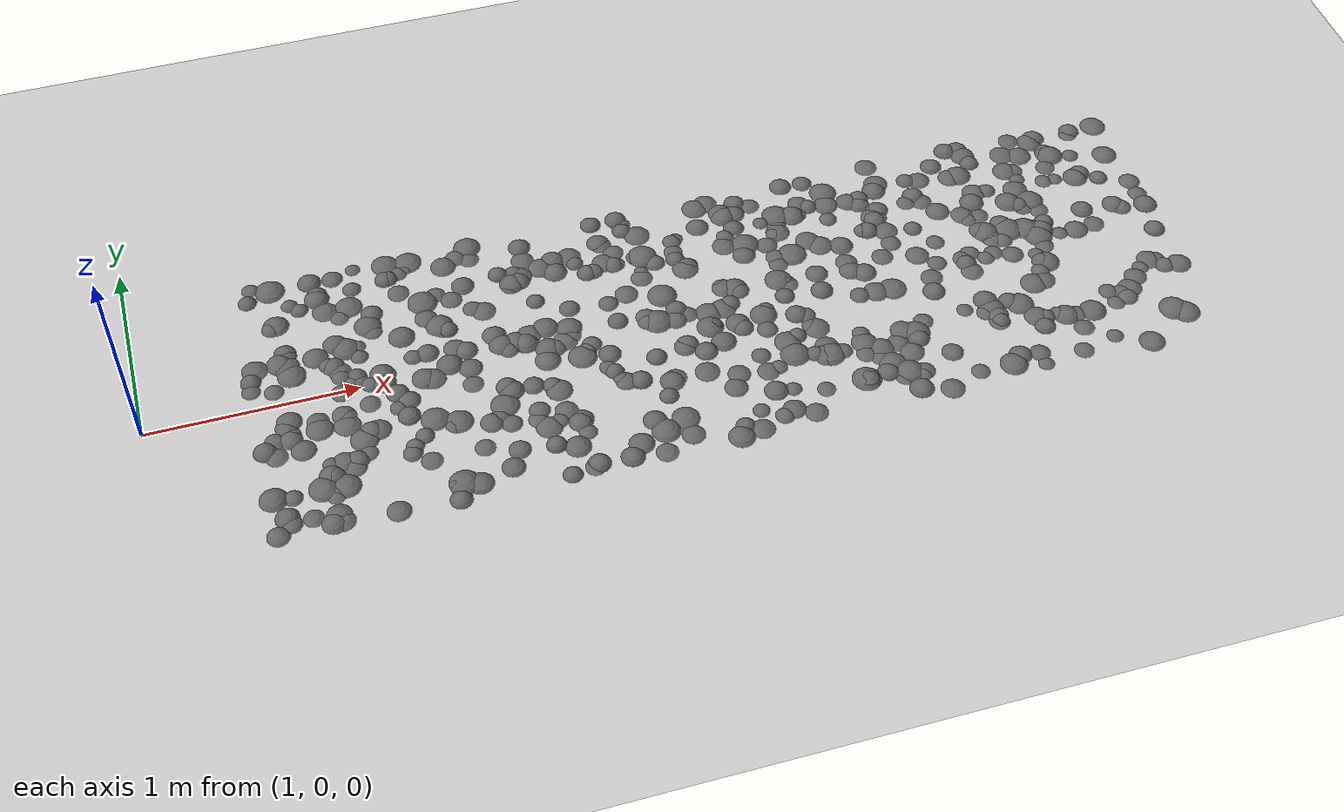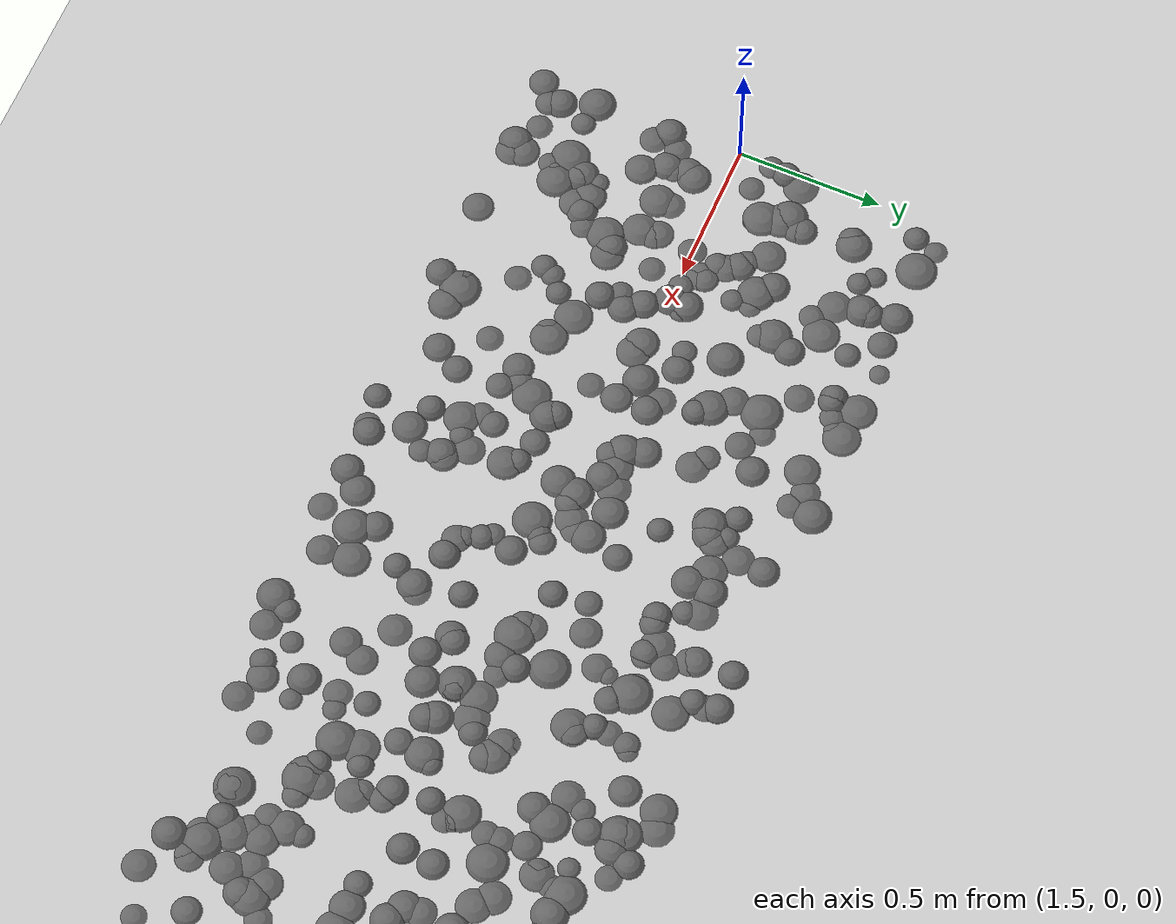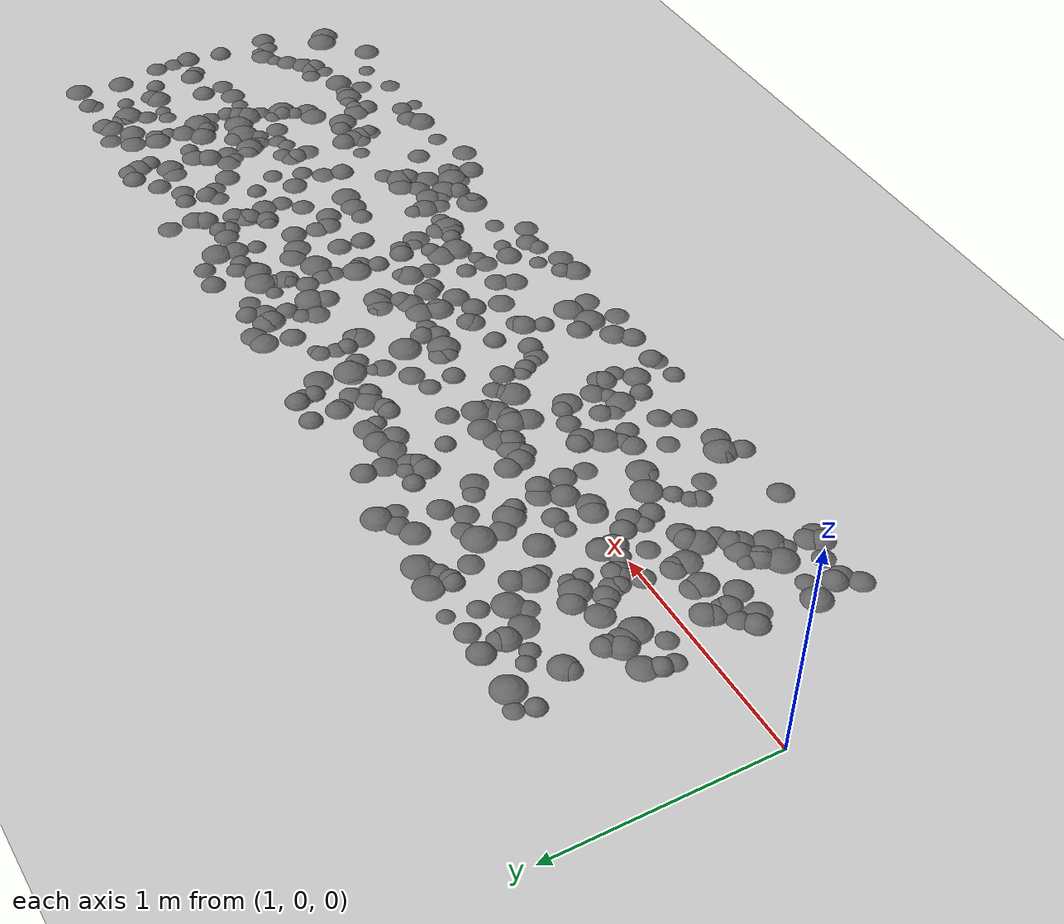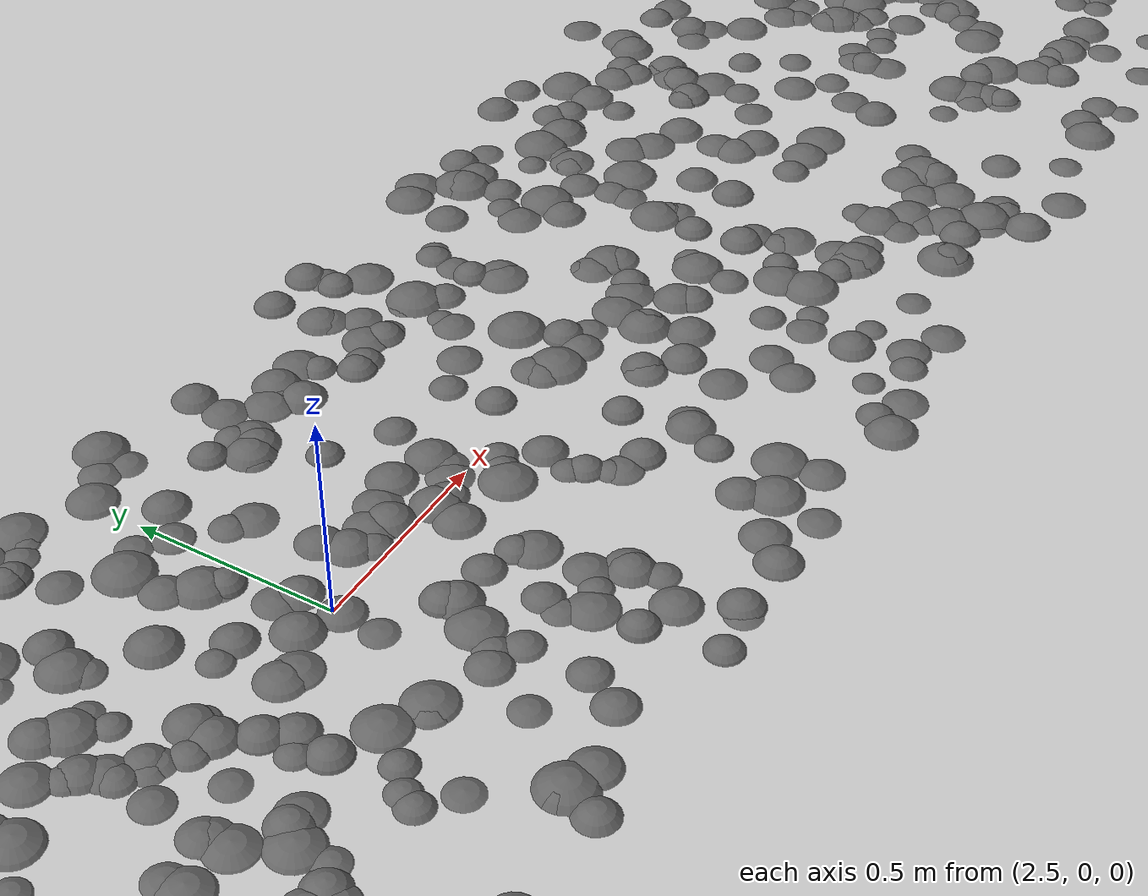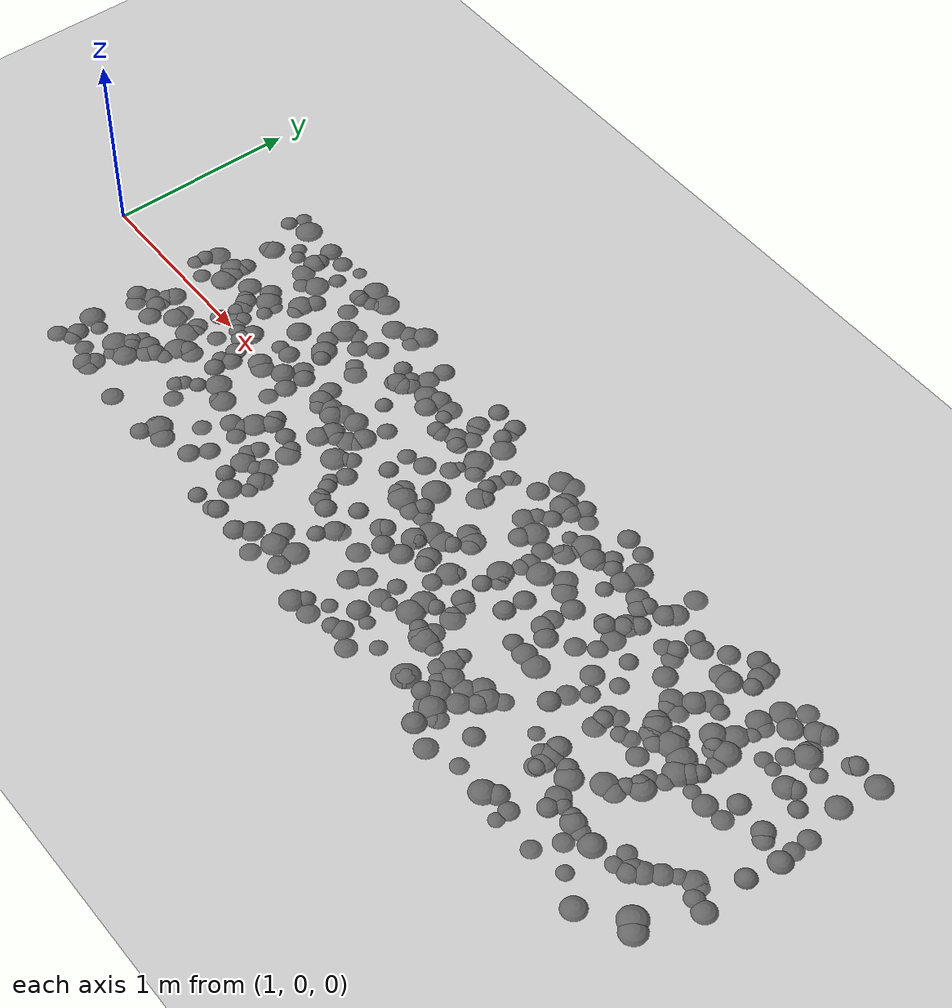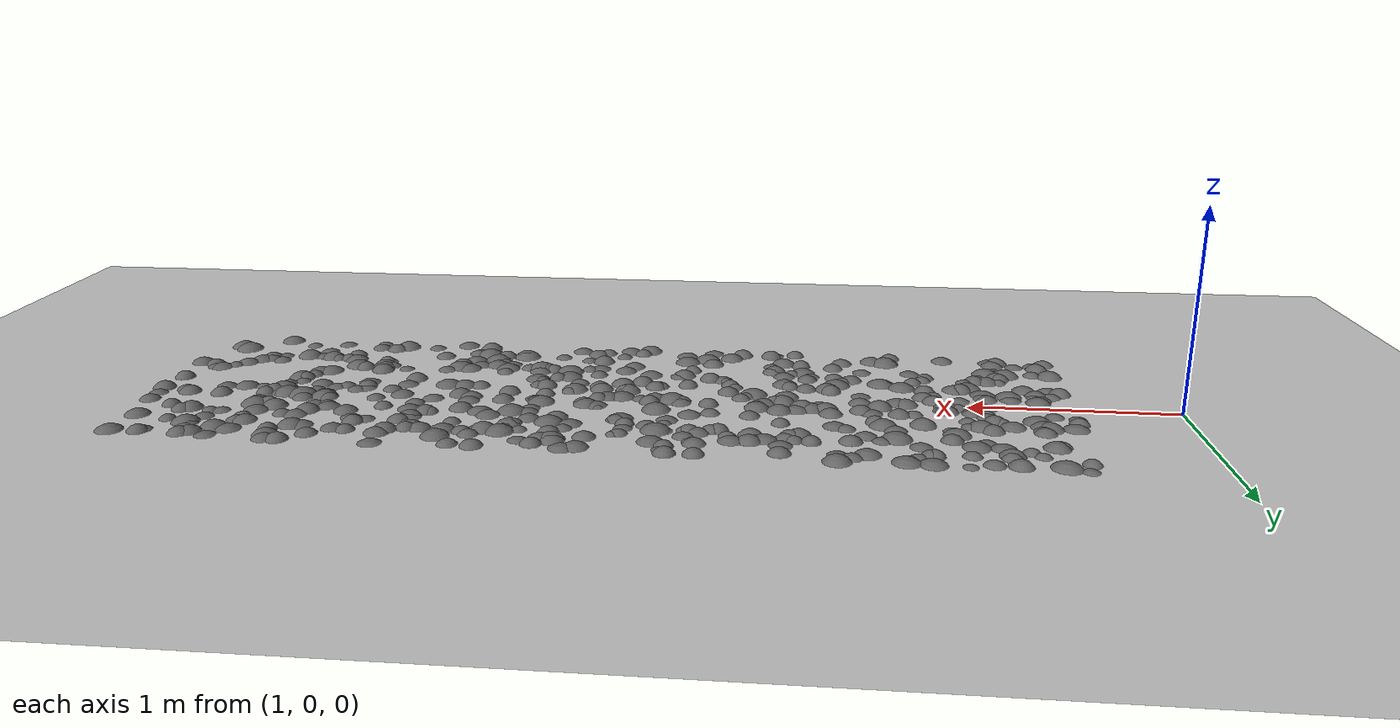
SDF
<?xml version="1.0" ?>
<sdf version="1.6">
  <world name="high_freq_world">
    <light type="directional" name="sun">
      <cast_shadows>true</cast_shadows>
      <pose>0 0 10 0 0 0</pose>
      <diffuse>0.8 0.8 0.8 1</diffuse>
      <specular>0.2 0.2 0.2 1</specular>
      <attenuation>
        <range>1000</range>
        <constant>0.9</constant>
        <linear>0.01</linear>
        <quadratic>0.001</quadratic>
      </attenuation>
      <direction>-0.5 0.1 -0.9</direction>
    </light>
    <model name="ground_plane">
      <static>true</static>
      <link name="link">
        <collision name="collision">
          <geometry>
            <plane>
              <normal>0 0 1</normal>
              <size>100 100</size>
            </plane>
          </geometry>
          <surface>
            <friction>
              <ode>
                <mu>100.0</mu>
                <mu2>100.0</mu2>
              </ode>
            </friction>
          </surface>
        </collision>
        <visual name="visual">
          <geometry>
            <plane>
              <normal>0 0 1</normal>
              <size>100 100</size>
            </plane>
          </geometry>
          <material>
            <ambient>0.8 0.8 0.8 1</ambient>
            <diffuse>0.8 0.8 0.8 1</diffuse>
          </material>
        </visual>
      </link>
    </model>

    <model name="bump_0">
      <static>true</static>
      <pose>3.684 -0.187 -0.048 0 0 0</pose>
      <link name="link">
        <collision name="collision">
          <geometry>
            <sphere><radius>0.074</radius></sphere>
          </geometry>
          <surface>
            <friction>
              <ode>
                <mu>100.0</mu>
                <mu2>100.0</mu2>
              </ode>
            </friction>
          </surface>
        </collision>
        <visual name="visual">
          <geometry>
            <sphere><radius>0.074</radius></sphere>
          </geometry>
          <material>
            <ambient>0.3 0.3 0.3 1</ambient> <diffuse>0.4 0.4 0.4 1</diffuse>
          </material>
        </visual>
      </link>
    </model>

    <model name="bump_1">
      <static>true</static>
      <pose>3.433 0.444 -0.080 0 0 0</pose>
      <link name="link">
        <collision name="collision">
          <geometry>
            <sphere><radius>0.091</radius></sphere>
          </geometry>
          <surface>
            <friction>
              <ode>
                <mu>100.0</mu>
                <mu2>100.0</mu2>
              </ode>
            </friction>
          </surface>
        </collision>
        <visual name="visual">
          <geometry>
            <sphere><radius>0.091</radius></sphere>
          </geometry>
          <material>
            <ambient>0.3 0.3 0.3 1</ambient> <diffuse>0.4 0.4 0.4 1</diffuse>
          </material>
        </visual>
      </link>
    </model>

    <model name="bump_2">
      <static>true</static>
      <pose>4.587 0.118 -0.067 0 0 0</pose>
      <link name="link">
        <collision name="collision">
          <geometry>
            <sphere><radius>0.082</radius></sphere>
          </geometry>
          <surface>
            <friction>
              <ode>
                <mu>100.0</mu>
                <mu2>100.0</mu2>
              </ode>
            </friction>
          </surface>
        </collision>
        <visual name="visual">
          <geometry>
            <sphere><radius>0.082</radius></sphere>
          </geometry>
          <material>
            <ambient>0.3 0.3 0.3 1</ambient> <diffuse>0.4 0.4 0.4 1</diffuse>
          </material>
        </visual>
      </link>
    </model>

    <model name="bump_3">
      <static>true</static>
      <pose>5.639 0.567 -0.061 0 0 0</pose>
      <link name="link">
        <collision name="collision">
          <geometry>
            <sphere><radius>0.078</radius></sphere>
          </geometry>
          <surface>
            <friction>
              <ode>
                <mu>100.0</mu>
                <mu2>100.0</mu2>
              </ode>
            </friction>
          </surface>
        </collision>
        <visual name="visual">
          <geometry>
            <sphere><radius>0.078</radius></sphere>
          </geometry>
          <material>
            <ambient>0.3 0.3 0.3 1</ambient> <diffuse>0.4 0.4 0.4 1</diffuse>
          </material>
        </visual>
      </link>
    </model>

    <model name="bump_4">
      <static>true</static>
      <pose>4.720 0.723 -0.085 0 0 0</pose>
      <link name="link">
        <collision name="collision">
          <geometry>
            <sphere><radius>0.098</radius></sphere>
          </geometry>
          <surface>
            <friction>
              <ode>
                <mu>100.0</mu>
                <mu2>100.0</mu2>
              </ode>
            </friction>
          </surface>
        </collision>
        <visual name="visual">
          <geometry>
            <sphere><radius>0.098</radius></sphere>
          </geometry>
          <material>
            <ambient>0.3 0.3 0.3 1</ambient> <diffuse>0.4 0.4 0.4 1</diffuse>
          </material>
        </visual>
      </link>
    </model>

    <model name="bump_5">
      <static>true</static>
      <pose>4.611 0.526 -0.031 0 0 0</pose>
      <link name="link">
        <collision name="collision">
          <geometry>
            <sphere><radius>0.056</radius></sphere>
          </geometry>
          <surface>
            <friction>
              <ode>
                <mu>100.0</mu>
                <mu2>100.0</mu2>
              </ode>
            </friction>
          </surface>
        </collision>
        <visual name="visual">
          <geometry>
            <sphere><radius>0.056</radius></sphere>
          </geometry>
          <material>
            <ambient>0.3 0.3 0.3 1</ambient> <diffuse>0.4 0.4 0.4 1</diffuse>
          </material>
        </visual>
      </link>
    </model>

    <model name="bump_6">
      <static>true</static>
      <pose>4.596 0.488 -0.052 0 0 0</pose>
      <link name="link">
        <collision name="collision">
          <geometry>
            <sphere><radius>0.072</radius></sphere>
          </geometry>
          <surface>
            <friction>
              <ode>
                <mu>100.0</mu>
                <mu2>100.0</mu2>
              </ode>
            </friction>
          </surface>
        </collision>
        <visual name="visual">
          <geometry>
            <sphere><radius>0.072</radius></sphere>
          </geometry>
          <material>
            <ambient>0.3 0.3 0.3 1</ambient> <diffuse>0.4 0.4 0.4 1</diffuse>
          </material>
        </visual>
      </link>
    </model>

    <model name="bump_7">
      <static>true</static>
      <pose>3.665 0.326 -0.052 0 0 0</pose>
      <link name="link">
        <collision name="collision">
          <geometry>
            <sphere><radius>0.065</radius></sphere>
          </geometry>
          <surface>
            <friction>
              <ode>
                <mu>100.0</mu>
                <mu2>100.0</mu2>
              </ode>
            </friction>
          </surface>
        </collision>
        <visual name="visual">
          <geometry>
            <sphere><radius>0.065</radius></sphere>
          </geometry>
          <material>
            <ambient>0.3 0.3 0.3 1</ambient> <diffuse>0.4 0.4 0.4 1</diffuse>
          </material>
        </visual>
      </link>
    </model>

    <model name="bump_8">
      <static>true</static>
      <pose>4.639 0.379 -0.080 0 0 0</pose>
      <link name="link">
        <collision name="collision">
          <geometry>
            <sphere><radius>0.100</radius></sphere>
          </geometry>
          <surface>
            <friction>
              <ode>
                <mu>100.0</mu>
                <mu2>100.0</mu2>
              </ode>
            </friction>
          </surface>
        </collision>
        <visual name="visual">
          <geometry>
            <sphere><radius>0.100</radius></sphere>
          </geometry>
          <material>
            <ambient>0.3 0.3 0.3 1</ambient> <diffuse>0.4 0.4 0.4 1</diffuse>
          </material>
        </visual>
      </link>
    </model>

    <model name="bump_9">
      <static>true</static>
      <pose>2.586 0.682 -0.064 0 0 0</pose>
      <link name="link">
        <collision name="collision">
          <geometry>
            <sphere><radius>0.079</radius></sphere>
          </geometry>
          <surface>
            <friction>
              <ode>
                <mu>100.0</mu>
                <mu2>100.0</mu2>
              </ode>
            </friction>
          </surface>
        </collision>
        <visual name="visual">
          <geometry>
            <sphere><radius>0.079</radius></sphere>
          </geometry>
          <material>
            <ambient>0.3 0.3 0.3 1</ambient> <diffuse>0.4 0.4 0.4 1</diffuse>
          </material>
        </visual>
      </link>
    </model>

    <model name="bump_10">
      <static>true</static>
      <pose>2.442 0.248 -0.077 0 0 0</pose>
      <link name="link">
        <collision name="collision">
          <geometry>
            <sphere><radius>0.090</radius></sphere>
          </geometry>
          <surface>
            <friction>
              <ode>
                <mu>100.0</mu>
                <mu2>100.0</mu2>
              </ode>
            </friction>
          </surface>
        </collision>
        <visual name="visual">
          <geometry>
            <sphere><radius>0.090</radius></sphere>
          </geometry>
          <material>
            <ambient>0.3 0.3 0.3 1</ambient> <diffuse>0.4 0.4 0.4 1</diffuse>
          </material>
        </visual>
      </link>
    </model>

    <model name="bump_11">
      <static>true</static>
      <pose>1.570 -0.199 -0.064 0 0 0</pose>
      <link name="link">
        <collision name="collision">
          <geometry>
            <sphere><radius>0.077</radius></sphere>
          </geometry>
          <surface>
            <friction>
              <ode>
                <mu>100.0</mu>
                <mu2>100.0</mu2>
              </ode>
            </friction>
          </surface>
        </collision>
        <visual name="visual">
          <geometry>
            <sphere><radius>0.077</radius></sphere>
          </geometry>
          <material>
            <ambient>0.3 0.3 0.3 1</ambient> <diffuse>0.4 0.4 0.4 1</diffuse>
          </material>
        </visual>
      </link>
    </model>

    <model name="bump_12">
      <static>true</static>
      <pose>4.964 -0.004 -0.087 0 0 0</pose>
      <link name="link">
        <collision name="collision">
          <geometry>
            <sphere><radius>0.099</radius></sphere>
          </geometry>
          <surface>
            <friction>
              <ode>
                <mu>100.0</mu>
                <mu2>100.0</mu2>
              </ode>
            </friction>
          </surface>
        </collision>
        <visual name="visual">
          <geometry>
            <sphere><radius>0.099</radius></sphere>
          </geometry>
          <material>
            <ambient>0.3 0.3 0.3 1</ambient> <diffuse>0.4 0.4 0.4 1</diffuse>
          </material>
        </visual>
      </link>
    </model>

    <model name="bump_13">
      <static>true</static>
      <pose>2.088 0.740 -0.044 0 0 0</pose>
      <link name="link">
        <collision name="collision">
          <geometry>
            <sphere><radius>0.054</radius></sphere>
          </geometry>
          <surface>
            <friction>
              <ode>
                <mu>100.0</mu>
                <mu2>100.0</mu2>
              </ode>
            </friction>
          </surface>
        </collision>
        <visual name="visual">
          <geometry>
            <sphere><radius>0.054</radius></sphere>
          </geometry>
          <material>
            <ambient>0.3 0.3 0.3 1</ambient> <diffuse>0.4 0.4 0.4 1</diffuse>
          </material>
        </visual>
      </link>
    </model>

    <model name="bump_14">
      <static>true</static>
      <pose>4.027 -0.248 -0.026 0 0 0</pose>
      <link name="link">
        <collision name="collision">
          <geometry>
            <sphere><radius>0.050</radius></sphere>
          </geometry>
          <surface>
            <friction>
              <ode>
                <mu>100.0</mu>
                <mu2>100.0</mu2>
              </ode>
            </friction>
          </surface>
        </collision>
        <visual name="visual">
          <geometry>
            <sphere><radius>0.050</radius></sphere>
          </geometry>
          <material>
            <ambient>0.3 0.3 0.3 1</ambient> <diffuse>0.4 0.4 0.4 1</diffuse>
          </material>
        </visual>
      </link>
    </model>

    <model name="bump_15">
      <static>true</static>
      <pose>4.084 0.092 -0.048 0 0 0</pose>
      <link name="link">
        <collision name="collision">
          <geometry>
            <sphere><radius>0.062</radius></sphere>
          </geometry>
          <surface>
            <friction>
              <ode>
                <mu>100.0</mu>
                <mu2>100.0</mu2>
              </ode>
            </friction>
          </surface>
        </collision>
        <visual name="visual">
          <geometry>
            <sphere><radius>0.062</radius></sphere>
          </geometry>
          <material>
            <ambient>0.3 0.3 0.3 1</ambient> <diffuse>0.4 0.4 0.4 1</diffuse>
          </material>
        </visual>
      </link>
    </model>

    <model name="bump_16">
      <static>true</static>
      <pose>3.419 0.019 -0.067 0 0 0</pose>
      <link name="link">
        <collision name="collision">
          <geometry>
            <sphere><radius>0.096</radius></sphere>
          </geometry>
          <surface>
            <friction>
              <ode>
                <mu>100.0</mu>
                <mu2>100.0</mu2>
              </ode>
            </friction>
          </surface>
        </collision>
        <visual name="visual">
          <geometry>
            <sphere><radius>0.096</radius></sphere>
          </geometry>
          <material>
            <ambient>0.3 0.3 0.3 1</ambient> <diffuse>0.4 0.4 0.4 1</diffuse>
          </material>
        </visual>
      </link>
    </model>

    <model name="bump_17">
      <static>true</static>
      <pose>2.576 -0.338 -0.054 0 0 0</pose>
      <link name="link">
        <collision name="collision">
          <geometry>
            <sphere><radius>0.068</radius></sphere>
          </geometry>
          <surface>
            <friction>
              <ode>
                <mu>100.0</mu>
                <mu2>100.0</mu2>
              </ode>
            </friction>
          </surface>
        </collision>
        <visual name="visual">
          <geometry>
            <sphere><radius>0.068</radius></sphere>
          </geometry>
          <material>
            <ambient>0.3 0.3 0.3 1</ambient> <diffuse>0.4 0.4 0.4 1</diffuse>
          </material>
        </visual>
      </link>
    </model>

    <model name="bump_18">
      <static>true</static>
      <pose>2.618 -0.543 -0.045 0 0 0</pose>
      <link name="link">
        <collision name="collision">
          <geometry>
            <sphere><radius>0.066</radius></sphere>
          </geometry>
          <surface>
            <friction>
              <ode>
                <mu>100.0</mu>
                <mu2>100.0</mu2>
              </ode>
            </friction>
          </surface>
        </collision>
        <visual name="visual">
          <geometry>
            <sphere><radius>0.066</radius></sphere>
          </geometry>
          <material>
            <ambient>0.3 0.3 0.3 1</ambient> <diffuse>0.4 0.4 0.4 1</diffuse>
          </material>
        </visual>
      </link>
    </model>

    <model name="bump_19">
      <static>true</static>
      <pose>2.418 0.028 -0.045 0 0 0</pose>
      <link name="link">
        <collision name="collision">
          <geometry>
            <sphere><radius>0.074</radius></sphere>
          </geometry>
          <surface>
            <friction>
              <ode>
                <mu>100.0</mu>
                <mu2>100.0</mu2>
              </ode>
            </friction>
          </surface>
        </collision>
        <visual name="visual">
          <geometry>
            <sphere><radius>0.074</radius></sphere>
          </geometry>
          <material>
            <ambient>0.3 0.3 0.3 1</ambient> <diffuse>0.4 0.4 0.4 1</diffuse>
          </material>
        </visual>
      </link>
    </model>

    <model name="bump_20">
      <static>true</static>
      <pose>5.345 -0.571 -0.075 0 0 0</pose>
      <link name="link">
        <collision name="collision">
          <geometry>
            <sphere><radius>0.086</radius></sphere>
          </geometry>
          <surface>
            <friction>
              <ode>
                <mu>100.0</mu>
                <mu2>100.0</mu2>
              </ode>
            </friction>
          </surface>
        </collision>
        <visual name="visual">
          <geometry>
            <sphere><radius>0.086</radius></sphere>
          </geometry>
          <material>
            <ambient>0.3 0.3 0.3 1</ambient> <diffuse>0.4 0.4 0.4 1</diffuse>
          </material>
        </visual>
      </link>
    </model>

    <model name="bump_21">
      <static>true</static>
      <pose>5.287 -0.701 -0.077 0 0 0</pose>
      <link name="link">
        <collision name="collision">
          <geometry>
            <sphere><radius>0.087</radius></sphere>
          </geometry>
          <surface>
            <friction>
              <ode>
                <mu>100.0</mu>
                <mu2>100.0</mu2>
              </ode>
            </friction>
          </surface>
        </collision>
        <visual name="visual">
          <geometry>
            <sphere><radius>0.087</radius></sphere>
          </geometry>
          <material>
            <ambient>0.3 0.3 0.3 1</ambient> <diffuse>0.4 0.4 0.4 1</diffuse>
          </material>
        </visual>
      </link>
    </model>

    <model name="bump_22">
      <static>true</static>
      <pose>3.116 0.536 -0.079 0 0 0</pose>
      <link name="link">
        <collision name="collision">
          <geometry>
            <sphere><radius>0.096</radius></sphere>
          </geometry>
          <surface>
            <friction>
              <ode>
                <mu>100.0</mu>
                <mu2>100.0</mu2>
              </ode>
            </friction>
          </surface>
        </collision>
        <visual name="visual">
          <geometry>
            <sphere><radius>0.096</radius></sphere>
          </geometry>
          <material>
            <ambient>0.3 0.3 0.3 1</ambient> <diffuse>0.4 0.4 0.4 1</diffuse>
          </material>
        </visual>
      </link>
    </model>

    <model name="bump_23">
      <static>true</static>
      <pose>1.988 0.076 -0.051 0 0 0</pose>
      <link name="link">
        <collision name="collision">
          <geometry>
            <sphere><radius>0.068</radius></sphere>
          </geometry>
          <surface>
            <friction>
              <ode>
                <mu>100.0</mu>
                <mu2>100.0</mu2>
              </ode>
            </friction>
          </surface>
        </collision>
        <visual name="visual">
          <geometry>
            <sphere><radius>0.068</radius></sphere>
          </geometry>
          <material>
            <ambient>0.3 0.3 0.3 1</ambient> <diffuse>0.4 0.4 0.4 1</diffuse>
          </material>
        </visual>
      </link>
    </model>

    <model name="bump_24">
      <static>true</static>
      <pose>1.793 -0.394 -0.038 0 0 0</pose>
      <link name="link">
        <collision name="collision">
          <geometry>
            <sphere><radius>0.052</radius></sphere>
          </geometry>
          <surface>
            <friction>
              <ode>
                <mu>100.0</mu>
                <mu2>100.0</mu2>
              </ode>
            </friction>
          </surface>
        </collision>
        <visual name="visual">
          <geometry>
            <sphere><radius>0.052</radius></sphere>
          </geometry>
          <material>
            <ambient>0.3 0.3 0.3 1</ambient> <diffuse>0.4 0.4 0.4 1</diffuse>
          </material>
        </visual>
      </link>
    </model>

    <model name="bump_25">
      <static>true</static>
      <pose>1.893 -0.132 -0.065 0 0 0</pose>
      <link name="link">
        <collision name="collision">
          <geometry>
            <sphere><radius>0.082</radius></sphere>
          </geometry>
          <surface>
            <friction>
              <ode>
                <mu>100.0</mu>
                <mu2>100.0</mu2>
              </ode>
            </friction>
          </surface>
        </collision>
        <visual name="visual">
          <geometry>
            <sphere><radius>0.082</radius></sphere>
          </geometry>
          <material>
            <ambient>0.3 0.3 0.3 1</ambient> <diffuse>0.4 0.4 0.4 1</diffuse>
          </material>
        </visual>
      </link>
    </model>

    <model name="bump_26">
      <static>true</static>
      <pose>1.692 0.304 -0.043 0 0 0</pose>
      <link name="link">
        <collision name="collision">
          <geometry>
            <sphere><radius>0.065</radius></sphere>
          </geometry>
          <surface>
            <friction>
              <ode>
                <mu>100.0</mu>
                <mu2>100.0</mu2>
              </ode>
            </friction>
          </surface>
        </collision>
        <visual name="visual">
          <geometry>
            <sphere><radius>0.065</radius></sphere>
          </geometry>
          <material>
            <ambient>0.3 0.3 0.3 1</ambient> <diffuse>0.4 0.4 0.4 1</diffuse>
          </material>
        </visual>
      </link>
    </model>

    <model name="bump_27">
      <static>true</static>
      <pose>2.642 0.308 -0.078 0 0 0</pose>
      <link name="link">
        <collision name="collision">
          <geometry>
            <sphere><radius>0.094</radius></sphere>
          </geometry>
          <surface>
            <friction>
              <ode>
                <mu>100.0</mu>
                <mu2>100.0</mu2>
              </ode>
            </friction>
          </surface>
        </collision>
        <visual name="visual">
          <geometry>
            <sphere><radius>0.094</radius></sphere>
          </geometry>
          <material>
            <ambient>0.3 0.3 0.3 1</ambient> <diffuse>0.4 0.4 0.4 1</diffuse>
          </material>
        </visual>
      </link>
    </model>

    <model name="bump_28">
      <static>true</static>
      <pose>3.248 -0.306 -0.030 0 0 0</pose>
      <link name="link">
        <collision name="collision">
          <geometry>
            <sphere><radius>0.060</radius></sphere>
          </geometry>
          <surface>
            <friction>
              <ode>
                <mu>100.0</mu>
                <mu2>100.0</mu2>
              </ode>
            </friction>
          </surface>
        </collision>
        <visual name="visual">
          <geometry>
            <sphere><radius>0.060</radius></sphere>
          </geometry>
          <material>
            <ambient>0.3 0.3 0.3 1</ambient> <diffuse>0.4 0.4 0.4 1</diffuse>
          </material>
        </visual>
      </link>
    </model>

    <model name="bump_29">
      <static>true</static>
      <pose>4.982 -0.423 -0.026 0 0 0</pose>
      <link name="link">
        <collision name="collision">
          <geometry>
            <sphere><radius>0.051</radius></sphere>
          </geometry>
          <surface>
            <friction>
              <ode>
                <mu>100.0</mu>
                <mu2>100.0</mu2>
              </ode>
            </friction>
          </surface>
        </collision>
        <visual name="visual">
          <geometry>
            <sphere><radius>0.051</radius></sphere>
          </geometry>
          <material>
            <ambient>0.3 0.3 0.3 1</ambient> <diffuse>0.4 0.4 0.4 1</diffuse>
          </material>
        </visual>
      </link>
    </model>

    <model name="bump_30">
      <static>true</static>
      <pose>4.972 -0.091 -0.081 0 0 0</pose>
      <link name="link">
        <collision name="collision">
          <geometry>
            <sphere><radius>0.094</radius></sphere>
          </geometry>
          <surface>
            <friction>
              <ode>
                <mu>100.0</mu>
                <mu2>100.0</mu2>
              </ode>
            </friction>
          </surface>
        </collision>
        <visual name="visual">
          <geometry>
            <sphere><radius>0.094</radius></sphere>
          </geometry>
          <material>
            <ambient>0.3 0.3 0.3 1</ambient> <diffuse>0.4 0.4 0.4 1</diffuse>
          </material>
        </visual>
      </link>
    </model>

    <model name="bump_31">
      <static>true</static>
      <pose>4.906 0.418 -0.081 0 0 0</pose>
      <link name="link">
        <collision name="collision">
          <geometry>
            <sphere><radius>0.092</radius></sphere>
          </geometry>
          <surface>
            <friction>
              <ode>
                <mu>100.0</mu>
                <mu2>100.0</mu2>
              </ode>
            </friction>
          </surface>
        </collision>
        <visual name="visual">
          <geometry>
            <sphere><radius>0.092</radius></sphere>
          </geometry>
          <material>
            <ambient>0.3 0.3 0.3 1</ambient> <diffuse>0.4 0.4 0.4 1</diffuse>
          </material>
        </visual>
      </link>
    </model>

    <model name="bump_32">
      <static>true</static>
      <pose>5.493 0.702 -0.084 0 0 0</pose>
      <link name="link">
        <collision name="collision">
          <geometry>
            <sphere><radius>0.095</radius></sphere>
          </geometry>
          <surface>
            <friction>
              <ode>
                <mu>100.0</mu>
                <mu2>100.0</mu2>
              </ode>
            </friction>
          </surface>
        </collision>
        <visual name="visual">
          <geometry>
            <sphere><radius>0.095</radius></sphere>
          </geometry>
          <material>
            <ambient>0.3 0.3 0.3 1</ambient> <diffuse>0.4 0.4 0.4 1</diffuse>
          </material>
        </visual>
      </link>
    </model>

    <model name="bump_33">
      <static>true</static>
      <pose>4.525 -0.613 -0.062 0 0 0</pose>
      <link name="link">
        <collision name="collision">
          <geometry>
            <sphere><radius>0.077</radius></sphere>
          </geometry>
          <surface>
            <friction>
              <ode>
                <mu>100.0</mu>
                <mu2>100.0</mu2>
              </ode>
            </friction>
          </surface>
        </collision>
        <visual name="visual">
          <geometry>
            <sphere><radius>0.077</radius></sphere>
          </geometry>
          <material>
            <ambient>0.3 0.3 0.3 1</ambient> <diffuse>0.4 0.4 0.4 1</diffuse>
          </material>
        </visual>
      </link>
    </model>

    <model name="bump_34">
      <static>true</static>
      <pose>1.900 -0.195 -0.079 0 0 0</pose>
      <link name="link">
        <collision name="collision">
          <geometry>
            <sphere><radius>0.098</radius></sphere>
          </geometry>
          <surface>
            <friction>
              <ode>
                <mu>100.0</mu>
                <mu2>100.0</mu2>
              </ode>
            </friction>
          </surface>
        </collision>
        <visual name="visual">
          <geometry>
            <sphere><radius>0.098</radius></sphere>
          </geometry>
          <material>
            <ambient>0.3 0.3 0.3 1</ambient> <diffuse>0.4 0.4 0.4 1</diffuse>
          </material>
        </visual>
      </link>
    </model>

    <model name="bump_35">
      <static>true</static>
      <pose>5.151 0.085 -0.081 0 0 0</pose>
      <link name="link">
        <collision name="collision">
          <geometry>
            <sphere><radius>0.094</radius></sphere>
          </geometry>
          <surface>
            <friction>
              <ode>
                <mu>100.0</mu>
                <mu2>100.0</mu2>
              </ode>
            </friction>
          </surface>
        </collision>
        <visual name="visual">
          <geometry>
            <sphere><radius>0.094</radius></sphere>
          </geometry>
          <material>
            <ambient>0.3 0.3 0.3 1</ambient> <diffuse>0.4 0.4 0.4 1</diffuse>
          </material>
        </visual>
      </link>
    </model>

    <model name="bump_36">
      <static>true</static>
      <pose>3.615 0.429 -0.061 0 0 0</pose>
      <link name="link">
        <collision name="collision">
          <geometry>
            <sphere><radius>0.073</radius></sphere>
          </geometry>
          <surface>
            <friction>
              <ode>
                <mu>100.0</mu>
                <mu2>100.0</mu2>
              </ode>
            </friction>
          </surface>
        </collision>
        <visual name="visual">
          <geometry>
            <sphere><radius>0.073</radius></sphere>
          </geometry>
          <material>
            <ambient>0.3 0.3 0.3 1</ambient> <diffuse>0.4 0.4 0.4 1</diffuse>
          </material>
        </visual>
      </link>
    </model>

    <model name="bump_37">
      <static>true</static>
      <pose>3.094 -0.721 -0.038 0 0 0</pose>
      <link name="link">
        <collision name="collision">
          <geometry>
            <sphere><radius>0.066</radius></sphere>
          </geometry>
          <surface>
            <friction>
              <ode>
                <mu>100.0</mu>
                <mu2>100.0</mu2>
              </ode>
            </friction>
          </surface>
        </collision>
        <visual name="visual">
          <geometry>
            <sphere><radius>0.066</radius></sphere>
          </geometry>
          <material>
            <ambient>0.3 0.3 0.3 1</ambient> <diffuse>0.4 0.4 0.4 1</diffuse>
          </material>
        </visual>
      </link>
    </model>

    <model name="bump_38">
      <static>true</static>
      <pose>4.830 0.432 -0.063 0 0 0</pose>
      <link name="link">
        <collision name="collision">
          <geometry>
            <sphere><radius>0.075</radius></sphere>
          </geometry>
          <surface>
            <friction>
              <ode>
                <mu>100.0</mu>
                <mu2>100.0</mu2>
              </ode>
            </friction>
          </surface>
        </collision>
        <visual name="visual">
          <geometry>
            <sphere><radius>0.075</radius></sphere>
          </geometry>
          <material>
            <ambient>0.3 0.3 0.3 1</ambient> <diffuse>0.4 0.4 0.4 1</diffuse>
          </material>
        </visual>
      </link>
    </model>

    <model name="bump_39">
      <static>true</static>
      <pose>2.816 0.104 -0.077 0 0 0</pose>
      <link name="link">
        <collision name="collision">
          <geometry>
            <sphere><radius>0.094</radius></sphere>
          </geometry>
          <surface>
            <friction>
              <ode>
                <mu>100.0</mu>
                <mu2>100.0</mu2>
              </ode>
            </friction>
          </surface>
        </collision>
        <visual name="visual">
          <geometry>
            <sphere><radius>0.094</radius></sphere>
          </geometry>
          <material>
            <ambient>0.3 0.3 0.3 1</ambient> <diffuse>0.4 0.4 0.4 1</diffuse>
          </material>
        </visual>
      </link>
    </model>

    <model name="bump_40">
      <static>true</static>
      <pose>3.781 0.136 -0.082 0 0 0</pose>
      <link name="link">
        <collision name="collision">
          <geometry>
            <sphere><radius>0.096</radius></sphere>
          </geometry>
          <surface>
            <friction>
              <ode>
                <mu>100.0</mu>
                <mu2>100.0</mu2>
              </ode>
            </friction>
          </surface>
        </collision>
        <visual name="visual">
          <geometry>
            <sphere><radius>0.096</radius></sphere>
          </geometry>
          <material>
            <ambient>0.3 0.3 0.3 1</ambient> <diffuse>0.4 0.4 0.4 1</diffuse>
          </material>
        </visual>
      </link>
    </model>

    <model name="bump_41">
      <static>true</static>
      <pose>2.369 0.337 -0.066 0 0 0</pose>
      <link name="link">
        <collision name="collision">
          <geometry>
            <sphere><radius>0.083</radius></sphere>
          </geometry>
          <surface>
            <friction>
              <ode>
                <mu>100.0</mu>
                <mu2>100.0</mu2>
              </ode>
            </friction>
          </surface>
        </collision>
        <visual name="visual">
          <geometry>
            <sphere><radius>0.083</radius></sphere>
          </geometry>
          <material>
            <ambient>0.3 0.3 0.3 1</ambient> <diffuse>0.4 0.4 0.4 1</diffuse>
          </material>
        </visual>
      </link>
    </model>

    <model name="bump_42">
      <static>true</static>
      <pose>2.063 0.617 -0.036 0 0 0</pose>
      <link name="link">
        <collision name="collision">
          <geometry>
            <sphere><radius>0.055</radius></sphere>
          </geometry>
          <surface>
            <friction>
              <ode>
                <mu>100.0</mu>
                <mu2>100.0</mu2>
              </ode>
            </friction>
          </surface>
        </collision>
        <visual name="visual">
          <geometry>
            <sphere><radius>0.055</radius></sphere>
          </geometry>
          <material>
            <ambient>0.3 0.3 0.3 1</ambient> <diffuse>0.4 0.4 0.4 1</diffuse>
          </material>
        </visual>
      </link>
    </model>

    <model name="bump_43">
      <static>true</static>
      <pose>4.318 -0.318 -0.040 0 0 0</pose>
      <link name="link">
        <collision name="collision">
          <geometry>
            <sphere><radius>0.056</radius></sphere>
          </geometry>
          <surface>
            <friction>
              <ode>
                <mu>100.0</mu>
                <mu2>100.0</mu2>
              </ode>
            </friction>
          </surface>
        </collision>
        <visual name="visual">
          <geometry>
            <sphere><radius>0.056</radius></sphere>
          </geometry>
          <material>
            <ambient>0.3 0.3 0.3 1</ambient> <diffuse>0.4 0.4 0.4 1</diffuse>
          </material>
        </visual>
      </link>
    </model>

    <model name="bump_44">
      <static>true</static>
      <pose>1.999 -0.258 -0.035 0 0 0</pose>
      <link name="link">
        <collision name="collision">
          <geometry>
            <sphere><radius>0.064</radius></sphere>
          </geometry>
          <surface>
            <friction>
              <ode>
                <mu>100.0</mu>
                <mu2>100.0</mu2>
              </ode>
            </friction>
          </surface>
        </collision>
        <visual name="visual">
          <geometry>
            <sphere><radius>0.064</radius></sphere>
          </geometry>
          <material>
            <ambient>0.3 0.3 0.3 1</ambient> <diffuse>0.4 0.4 0.4 1</diffuse>
          </material>
        </visual>
      </link>
    </model>

    <model name="bump_45">
      <static>true</static>
      <pose>2.967 0.505 -0.076 0 0 0</pose>
      <link name="link">
        <collision name="collision">
          <geometry>
            <sphere><radius>0.095</radius></sphere>
          </geometry>
          <surface>
            <friction>
              <ode>
                <mu>100.0</mu>
                <mu2>100.0</mu2>
              </ode>
            </friction>
          </surface>
        </collision>
        <visual name="visual">
          <geometry>
            <sphere><radius>0.095</radius></sphere>
          </geometry>
          <material>
            <ambient>0.3 0.3 0.3 1</ambient> <diffuse>0.4 0.4 0.4 1</diffuse>
          </material>
        </visual>
      </link>
    </model>

    <model name="bump_46">
      <static>true</static>
      <pose>4.871 0.138 -0.050 0 0 0</pose>
      <link name="link">
        <collision name="collision">
          <geometry>
            <sphere><radius>0.065</radius></sphere>
          </geometry>
          <surface>
            <friction>
              <ode>
                <mu>100.0</mu>
                <mu2>100.0</mu2>
              </ode>
            </friction>
          </surface>
        </collision>
        <visual name="visual">
          <geometry>
            <sphere><radius>0.065</radius></sphere>
          </geometry>
          <material>
            <ambient>0.3 0.3 0.3 1</ambient> <diffuse>0.4 0.4 0.4 1</diffuse>
          </material>
        </visual>
      </link>
    </model>

    <model name="bump_47">
      <static>true</static>
      <pose>1.852 -0.400 -0.061 0 0 0</pose>
      <link name="link">
        <collision name="collision">
          <geometry>
            <sphere><radius>0.083</radius></sphere>
          </geometry>
          <surface>
            <friction>
              <ode>
                <mu>100.0</mu>
                <mu2>100.0</mu2>
              </ode>
            </friction>
          </surface>
        </collision>
        <visual name="visual">
          <geometry>
            <sphere><radius>0.083</radius></sphere>
          </geometry>
          <material>
            <ambient>0.3 0.3 0.3 1</ambient> <diffuse>0.4 0.4 0.4 1</diffuse>
          </material>
        </visual>
      </link>
    </model>

    <model name="bump_48">
      <static>true</static>
      <pose>3.526 0.065 -0.029 0 0 0</pose>
      <link name="link">
        <collision name="collision">
          <geometry>
            <sphere><radius>0.058</radius></sphere>
          </geometry>
          <surface>
            <friction>
              <ode>
                <mu>100.0</mu>
                <mu2>100.0</mu2>
              </ode>
            </friction>
          </surface>
        </collision>
        <visual name="visual">
          <geometry>
            <sphere><radius>0.058</radius></sphere>
          </geometry>
          <material>
            <ambient>0.3 0.3 0.3 1</ambient> <diffuse>0.4 0.4 0.4 1</diffuse>
          </material>
        </visual>
      </link>
    </model>

    <model name="bump_49">
      <static>true</static>
      <pose>5.717 -0.340 -0.063 0 0 0</pose>
      <link name="link">
        <collision name="collision">
          <geometry>
            <sphere><radius>0.081</radius></sphere>
          </geometry>
          <surface>
            <friction>
              <ode>
                <mu>100.0</mu>
                <mu2>100.0</mu2>
              </ode>
            </friction>
          </surface>
        </collision>
        <visual name="visual">
          <geometry>
            <sphere><radius>0.081</radius></sphere>
          </geometry>
          <material>
            <ambient>0.3 0.3 0.3 1</ambient> <diffuse>0.4 0.4 0.4 1</diffuse>
          </material>
        </visual>
      </link>
    </model>

    <model name="bump_50">
      <static>true</static>
      <pose>2.024 0.190 -0.038 0 0 0</pose>
      <link name="link">
        <collision name="collision">
          <geometry>
            <sphere><radius>0.054</radius></sphere>
          </geometry>
          <surface>
            <friction>
              <ode>
                <mu>100.0</mu>
                <mu2>100.0</mu2>
              </ode>
            </friction>
          </surface>
        </collision>
        <visual name="visual">
          <geometry>
            <sphere><radius>0.054</radius></sphere>
          </geometry>
          <material>
            <ambient>0.3 0.3 0.3 1</ambient> <diffuse>0.4 0.4 0.4 1</diffuse>
          </material>
        </visual>
      </link>
    </model>

    <model name="bump_51">
      <static>true</static>
      <pose>4.510 -0.489 -0.069 0 0 0</pose>
      <link name="link">
        <collision name="collision">
          <geometry>
            <sphere><radius>0.088</radius></sphere>
          </geometry>
          <surface>
            <friction>
              <ode>
                <mu>100.0</mu>
                <mu2>100.0</mu2>
              </ode>
            </friction>
          </surface>
        </collision>
        <visual name="visual">
          <geometry>
            <sphere><radius>0.088</radius></sphere>
          </geometry>
          <material>
            <ambient>0.3 0.3 0.3 1</ambient> <diffuse>0.4 0.4 0.4 1</diffuse>
          </material>
        </visual>
      </link>
    </model>

    <model name="bump_52">
      <static>true</static>
      <pose>4.798 0.255 -0.031 0 0 0</pose>
      <link name="link">
        <collision name="collision">
          <geometry>
            <sphere><radius>0.053</radius></sphere>
          </geometry>
          <surface>
            <friction>
              <ode>
                <mu>100.0</mu>
                <mu2>100.0</mu2>
              </ode>
            </friction>
          </surface>
        </collision>
        <visual name="visual">
          <geometry>
            <sphere><radius>0.053</radius></sphere>
          </geometry>
          <material>
            <ambient>0.3 0.3 0.3 1</ambient> <diffuse>0.4 0.4 0.4 1</diffuse>
          </material>
        </visual>
      </link>
    </model>

    <model name="bump_53">
      <static>true</static>
      <pose>3.889 0.459 -0.047 0 0 0</pose>
      <link name="link">
        <collision name="collision">
          <geometry>
            <sphere><radius>0.061</radius></sphere>
          </geometry>
          <surface>
            <friction>
              <ode>
                <mu>100.0</mu>
                <mu2>100.0</mu2>
              </ode>
            </friction>
          </surface>
        </collision>
        <visual name="visual">
          <geometry>
            <sphere><radius>0.061</radius></sphere>
          </geometry>
          <material>
            <ambient>0.3 0.3 0.3 1</ambient> <diffuse>0.4 0.4 0.4 1</diffuse>
          </material>
        </visual>
      </link>
    </model>

    <model name="bump_54">
      <static>true</static>
      <pose>1.671 -0.662 -0.070 0 0 0</pose>
      <link name="link">
        <collision name="collision">
          <geometry>
            <sphere><radius>0.081</radius></sphere>
          </geometry>
          <surface>
            <friction>
              <ode>
                <mu>100.0</mu>
                <mu2>100.0</mu2>
              </ode>
            </friction>
          </surface>
        </collision>
        <visual name="visual">
          <geometry>
            <sphere><radius>0.081</radius></sphere>
          </geometry>
          <material>
            <ambient>0.3 0.3 0.3 1</ambient> <diffuse>0.4 0.4 0.4 1</diffuse>
          </material>
        </visual>
      </link>
    </model>

    <model name="bump_55">
      <static>true</static>
      <pose>1.640 -0.208 -0.049 0 0 0</pose>
      <link name="link">
        <collision name="collision">
          <geometry>
            <sphere><radius>0.071</radius></sphere>
          </geometry>
          <surface>
            <friction>
              <ode>
                <mu>100.0</mu>
                <mu2>100.0</mu2>
              </ode>
            </friction>
          </surface>
        </collision>
        <visual name="visual">
          <geometry>
            <sphere><radius>0.071</radius></sphere>
          </geometry>
          <material>
            <ambient>0.3 0.3 0.3 1</ambient> <diffuse>0.4 0.4 0.4 1</diffuse>
          </material>
        </visual>
      </link>
    </model>

    <model name="bump_56">
      <static>true</static>
      <pose>2.783 -0.562 -0.023 0 0 0</pose>
      <link name="link">
        <collision name="collision">
          <geometry>
            <sphere><radius>0.052</radius></sphere>
          </geometry>
          <surface>
            <friction>
              <ode>
                <mu>100.0</mu>
                <mu2>100.0</mu2>
              </ode>
            </friction>
          </surface>
        </collision>
        <visual name="visual">
          <geometry>
            <sphere><radius>0.052</radius></sphere>
          </geometry>
          <material>
            <ambient>0.3 0.3 0.3 1</ambient> <diffuse>0.4 0.4 0.4 1</diffuse>
          </material>
        </visual>
      </link>
    </model>

    <model name="bump_57">
      <static>true</static>
      <pose>3.038 0.211 -0.041 0 0 0</pose>
      <link name="link">
        <collision name="collision">
          <geometry>
            <sphere><radius>0.062</radius></sphere>
          </geometry>
          <surface>
            <friction>
              <ode>
                <mu>100.0</mu>
                <mu2>100.0</mu2>
              </ode>
            </friction>
          </surface>
        </collision>
        <visual name="visual">
          <geometry>
            <sphere><radius>0.062</radius></sphere>
          </geometry>
          <material>
            <ambient>0.3 0.3 0.3 1</ambient> <diffuse>0.4 0.4 0.4 1</diffuse>
          </material>
        </visual>
      </link>
    </model>

    <model name="bump_58">
      <static>true</static>
      <pose>1.903 -0.146 -0.061 0 0 0</pose>
      <link name="link">
        <collision name="collision">
          <geometry>
            <sphere><radius>0.077</radius></sphere>
          </geometry>
          <surface>
            <friction>
              <ode>
                <mu>100.0</mu>
                <mu2>100.0</mu2>
              </ode>
            </friction>
          </surface>
        </collision>
        <visual name="visual">
          <geometry>
            <sphere><radius>0.077</radius></sphere>
          </geometry>
          <material>
            <ambient>0.3 0.3 0.3 1</ambient> <diffuse>0.4 0.4 0.4 1</diffuse>
          </material>
        </visual>
      </link>
    </model>

    <model name="bump_59">
      <static>true</static>
      <pose>1.683 0.223 -0.075 0 0 0</pose>
      <link name="link">
        <collision name="collision">
          <geometry>
            <sphere><radius>0.097</radius></sphere>
          </geometry>
          <surface>
            <friction>
              <ode>
                <mu>100.0</mu>
                <mu2>100.0</mu2>
              </ode>
            </friction>
          </surface>
        </collision>
        <visual name="visual">
          <geometry>
            <sphere><radius>0.097</radius></sphere>
          </geometry>
          <material>
            <ambient>0.3 0.3 0.3 1</ambient> <diffuse>0.4 0.4 0.4 1</diffuse>
          </material>
        </visual>
      </link>
    </model>

    <model name="bump_60">
      <static>true</static>
      <pose>2.126 0.436 -0.037 0 0 0</pose>
      <link name="link">
        <collision name="collision">
          <geometry>
            <sphere><radius>0.063</radius></sphere>
          </geometry>
          <surface>
            <friction>
              <ode>
                <mu>100.0</mu>
                <mu2>100.0</mu2>
              </ode>
            </friction>
          </surface>
        </collision>
        <visual name="visual">
          <geometry>
            <sphere><radius>0.063</radius></sphere>
          </geometry>
          <material>
            <ambient>0.3 0.3 0.3 1</ambient> <diffuse>0.4 0.4 0.4 1</diffuse>
          </material>
        </visual>
      </link>
    </model>

    <model name="bump_61">
      <static>true</static>
      <pose>3.629 0.498 -0.044 0 0 0</pose>
      <link name="link">
        <collision name="collision">
          <geometry>
            <sphere><radius>0.061</radius></sphere>
          </geometry>
          <surface>
            <friction>
              <ode>
                <mu>100.0</mu>
                <mu2>100.0</mu2>
              </ode>
            </friction>
          </surface>
        </collision>
        <visual name="visual">
          <geometry>
            <sphere><radius>0.061</radius></sphere>
          </geometry>
          <material>
            <ambient>0.3 0.3 0.3 1</ambient> <diffuse>0.4 0.4 0.4 1</diffuse>
          </material>
        </visual>
      </link>
    </model>

    <model name="bump_62">
      <static>true</static>
      <pose>3.907 -0.548 -0.041 0 0 0</pose>
      <link name="link">
        <collision name="collision">
          <geometry>
            <sphere><radius>0.054</radius></sphere>
          </geometry>
          <surface>
            <friction>
              <ode>
                <mu>100.0</mu>
                <mu2>100.0</mu2>
              </ode>
            </friction>
          </surface>
        </collision>
        <visual name="visual">
          <geometry>
            <sphere><radius>0.054</radius></sphere>
          </geometry>
          <material>
            <ambient>0.3 0.3 0.3 1</ambient> <diffuse>0.4 0.4 0.4 1</diffuse>
          </material>
        </visual>
      </link>
    </model>

    <model name="bump_63">
      <static>true</static>
      <pose>2.336 0.683 -0.046 0 0 0</pose>
      <link name="link">
        <collision name="collision">
          <geometry>
            <sphere><radius>0.058</radius></sphere>
          </geometry>
          <surface>
            <friction>
              <ode>
                <mu>100.0</mu>
                <mu2>100.0</mu2>
              </ode>
            </friction>
          </surface>
        </collision>
        <visual name="visual">
          <geometry>
            <sphere><radius>0.058</radius></sphere>
          </geometry>
          <material>
            <ambient>0.3 0.3 0.3 1</ambient> <diffuse>0.4 0.4 0.4 1</diffuse>
          </material>
        </visual>
      </link>
    </model>

    <model name="bump_64">
      <static>true</static>
      <pose>3.248 -0.739 -0.089 0 0 0</pose>
      <link name="link">
        <collision name="collision">
          <geometry>
            <sphere><radius>0.100</radius></sphere>
          </geometry>
          <surface>
            <friction>
              <ode>
                <mu>100.0</mu>
                <mu2>100.0</mu2>
              </ode>
            </friction>
          </surface>
        </collision>
        <visual name="visual">
          <geometry>
            <sphere><radius>0.100</radius></sphere>
          </geometry>
          <material>
            <ambient>0.3 0.3 0.3 1</ambient> <diffuse>0.4 0.4 0.4 1</diffuse>
          </material>
        </visual>
      </link>
    </model>

    <model name="bump_65">
      <static>true</static>
      <pose>2.834 0.507 -0.039 0 0 0</pose>
      <link name="link">
        <collision name="collision">
          <geometry>
            <sphere><radius>0.057</radius></sphere>
          </geometry>
          <surface>
            <friction>
              <ode>
                <mu>100.0</mu>
                <mu2>100.0</mu2>
              </ode>
            </friction>
          </surface>
        </collision>
        <visual name="visual">
          <geometry>
            <sphere><radius>0.057</radius></sphere>
          </geometry>
          <material>
            <ambient>0.3 0.3 0.3 1</ambient> <diffuse>0.4 0.4 0.4 1</diffuse>
          </material>
        </visual>
      </link>
    </model>

    <model name="bump_66">
      <static>true</static>
      <pose>5.149 0.722 -0.035 0 0 0</pose>
      <link name="link">
        <collision name="collision">
          <geometry>
            <sphere><radius>0.063</radius></sphere>
          </geometry>
          <surface>
            <friction>
              <ode>
                <mu>100.0</mu>
                <mu2>100.0</mu2>
              </ode>
            </friction>
          </surface>
        </collision>
        <visual name="visual">
          <geometry>
            <sphere><radius>0.063</radius></sphere>
          </geometry>
          <material>
            <ambient>0.3 0.3 0.3 1</ambient> <diffuse>0.4 0.4 0.4 1</diffuse>
          </material>
        </visual>
      </link>
    </model>

    <model name="bump_67">
      <static>true</static>
      <pose>2.195 -0.129 -0.046 0 0 0</pose>
      <link name="link">
        <collision name="collision">
          <geometry>
            <sphere><radius>0.069</radius></sphere>
          </geometry>
          <surface>
            <friction>
              <ode>
                <mu>100.0</mu>
                <mu2>100.0</mu2>
              </ode>
            </friction>
          </surface>
        </collision>
        <visual name="visual">
          <geometry>
            <sphere><radius>0.069</radius></sphere>
          </geometry>
          <material>
            <ambient>0.3 0.3 0.3 1</ambient> <diffuse>0.4 0.4 0.4 1</diffuse>
          </material>
        </visual>
      </link>
    </model>

    <model name="bump_68">
      <static>true</static>
      <pose>1.890 0.600 -0.043 0 0 0</pose>
      <link name="link">
        <collision name="collision">
          <geometry>
            <sphere><radius>0.072</radius></sphere>
          </geometry>
          <surface>
            <friction>
              <ode>
                <mu>100.0</mu>
                <mu2>100.0</mu2>
              </ode>
            </friction>
          </surface>
        </collision>
        <visual name="visual">
          <geometry>
            <sphere><radius>0.072</radius></sphere>
          </geometry>
          <material>
            <ambient>0.3 0.3 0.3 1</ambient> <diffuse>0.4 0.4 0.4 1</diffuse>
          </material>
        </visual>
      </link>
    </model>

    <model name="bump_69">
      <static>true</static>
      <pose>2.515 0.642 -0.067 0 0 0</pose>
      <link name="link">
        <collision name="collision">
          <geometry>
            <sphere><radius>0.089</radius></sphere>
          </geometry>
          <surface>
            <friction>
              <ode>
                <mu>100.0</mu>
                <mu2>100.0</mu2>
              </ode>
            </friction>
          </surface>
        </collision>
        <visual name="visual">
          <geometry>
            <sphere><radius>0.089</radius></sphere>
          </geometry>
          <material>
            <ambient>0.3 0.3 0.3 1</ambient> <diffuse>0.4 0.4 0.4 1</diffuse>
          </material>
        </visual>
      </link>
    </model>

    <model name="bump_70">
      <static>true</static>
      <pose>5.224 0.668 -0.059 0 0 0</pose>
      <link name="link">
        <collision name="collision">
          <geometry>
            <sphere><radius>0.083</radius></sphere>
          </geometry>
          <surface>
            <friction>
              <ode>
                <mu>100.0</mu>
                <mu2>100.0</mu2>
              </ode>
            </friction>
          </surface>
        </collision>
        <visual name="visual">
          <geometry>
            <sphere><radius>0.083</radius></sphere>
          </geometry>
          <material>
            <ambient>0.3 0.3 0.3 1</ambient> <diffuse>0.4 0.4 0.4 1</diffuse>
          </material>
        </visual>
      </link>
    </model>

    <model name="bump_71">
      <static>true</static>
      <pose>4.104 -0.136 -0.054 0 0 0</pose>
      <link name="link">
        <collision name="collision">
          <geometry>
            <sphere><radius>0.070</radius></sphere>
          </geometry>
          <surface>
            <friction>
              <ode>
                <mu>100.0</mu>
                <mu2>100.0</mu2>
              </ode>
            </friction>
          </surface>
        </collision>
        <visual name="visual">
          <geometry>
            <sphere><radius>0.070</radius></sphere>
          </geometry>
          <material>
            <ambient>0.3 0.3 0.3 1</ambient> <diffuse>0.4 0.4 0.4 1</diffuse>
          </material>
        </visual>
      </link>
    </model>

    <model name="bump_72">
      <static>true</static>
      <pose>2.863 -0.072 -0.057 0 0 0</pose>
      <link name="link">
        <collision name="collision">
          <geometry>
            <sphere><radius>0.081</radius></sphere>
          </geometry>
          <surface>
            <friction>
              <ode>
                <mu>100.0</mu>
                <mu2>100.0</mu2>
              </ode>
            </friction>
          </surface>
        </collision>
        <visual name="visual">
          <geometry>
            <sphere><radius>0.081</radius></sphere>
          </geometry>
          <material>
            <ambient>0.3 0.3 0.3 1</ambient> <diffuse>0.4 0.4 0.4 1</diffuse>
          </material>
        </visual>
      </link>
    </model>

    <model name="bump_73">
      <static>true</static>
      <pose>4.769 -0.077 -0.086 0 0 0</pose>
      <link name="link">
        <collision name="collision">
          <geometry>
            <sphere><radius>0.098</radius></sphere>
          </geometry>
          <surface>
            <friction>
              <ode>
                <mu>100.0</mu>
                <mu2>100.0</mu2>
              </ode>
            </friction>
          </surface>
        </collision>
        <visual name="visual">
          <geometry>
            <sphere><radius>0.098</radius></sphere>
          </geometry>
          <material>
            <ambient>0.3 0.3 0.3 1</ambient> <diffuse>0.4 0.4 0.4 1</diffuse>
          </material>
        </visual>
      </link>
    </model>

    <model name="bump_74">
      <static>true</static>
      <pose>2.508 -0.019 -0.056 0 0 0</pose>
      <link name="link">
        <collision name="collision">
          <geometry>
            <sphere><radius>0.077</radius></sphere>
          </geometry>
          <surface>
            <friction>
              <ode>
                <mu>100.0</mu>
                <mu2>100.0</mu2>
              </ode>
            </friction>
          </surface>
        </collision>
        <visual name="visual">
          <geometry>
            <sphere><radius>0.077</radius></sphere>
          </geometry>
          <material>
            <ambient>0.3 0.3 0.3 1</ambient> <diffuse>0.4 0.4 0.4 1</diffuse>
          </material>
        </visual>
      </link>
    </model>

    <model name="bump_75">
      <static>true</static>
      <pose>3.485 0.169 -0.061 0 0 0</pose>
      <link name="link">
        <collision name="collision">
          <geometry>
            <sphere><radius>0.091</radius></sphere>
          </geometry>
          <surface>
            <friction>
              <ode>
                <mu>100.0</mu>
                <mu2>100.0</mu2>
              </ode>
            </friction>
          </surface>
        </collision>
        <visual name="visual">
          <geometry>
            <sphere><radius>0.091</radius></sphere>
          </geometry>
          <material>
            <ambient>0.3 0.3 0.3 1</ambient> <diffuse>0.4 0.4 0.4 1</diffuse>
          </material>
        </visual>
      </link>
    </model>

    <model name="bump_76">
      <static>true</static>
      <pose>5.201 -0.459 -0.032 0 0 0</pose>
      <link name="link">
        <collision name="collision">
          <geometry>
            <sphere><radius>0.053</radius></sphere>
          </geometry>
          <surface>
            <friction>
              <ode>
                <mu>100.0</mu>
                <mu2>100.0</mu2>
              </ode>
            </friction>
          </surface>
        </collision>
        <visual name="visual">
          <geometry>
            <sphere><radius>0.053</radius></sphere>
          </geometry>
          <material>
            <ambient>0.3 0.3 0.3 1</ambient> <diffuse>0.4 0.4 0.4 1</diffuse>
          </material>
        </visual>
      </link>
    </model>

    <model name="bump_77">
      <static>true</static>
      <pose>2.645 -0.176 -0.030 0 0 0</pose>
      <link name="link">
        <collision name="collision">
          <geometry>
            <sphere><radius>0.060</radius></sphere>
          </geometry>
          <surface>
            <friction>
              <ode>
                <mu>100.0</mu>
                <mu2>100.0</mu2>
              </ode>
            </friction>
          </surface>
        </collision>
        <visual name="visual">
          <geometry>
            <sphere><radius>0.060</radius></sphere>
          </geometry>
          <material>
            <ambient>0.3 0.3 0.3 1</ambient> <diffuse>0.4 0.4 0.4 1</diffuse>
          </material>
        </visual>
      </link>
    </model>

    <model name="bump_78">
      <static>true</static>
      <pose>2.499 -0.116 -0.083 0 0 0</pose>
      <link name="link">
        <collision name="collision">
          <geometry>
            <sphere><radius>0.093</radius></sphere>
          </geometry>
          <surface>
            <friction>
              <ode>
                <mu>100.0</mu>
                <mu2>100.0</mu2>
              </ode>
            </friction>
          </surface>
        </collision>
        <visual name="visual">
          <geometry>
            <sphere><radius>0.093</radius></sphere>
          </geometry>
          <material>
            <ambient>0.3 0.3 0.3 1</ambient> <diffuse>0.4 0.4 0.4 1</diffuse>
          </material>
        </visual>
      </link>
    </model>

    <model name="bump_79">
      <static>true</static>
      <pose>1.926 0.296 -0.045 0 0 0</pose>
      <link name="link">
        <collision name="collision">
          <geometry>
            <sphere><radius>0.070</radius></sphere>
          </geometry>
          <surface>
            <friction>
              <ode>
                <mu>100.0</mu>
                <mu2>100.0</mu2>
              </ode>
            </friction>
          </surface>
        </collision>
        <visual name="visual">
          <geometry>
            <sphere><radius>0.070</radius></sphere>
          </geometry>
          <material>
            <ambient>0.3 0.3 0.3 1</ambient> <diffuse>0.4 0.4 0.4 1</diffuse>
          </material>
        </visual>
      </link>
    </model>

    <model name="bump_80">
      <static>true</static>
      <pose>2.289 -0.268 -0.076 0 0 0</pose>
      <link name="link">
        <collision name="collision">
          <geometry>
            <sphere><radius>0.099</radius></sphere>
          </geometry>
          <surface>
            <friction>
              <ode>
                <mu>100.0</mu>
                <mu2>100.0</mu2>
              </ode>
            </friction>
          </surface>
        </collision>
        <visual name="visual">
          <geometry>
            <sphere><radius>0.099</radius></sphere>
          </geometry>
          <material>
            <ambient>0.3 0.3 0.3 1</ambient> <diffuse>0.4 0.4 0.4 1</diffuse>
          </material>
        </visual>
      </link>
    </model>

    <model name="bump_81">
      <static>true</static>
      <pose>1.758 0.593 -0.036 0 0 0</pose>
      <link name="link">
        <collision name="collision">
          <geometry>
            <sphere><radius>0.051</radius></sphere>
          </geometry>
          <surface>
            <friction>
              <ode>
                <mu>100.0</mu>
                <mu2>100.0</mu2>
              </ode>
            </friction>
          </surface>
        </collision>
        <visual name="visual">
          <geometry>
            <sphere><radius>0.051</radius></sphere>
          </geometry>
          <material>
            <ambient>0.3 0.3 0.3 1</ambient> <diffuse>0.4 0.4 0.4 1</diffuse>
          </material>
        </visual>
      </link>
    </model>

    <model name="bump_82">
      <static>true</static>
      <pose>3.311 0.427 -0.035 0 0 0</pose>
      <link name="link">
        <collision name="collision">
          <geometry>
            <sphere><radius>0.059</radius></sphere>
          </geometry>
          <surface>
            <friction>
              <ode>
                <mu>100.0</mu>
                <mu2>100.0</mu2>
              </ode>
            </friction>
          </surface>
        </collision>
        <visual name="visual">
          <geometry>
            <sphere><radius>0.059</radius></sphere>
          </geometry>
          <material>
            <ambient>0.3 0.3 0.3 1</ambient> <diffuse>0.4 0.4 0.4 1</diffuse>
          </material>
        </visual>
      </link>
    </model>

    <model name="bump_83">
      <static>true</static>
      <pose>5.158 -0.446 -0.072 0 0 0</pose>
      <link name="link">
        <collision name="collision">
          <geometry>
            <sphere><radius>0.092</radius></sphere>
          </geometry>
          <surface>
            <friction>
              <ode>
                <mu>100.0</mu>
                <mu2>100.0</mu2>
              </ode>
            </friction>
          </surface>
        </collision>
        <visual name="visual">
          <geometry>
            <sphere><radius>0.092</radius></sphere>
          </geometry>
          <material>
            <ambient>0.3 0.3 0.3 1</ambient> <diffuse>0.4 0.4 0.4 1</diffuse>
          </material>
        </visual>
      </link>
    </model>

    <model name="bump_84">
      <static>true</static>
      <pose>4.164 0.464 -0.057 0 0 0</pose>
      <link name="link">
        <collision name="collision">
          <geometry>
            <sphere><radius>0.067</radius></sphere>
          </geometry>
          <surface>
            <friction>
              <ode>
                <mu>100.0</mu>
                <mu2>100.0</mu2>
              </ode>
            </friction>
          </surface>
        </collision>
        <visual name="visual">
          <geometry>
            <sphere><radius>0.067</radius></sphere>
          </geometry>
          <material>
            <ambient>0.3 0.3 0.3 1</ambient> <diffuse>0.4 0.4 0.4 1</diffuse>
          </material>
        </visual>
      </link>
    </model>

    <model name="bump_85">
      <static>true</static>
      <pose>4.946 0.562 -0.059 0 0 0</pose>
      <link name="link">
        <collision name="collision">
          <geometry>
            <sphere><radius>0.078</radius></sphere>
          </geometry>
          <surface>
            <friction>
              <ode>
                <mu>100.0</mu>
                <mu2>100.0</mu2>
              </ode>
            </friction>
          </surface>
        </collision>
        <visual name="visual">
          <geometry>
            <sphere><radius>0.078</radius></sphere>
          </geometry>
          <material>
            <ambient>0.3 0.3 0.3 1</ambient> <diffuse>0.4 0.4 0.4 1</diffuse>
          </material>
        </visual>
      </link>
    </model>

    <model name="bump_86">
      <static>true</static>
      <pose>3.588 -0.222 -0.036 0 0 0</pose>
      <link name="link">
        <collision name="collision">
          <geometry>
            <sphere><radius>0.064</radius></sphere>
          </geometry>
          <surface>
            <friction>
              <ode>
                <mu>100.0</mu>
                <mu2>100.0</mu2>
              </ode>
            </friction>
          </surface>
        </collision>
        <visual name="visual">
          <geometry>
            <sphere><radius>0.064</radius></sphere>
          </geometry>
          <material>
            <ambient>0.3 0.3 0.3 1</ambient> <diffuse>0.4 0.4 0.4 1</diffuse>
          </material>
        </visual>
      </link>
    </model>

    <model name="bump_87">
      <static>true</static>
      <pose>1.649 -0.106 -0.055 0 0 0</pose>
      <link name="link">
        <collision name="collision">
          <geometry>
            <sphere><radius>0.079</radius></sphere>
          </geometry>
          <surface>
            <friction>
              <ode>
                <mu>100.0</mu>
                <mu2>100.0</mu2>
              </ode>
            </friction>
          </surface>
        </collision>
        <visual name="visual">
          <geometry>
            <sphere><radius>0.079</radius></sphere>
          </geometry>
          <material>
            <ambient>0.3 0.3 0.3 1</ambient> <diffuse>0.4 0.4 0.4 1</diffuse>
          </material>
        </visual>
      </link>
    </model>

    <model name="bump_88">
      <static>true</static>
      <pose>3.827 -0.537 -0.037 0 0 0</pose>
      <link name="link">
        <collision name="collision">
          <geometry>
            <sphere><radius>0.066</radius></sphere>
          </geometry>
          <surface>
            <friction>
              <ode>
                <mu>100.0</mu>
                <mu2>100.0</mu2>
              </ode>
            </friction>
          </surface>
        </collision>
        <visual name="visual">
          <geometry>
            <sphere><radius>0.066</radius></sphere>
          </geometry>
          <material>
            <ambient>0.3 0.3 0.3 1</ambient> <diffuse>0.4 0.4 0.4 1</diffuse>
          </material>
        </visual>
      </link>
    </model>

    <model name="bump_89">
      <static>true</static>
      <pose>4.628 -0.326 -0.062 0 0 0</pose>
      <link name="link">
        <collision name="collision">
          <geometry>
            <sphere><radius>0.075</radius></sphere>
          </geometry>
          <surface>
            <friction>
              <ode>
                <mu>100.0</mu>
                <mu2>100.0</mu2>
              </ode>
            </friction>
          </surface>
        </collision>
        <visual name="visual">
          <geometry>
            <sphere><radius>0.075</radius></sphere>
          </geometry>
          <material>
            <ambient>0.3 0.3 0.3 1</ambient> <diffuse>0.4 0.4 0.4 1</diffuse>
          </material>
        </visual>
      </link>
    </model>

    <model name="bump_90">
      <static>true</static>
      <pose>5.084 -0.728 -0.051 0 0 0</pose>
      <link name="link">
        <collision name="collision">
          <geometry>
            <sphere><radius>0.061</radius></sphere>
          </geometry>
          <surface>
            <friction>
              <ode>
                <mu>100.0</mu>
                <mu2>100.0</mu2>
              </ode>
            </friction>
          </surface>
        </collision>
        <visual name="visual">
          <geometry>
            <sphere><radius>0.061</radius></sphere>
          </geometry>
          <material>
            <ambient>0.3 0.3 0.3 1</ambient> <diffuse>0.4 0.4 0.4 1</diffuse>
          </material>
        </visual>
      </link>
    </model>

    <model name="bump_91">
      <static>true</static>
      <pose>1.687 -0.282 -0.061 0 0 0</pose>
      <link name="link">
        <collision name="collision">
          <geometry>
            <sphere><radius>0.082</radius></sphere>
          </geometry>
          <surface>
            <friction>
              <ode>
                <mu>100.0</mu>
                <mu2>100.0</mu2>
              </ode>
            </friction>
          </surface>
        </collision>
        <visual name="visual">
          <geometry>
            <sphere><radius>0.082</radius></sphere>
          </geometry>
          <material>
            <ambient>0.3 0.3 0.3 1</ambient> <diffuse>0.4 0.4 0.4 1</diffuse>
          </material>
        </visual>
      </link>
    </model>

    <model name="bump_92">
      <static>true</static>
      <pose>3.084 -0.033 -0.044 0 0 0</pose>
      <link name="link">
        <collision name="collision">
          <geometry>
            <sphere><radius>0.062</radius></sphere>
          </geometry>
          <surface>
            <friction>
              <ode>
                <mu>100.0</mu>
                <mu2>100.0</mu2>
              </ode>
            </friction>
          </surface>
        </collision>
        <visual name="visual">
          <geometry>
            <sphere><radius>0.062</radius></sphere>
          </geometry>
          <material>
            <ambient>0.3 0.3 0.3 1</ambient> <diffuse>0.4 0.4 0.4 1</diffuse>
          </material>
        </visual>
      </link>
    </model>

    <model name="bump_93">
      <static>true</static>
      <pose>3.948 0.502 -0.041 0 0 0</pose>
      <link name="link">
        <collision name="collision">
          <geometry>
            <sphere><radius>0.063</radius></sphere>
          </geometry>
          <surface>
            <friction>
              <ode>
                <mu>100.0</mu>
                <mu2>100.0</mu2>
              </ode>
            </friction>
          </surface>
        </collision>
        <visual name="visual">
          <geometry>
            <sphere><radius>0.063</radius></sphere>
          </geometry>
          <material>
            <ambient>0.3 0.3 0.3 1</ambient> <diffuse>0.4 0.4 0.4 1</diffuse>
          </material>
        </visual>
      </link>
    </model>

    <model name="bump_94">
      <static>true</static>
      <pose>5.248 0.400 -0.036 0 0 0</pose>
      <link name="link">
        <collision name="collision">
          <geometry>
            <sphere><radius>0.055</radius></sphere>
          </geometry>
          <surface>
            <friction>
              <ode>
                <mu>100.0</mu>
                <mu2>100.0</mu2>
              </ode>
            </friction>
          </surface>
        </collision>
        <visual name="visual">
          <geometry>
            <sphere><radius>0.055</radius></sphere>
          </geometry>
          <material>
            <ambient>0.3 0.3 0.3 1</ambient> <diffuse>0.4 0.4 0.4 1</diffuse>
          </material>
        </visual>
      </link>
    </model>

    <model name="bump_95">
      <static>true</static>
      <pose>4.570 -0.380 -0.069 0 0 0</pose>
      <link name="link">
        <collision name="collision">
          <geometry>
            <sphere><radius>0.095</radius></sphere>
          </geometry>
          <surface>
            <friction>
              <ode>
                <mu>100.0</mu>
                <mu2>100.0</mu2>
              </ode>
            </friction>
          </surface>
        </collision>
        <visual name="visual">
          <geometry>
            <sphere><radius>0.095</radius></sphere>
          </geometry>
          <material>
            <ambient>0.3 0.3 0.3 1</ambient> <diffuse>0.4 0.4 0.4 1</diffuse>
          </material>
        </visual>
      </link>
    </model>

    <model name="bump_96">
      <static>true</static>
      <pose>1.786 -0.454 -0.046 0 0 0</pose>
      <link name="link">
        <collision name="collision">
          <geometry>
            <sphere><radius>0.072</radius></sphere>
          </geometry>
          <surface>
            <friction>
              <ode>
                <mu>100.0</mu>
                <mu2>100.0</mu2>
              </ode>
            </friction>
          </surface>
        </collision>
        <visual name="visual">
          <geometry>
            <sphere><radius>0.072</radius></sphere>
          </geometry>
          <material>
            <ambient>0.3 0.3 0.3 1</ambient> <diffuse>0.4 0.4 0.4 1</diffuse>
          </material>
        </visual>
      </link>
    </model>

    <model name="bump_97">
      <static>true</static>
      <pose>4.083 0.095 -0.041 0 0 0</pose>
      <link name="link">
        <collision name="collision">
          <geometry>
            <sphere><radius>0.056</radius></sphere>
          </geometry>
          <surface>
            <friction>
              <ode>
                <mu>100.0</mu>
                <mu2>100.0</mu2>
              </ode>
            </friction>
          </surface>
        </collision>
        <visual name="visual">
          <geometry>
            <sphere><radius>0.056</radius></sphere>
          </geometry>
          <material>
            <ambient>0.3 0.3 0.3 1</ambient> <diffuse>0.4 0.4 0.4 1</diffuse>
          </material>
        </visual>
      </link>
    </model>

    <model name="bump_98">
      <static>true</static>
      <pose>5.248 0.121 -0.069 0 0 0</pose>
      <link name="link">
        <collision name="collision">
          <geometry>
            <sphere><radius>0.099</radius></sphere>
          </geometry>
          <surface>
            <friction>
              <ode>
                <mu>100.0</mu>
                <mu2>100.0</mu2>
              </ode>
            </friction>
          </surface>
        </collision>
        <visual name="visual">
          <geometry>
            <sphere><radius>0.099</radius></sphere>
          </geometry>
          <material>
            <ambient>0.3 0.3 0.3 1</ambient> <diffuse>0.4 0.4 0.4 1</diffuse>
          </material>
        </visual>
      </link>
    </model>

    <model name="bump_99">
      <static>true</static>
      <pose>4.136 0.411 -0.049 0 0 0</pose>
      <link name="link">
        <collision name="collision">
          <geometry>
            <sphere><radius>0.067</radius></sphere>
          </geometry>
          <surface>
            <friction>
              <ode>
                <mu>100.0</mu>
                <mu2>100.0</mu2>
              </ode>
            </friction>
          </surface>
        </collision>
        <visual name="visual">
          <geometry>
            <sphere><radius>0.067</radius></sphere>
          </geometry>
          <material>
            <ambient>0.3 0.3 0.3 1</ambient> <diffuse>0.4 0.4 0.4 1</diffuse>
          </material>
        </visual>
      </link>
    </model>

    <model name="bump_100">
      <static>true</static>
      <pose>4.431 -0.617 -0.088 0 0 0</pose>
      <link name="link">
        <collision name="collision">
          <geometry>
            <sphere><radius>0.099</radius></sphere>
          </geometry>
          <surface>
            <friction>
              <ode>
                <mu>100.0</mu>
                <mu2>100.0</mu2>
              </ode>
            </friction>
          </surface>
        </collision>
        <visual name="visual">
          <geometry>
            <sphere><radius>0.099</radius></sphere>
          </geometry>
          <material>
            <ambient>0.3 0.3 0.3 1</ambient> <diffuse>0.4 0.4 0.4 1</diffuse>
          </material>
        </visual>
      </link>
    </model>

    <model name="bump_101">
      <static>true</static>
      <pose>2.833 -0.431 -0.040 0 0 0</pose>
      <link name="link">
        <collision name="collision">
          <geometry>
            <sphere><radius>0.055</radius></sphere>
          </geometry>
          <surface>
            <friction>
              <ode>
                <mu>100.0</mu>
                <mu2>100.0</mu2>
              </ode>
            </friction>
          </surface>
        </collision>
        <visual name="visual">
          <geometry>
            <sphere><radius>0.055</radius></sphere>
          </geometry>
          <material>
            <ambient>0.3 0.3 0.3 1</ambient> <diffuse>0.4 0.4 0.4 1</diffuse>
          </material>
        </visual>
      </link>
    </model>

    <model name="bump_102">
      <static>true</static>
      <pose>3.500 0.400 -0.037 0 0 0</pose>
      <link name="link">
        <collision name="collision">
          <geometry>
            <sphere><radius>0.053</radius></sphere>
          </geometry>
          <surface>
            <friction>
              <ode>
                <mu>100.0</mu>
                <mu2>100.0</mu2>
              </ode>
            </friction>
          </surface>
        </collision>
        <visual name="visual">
          <geometry>
            <sphere><radius>0.053</radius></sphere>
          </geometry>
          <material>
            <ambient>0.3 0.3 0.3 1</ambient> <diffuse>0.4 0.4 0.4 1</diffuse>
          </material>
        </visual>
      </link>
    </model>

    <model name="bump_103">
      <static>true</static>
      <pose>3.515 -0.155 -0.036 0 0 0</pose>
      <link name="link">
        <collision name="collision">
          <geometry>
            <sphere><radius>0.062</radius></sphere>
          </geometry>
          <surface>
            <friction>
              <ode>
                <mu>100.0</mu>
                <mu2>100.0</mu2>
              </ode>
            </friction>
          </surface>
        </collision>
        <visual name="visual">
          <geometry>
            <sphere><radius>0.062</radius></sphere>
          </geometry>
          <material>
            <ambient>0.3 0.3 0.3 1</ambient> <diffuse>0.4 0.4 0.4 1</diffuse>
          </material>
        </visual>
      </link>
    </model>

    <model name="bump_104">
      <static>true</static>
      <pose>2.705 0.042 -0.045 0 0 0</pose>
      <link name="link">
        <collision name="collision">
          <geometry>
            <sphere><radius>0.063</radius></sphere>
          </geometry>
          <surface>
            <friction>
              <ode>
                <mu>100.0</mu>
                <mu2>100.0</mu2>
              </ode>
            </friction>
          </surface>
        </collision>
        <visual name="visual">
          <geometry>
            <sphere><radius>0.063</radius></sphere>
          </geometry>
          <material>
            <ambient>0.3 0.3 0.3 1</ambient> <diffuse>0.4 0.4 0.4 1</diffuse>
          </material>
        </visual>
      </link>
    </model>

    <model name="bump_105">
      <static>true</static>
      <pose>3.400 0.715 -0.033 0 0 0</pose>
      <link name="link">
        <collision name="collision">
          <geometry>
            <sphere><radius>0.061</radius></sphere>
          </geometry>
          <surface>
            <friction>
              <ode>
                <mu>100.0</mu>
                <mu2>100.0</mu2>
              </ode>
            </friction>
          </surface>
        </collision>
        <visual name="visual">
          <geometry>
            <sphere><radius>0.061</radius></sphere>
          </geometry>
          <material>
            <ambient>0.3 0.3 0.3 1</ambient> <diffuse>0.4 0.4 0.4 1</diffuse>
          </material>
        </visual>
      </link>
    </model>

    <model name="bump_106">
      <static>true</static>
      <pose>2.917 -0.009 -0.043 0 0 0</pose>
      <link name="link">
        <collision name="collision">
          <geometry>
            <sphere><radius>0.064</radius></sphere>
          </geometry>
          <surface>
            <friction>
              <ode>
                <mu>100.0</mu>
                <mu2>100.0</mu2>
              </ode>
            </friction>
          </surface>
        </collision>
        <visual name="visual">
          <geometry>
            <sphere><radius>0.064</radius></sphere>
          </geometry>
          <material>
            <ambient>0.3 0.3 0.3 1</ambient> <diffuse>0.4 0.4 0.4 1</diffuse>
          </material>
        </visual>
      </link>
    </model>

    <model name="bump_107">
      <static>true</static>
      <pose>2.228 -0.496 -0.087 0 0 0</pose>
      <link name="link">
        <collision name="collision">
          <geometry>
            <sphere><radius>0.097</radius></sphere>
          </geometry>
          <surface>
            <friction>
              <ode>
                <mu>100.0</mu>
                <mu2>100.0</mu2>
              </ode>
            </friction>
          </surface>
        </collision>
        <visual name="visual">
          <geometry>
            <sphere><radius>0.097</radius></sphere>
          </geometry>
          <material>
            <ambient>0.3 0.3 0.3 1</ambient> <diffuse>0.4 0.4 0.4 1</diffuse>
          </material>
        </visual>
      </link>
    </model>

    <model name="bump_108">
      <static>true</static>
      <pose>4.457 -0.597 -0.062 0 0 0</pose>
      <link name="link">
        <collision name="collision">
          <geometry>
            <sphere><radius>0.091</radius></sphere>
          </geometry>
          <surface>
            <friction>
              <ode>
                <mu>100.0</mu>
                <mu2>100.0</mu2>
              </ode>
            </friction>
          </surface>
        </collision>
        <visual name="visual">
          <geometry>
            <sphere><radius>0.091</radius></sphere>
          </geometry>
          <material>
            <ambient>0.3 0.3 0.3 1</ambient> <diffuse>0.4 0.4 0.4 1</diffuse>
          </material>
        </visual>
      </link>
    </model>

    <model name="bump_109">
      <static>true</static>
      <pose>1.649 -0.181 -0.052 0 0 0</pose>
      <link name="link">
        <collision name="collision">
          <geometry>
            <sphere><radius>0.065</radius></sphere>
          </geometry>
          <surface>
            <friction>
              <ode>
                <mu>100.0</mu>
                <mu2>100.0</mu2>
              </ode>
            </friction>
          </surface>
        </collision>
        <visual name="visual">
          <geometry>
            <sphere><radius>0.065</radius></sphere>
          </geometry>
          <material>
            <ambient>0.3 0.3 0.3 1</ambient> <diffuse>0.4 0.4 0.4 1</diffuse>
          </material>
        </visual>
      </link>
    </model>

    <model name="bump_110">
      <static>true</static>
      <pose>5.347 -0.481 -0.064 0 0 0</pose>
      <link name="link">
        <collision name="collision">
          <geometry>
            <sphere><radius>0.076</radius></sphere>
          </geometry>
          <surface>
            <friction>
              <ode>
                <mu>100.0</mu>
                <mu2>100.0</mu2>
              </ode>
            </friction>
          </surface>
        </collision>
        <visual name="visual">
          <geometry>
            <sphere><radius>0.076</radius></sphere>
          </geometry>
          <material>
            <ambient>0.3 0.3 0.3 1</ambient> <diffuse>0.4 0.4 0.4 1</diffuse>
          </material>
        </visual>
      </link>
    </model>

    <model name="bump_111">
      <static>true</static>
      <pose>4.981 -0.383 -0.058 0 0 0</pose>
      <link name="link">
        <collision name="collision">
          <geometry>
            <sphere><radius>0.078</radius></sphere>
          </geometry>
          <surface>
            <friction>
              <ode>
                <mu>100.0</mu>
                <mu2>100.0</mu2>
              </ode>
            </friction>
          </surface>
        </collision>
        <visual name="visual">
          <geometry>
            <sphere><radius>0.078</radius></sphere>
          </geometry>
          <material>
            <ambient>0.3 0.3 0.3 1</ambient> <diffuse>0.4 0.4 0.4 1</diffuse>
          </material>
        </visual>
      </link>
    </model>

    <model name="bump_112">
      <static>true</static>
      <pose>3.829 -0.418 -0.081 0 0 0</pose>
      <link name="link">
        <collision name="collision">
          <geometry>
            <sphere><radius>0.093</radius></sphere>
          </geometry>
          <surface>
            <friction>
              <ode>
                <mu>100.0</mu>
                <mu2>100.0</mu2>
              </ode>
            </friction>
          </surface>
        </collision>
        <visual name="visual">
          <geometry>
            <sphere><radius>0.093</radius></sphere>
          </geometry>
          <material>
            <ambient>0.3 0.3 0.3 1</ambient> <diffuse>0.4 0.4 0.4 1</diffuse>
          </material>
        </visual>
      </link>
    </model>

    <model name="bump_113">
      <static>true</static>
      <pose>5.132 0.136 -0.064 0 0 0</pose>
      <link name="link">
        <collision name="collision">
          <geometry>
            <sphere><radius>0.090</radius></sphere>
          </geometry>
          <surface>
            <friction>
              <ode>
                <mu>100.0</mu>
                <mu2>100.0</mu2>
              </ode>
            </friction>
          </surface>
        </collision>
        <visual name="visual">
          <geometry>
            <sphere><radius>0.090</radius></sphere>
          </geometry>
          <material>
            <ambient>0.3 0.3 0.3 1</ambient> <diffuse>0.4 0.4 0.4 1</diffuse>
          </material>
        </visual>
      </link>
    </model>

    <model name="bump_114">
      <static>true</static>
      <pose>4.935 -0.359 -0.060 0 0 0</pose>
      <link name="link">
        <collision name="collision">
          <geometry>
            <sphere><radius>0.073</radius></sphere>
          </geometry>
          <surface>
            <friction>
              <ode>
                <mu>100.0</mu>
                <mu2>100.0</mu2>
              </ode>
            </friction>
          </surface>
        </collision>
        <visual name="visual">
          <geometry>
            <sphere><radius>0.073</radius></sphere>
          </geometry>
          <material>
            <ambient>0.3 0.3 0.3 1</ambient> <diffuse>0.4 0.4 0.4 1</diffuse>
          </material>
        </visual>
      </link>
    </model>

    <model name="bump_115">
      <static>true</static>
      <pose>5.806 -0.577 -0.068 0 0 0</pose>
      <link name="link">
        <collision name="collision">
          <geometry>
            <sphere><radius>0.097</radius></sphere>
          </geometry>
          <surface>
            <friction>
              <ode>
                <mu>100.0</mu>
                <mu2>100.0</mu2>
              </ode>
            </friction>
          </surface>
        </collision>
        <visual name="visual">
          <geometry>
            <sphere><radius>0.097</radius></sphere>
          </geometry>
          <material>
            <ambient>0.3 0.3 0.3 1</ambient> <diffuse>0.4 0.4 0.4 1</diffuse>
          </material>
        </visual>
      </link>
    </model>

    <model name="bump_116">
      <static>true</static>
      <pose>1.754 -0.713 -0.044 0 0 0</pose>
      <link name="link">
        <collision name="collision">
          <geometry>
            <sphere><radius>0.071</radius></sphere>
          </geometry>
          <surface>
            <friction>
              <ode>
                <mu>100.0</mu>
                <mu2>100.0</mu2>
              </ode>
            </friction>
          </surface>
        </collision>
        <visual name="visual">
          <geometry>
            <sphere><radius>0.071</radius></sphere>
          </geometry>
          <material>
            <ambient>0.3 0.3 0.3 1</ambient> <diffuse>0.4 0.4 0.4 1</diffuse>
          </material>
        </visual>
      </link>
    </model>

    <model name="bump_117">
      <static>true</static>
      <pose>4.138 -0.346 -0.071 0 0 0</pose>
      <link name="link">
        <collision name="collision">
          <geometry>
            <sphere><radius>0.088</radius></sphere>
          </geometry>
          <surface>
            <friction>
              <ode>
                <mu>100.0</mu>
                <mu2>100.0</mu2>
              </ode>
            </friction>
          </surface>
        </collision>
        <visual name="visual">
          <geometry>
            <sphere><radius>0.088</radius></sphere>
          </geometry>
          <material>
            <ambient>0.3 0.3 0.3 1</ambient> <diffuse>0.4 0.4 0.4 1</diffuse>
          </material>
        </visual>
      </link>
    </model>

    <model name="bump_118">
      <static>true</static>
      <pose>3.656 -0.469 -0.060 0 0 0</pose>
      <link name="link">
        <collision name="collision">
          <geometry>
            <sphere><radius>0.079</radius></sphere>
          </geometry>
          <surface>
            <friction>
              <ode>
                <mu>100.0</mu>
                <mu2>100.0</mu2>
              </ode>
            </friction>
          </surface>
        </collision>
        <visual name="visual">
          <geometry>
            <sphere><radius>0.079</radius></sphere>
          </geometry>
          <material>
            <ambient>0.3 0.3 0.3 1</ambient> <diffuse>0.4 0.4 0.4 1</diffuse>
          </material>
        </visual>
      </link>
    </model>

    <model name="bump_119">
      <static>true</static>
      <pose>3.641 0.306 -0.075 0 0 0</pose>
      <link name="link">
        <collision name="collision">
          <geometry>
            <sphere><radius>0.096</radius></sphere>
          </geometry>
          <surface>
            <friction>
              <ode>
                <mu>100.0</mu>
                <mu2>100.0</mu2>
              </ode>
            </friction>
          </surface>
        </collision>
        <visual name="visual">
          <geometry>
            <sphere><radius>0.096</radius></sphere>
          </geometry>
          <material>
            <ambient>0.3 0.3 0.3 1</ambient> <diffuse>0.4 0.4 0.4 1</diffuse>
          </material>
        </visual>
      </link>
    </model>

    <model name="bump_120">
      <static>true</static>
      <pose>4.635 0.369 -0.048 0 0 0</pose>
      <link name="link">
        <collision name="collision">
          <geometry>
            <sphere><radius>0.073</radius></sphere>
          </geometry>
          <surface>
            <friction>
              <ode>
                <mu>100.0</mu>
                <mu2>100.0</mu2>
              </ode>
            </friction>
          </surface>
        </collision>
        <visual name="visual">
          <geometry>
            <sphere><radius>0.073</radius></sphere>
          </geometry>
          <material>
            <ambient>0.3 0.3 0.3 1</ambient> <diffuse>0.4 0.4 0.4 1</diffuse>
          </material>
        </visual>
      </link>
    </model>

    <model name="bump_121">
      <static>true</static>
      <pose>3.121 -0.190 -0.040 0 0 0</pose>
      <link name="link">
        <collision name="collision">
          <geometry>
            <sphere><radius>0.055</radius></sphere>
          </geometry>
          <surface>
            <friction>
              <ode>
                <mu>100.0</mu>
                <mu2>100.0</mu2>
              </ode>
            </friction>
          </surface>
        </collision>
        <visual name="visual">
          <geometry>
            <sphere><radius>0.055</radius></sphere>
          </geometry>
          <material>
            <ambient>0.3 0.3 0.3 1</ambient> <diffuse>0.4 0.4 0.4 1</diffuse>
          </material>
        </visual>
      </link>
    </model>

    <model name="bump_122">
      <static>true</static>
      <pose>3.612 0.379 -0.024 0 0 0</pose>
      <link name="link">
        <collision name="collision">
          <geometry>
            <sphere><radius>0.051</radius></sphere>
          </geometry>
          <surface>
            <friction>
              <ode>
                <mu>100.0</mu>
                <mu2>100.0</mu2>
              </ode>
            </friction>
          </surface>
        </collision>
        <visual name="visual">
          <geometry>
            <sphere><radius>0.051</radius></sphere>
          </geometry>
          <material>
            <ambient>0.3 0.3 0.3 1</ambient> <diffuse>0.4 0.4 0.4 1</diffuse>
          </material>
        </visual>
      </link>
    </model>

    <model name="bump_123">
      <static>true</static>
      <pose>4.451 0.611 -0.062 0 0 0</pose>
      <link name="link">
        <collision name="collision">
          <geometry>
            <sphere><radius>0.090</radius></sphere>
          </geometry>
          <surface>
            <friction>
              <ode>
                <mu>100.0</mu>
                <mu2>100.0</mu2>
              </ode>
            </friction>
          </surface>
        </collision>
        <visual name="visual">
          <geometry>
            <sphere><radius>0.090</radius></sphere>
          </geometry>
          <material>
            <ambient>0.3 0.3 0.3 1</ambient> <diffuse>0.4 0.4 0.4 1</diffuse>
          </material>
        </visual>
      </link>
    </model>

    <model name="bump_124">
      <static>true</static>
      <pose>4.051 0.113 -0.070 0 0 0</pose>
      <link name="link">
        <collision name="collision">
          <geometry>
            <sphere><radius>0.094</radius></sphere>
          </geometry>
          <surface>
            <friction>
              <ode>
                <mu>100.0</mu>
                <mu2>100.0</mu2>
              </ode>
            </friction>
          </surface>
        </collision>
        <visual name="visual">
          <geometry>
            <sphere><radius>0.094</radius></sphere>
          </geometry>
          <material>
            <ambient>0.3 0.3 0.3 1</ambient> <diffuse>0.4 0.4 0.4 1</diffuse>
          </material>
        </visual>
      </link>
    </model>

    <model name="bump_125">
      <static>true</static>
      <pose>3.825 -0.318 -0.040 0 0 0</pose>
      <link name="link">
        <collision name="collision">
          <geometry>
            <sphere><radius>0.058</radius></sphere>
          </geometry>
          <surface>
            <friction>
              <ode>
                <mu>100.0</mu>
                <mu2>100.0</mu2>
              </ode>
            </friction>
          </surface>
        </collision>
        <visual name="visual">
          <geometry>
            <sphere><radius>0.058</radius></sphere>
          </geometry>
          <material>
            <ambient>0.3 0.3 0.3 1</ambient> <diffuse>0.4 0.4 0.4 1</diffuse>
          </material>
        </visual>
      </link>
    </model>

    <model name="bump_126">
      <static>true</static>
      <pose>1.514 0.172 -0.027 0 0 0</pose>
      <link name="link">
        <collision name="collision">
          <geometry>
            <sphere><radius>0.054</radius></sphere>
          </geometry>
          <surface>
            <friction>
              <ode>
                <mu>100.0</mu>
                <mu2>100.0</mu2>
              </ode>
            </friction>
          </surface>
        </collision>
        <visual name="visual">
          <geometry>
            <sphere><radius>0.054</radius></sphere>
          </geometry>
          <material>
            <ambient>0.3 0.3 0.3 1</ambient> <diffuse>0.4 0.4 0.4 1</diffuse>
          </material>
        </visual>
      </link>
    </model>

    <model name="bump_127">
      <static>true</static>
      <pose>4.087 0.259 -0.064 0 0 0</pose>
      <link name="link">
        <collision name="collision">
          <geometry>
            <sphere><radius>0.078</radius></sphere>
          </geometry>
          <surface>
            <friction>
              <ode>
                <mu>100.0</mu>
                <mu2>100.0</mu2>
              </ode>
            </friction>
          </surface>
        </collision>
        <visual name="visual">
          <geometry>
            <sphere><radius>0.078</radius></sphere>
          </geometry>
          <material>
            <ambient>0.3 0.3 0.3 1</ambient> <diffuse>0.4 0.4 0.4 1</diffuse>
          </material>
        </visual>
      </link>
    </model>

    <model name="bump_128">
      <static>true</static>
      <pose>4.254 -0.588 -0.050 0 0 0</pose>
      <link name="link">
        <collision name="collision">
          <geometry>
            <sphere><radius>0.080</radius></sphere>
          </geometry>
          <surface>
            <friction>
              <ode>
                <mu>100.0</mu>
                <mu2>100.0</mu2>
              </ode>
            </friction>
          </surface>
        </collision>
        <visual name="visual">
          <geometry>
            <sphere><radius>0.080</radius></sphere>
          </geometry>
          <material>
            <ambient>0.3 0.3 0.3 1</ambient> <diffuse>0.4 0.4 0.4 1</diffuse>
          </material>
        </visual>
      </link>
    </model>

    <model name="bump_129">
      <static>true</static>
      <pose>5.619 -0.420 -0.067 0 0 0</pose>
      <link name="link">
        <collision name="collision">
          <geometry>
            <sphere><radius>0.083</radius></sphere>
          </geometry>
          <surface>
            <friction>
              <ode>
                <mu>100.0</mu>
                <mu2>100.0</mu2>
              </ode>
            </friction>
          </surface>
        </collision>
        <visual name="visual">
          <geometry>
            <sphere><radius>0.083</radius></sphere>
          </geometry>
          <material>
            <ambient>0.3 0.3 0.3 1</ambient> <diffuse>0.4 0.4 0.4 1</diffuse>
          </material>
        </visual>
      </link>
    </model>

    <model name="bump_130">
      <static>true</static>
      <pose>4.663 0.277 -0.077 0 0 0</pose>
      <link name="link">
        <collision name="collision">
          <geometry>
            <sphere><radius>0.094</radius></sphere>
          </geometry>
          <surface>
            <friction>
              <ode>
                <mu>100.0</mu>
                <mu2>100.0</mu2>
              </ode>
            </friction>
          </surface>
        </collision>
        <visual name="visual">
          <geometry>
            <sphere><radius>0.094</radius></sphere>
          </geometry>
          <material>
            <ambient>0.3 0.3 0.3 1</ambient> <diffuse>0.4 0.4 0.4 1</diffuse>
          </material>
        </visual>
      </link>
    </model>

    <model name="bump_131">
      <static>true</static>
      <pose>5.828 0.331 -0.028 0 0 0</pose>
      <link name="link">
        <collision name="collision">
          <geometry>
            <sphere><radius>0.052</radius></sphere>
          </geometry>
          <surface>
            <friction>
              <ode>
                <mu>100.0</mu>
                <mu2>100.0</mu2>
              </ode>
            </friction>
          </surface>
        </collision>
        <visual name="visual">
          <geometry>
            <sphere><radius>0.052</radius></sphere>
          </geometry>
          <material>
            <ambient>0.3 0.3 0.3 1</ambient> <diffuse>0.4 0.4 0.4 1</diffuse>
          </material>
        </visual>
      </link>
    </model>

    <model name="bump_132">
      <static>true</static>
      <pose>2.144 -0.160 -0.043 0 0 0</pose>
      <link name="link">
        <collision name="collision">
          <geometry>
            <sphere><radius>0.058</radius></sphere>
          </geometry>
          <surface>
            <friction>
              <ode>
                <mu>100.0</mu>
                <mu2>100.0</mu2>
              </ode>
            </friction>
          </surface>
        </collision>
        <visual name="visual">
          <geometry>
            <sphere><radius>0.058</radius></sphere>
          </geometry>
          <material>
            <ambient>0.3 0.3 0.3 1</ambient> <diffuse>0.4 0.4 0.4 1</diffuse>
          </material>
        </visual>
      </link>
    </model>

    <model name="bump_133">
      <static>true</static>
      <pose>5.640 0.584 -0.080 0 0 0</pose>
      <link name="link">
        <collision name="collision">
          <geometry>
            <sphere><radius>0.091</radius></sphere>
          </geometry>
          <surface>
            <friction>
              <ode>
                <mu>100.0</mu>
                <mu2>100.0</mu2>
              </ode>
            </friction>
          </surface>
        </collision>
        <visual name="visual">
          <geometry>
            <sphere><radius>0.091</radius></sphere>
          </geometry>
          <material>
            <ambient>0.3 0.3 0.3 1</ambient> <diffuse>0.4 0.4 0.4 1</diffuse>
          </material>
        </visual>
      </link>
    </model>

    <model name="bump_134">
      <static>true</static>
      <pose>5.237 0.607 -0.027 0 0 0</pose>
      <link name="link">
        <collision name="collision">
          <geometry>
            <sphere><radius>0.054</radius></sphere>
          </geometry>
          <surface>
            <friction>
              <ode>
                <mu>100.0</mu>
                <mu2>100.0</mu2>
              </ode>
            </friction>
          </surface>
        </collision>
        <visual name="visual">
          <geometry>
            <sphere><radius>0.054</radius></sphere>
          </geometry>
          <material>
            <ambient>0.3 0.3 0.3 1</ambient> <diffuse>0.4 0.4 0.4 1</diffuse>
          </material>
        </visual>
      </link>
    </model>

    <model name="bump_135">
      <static>true</static>
      <pose>4.405 -0.549 -0.040 0 0 0</pose>
      <link name="link">
        <collision name="collision">
          <geometry>
            <sphere><radius>0.051</radius></sphere>
          </geometry>
          <surface>
            <friction>
              <ode>
                <mu>100.0</mu>
                <mu2>100.0</mu2>
              </ode>
            </friction>
          </surface>
        </collision>
        <visual name="visual">
          <geometry>
            <sphere><radius>0.051</radius></sphere>
          </geometry>
          <material>
            <ambient>0.3 0.3 0.3 1</ambient> <diffuse>0.4 0.4 0.4 1</diffuse>
          </material>
        </visual>
      </link>
    </model>

    <model name="bump_136">
      <static>true</static>
      <pose>5.821 0.138 -0.042 0 0 0</pose>
      <link name="link">
        <collision name="collision">
          <geometry>
            <sphere><radius>0.068</radius></sphere>
          </geometry>
          <surface>
            <friction>
              <ode>
                <mu>100.0</mu>
                <mu2>100.0</mu2>
              </ode>
            </friction>
          </surface>
        </collision>
        <visual name="visual">
          <geometry>
            <sphere><radius>0.068</radius></sphere>
          </geometry>
          <material>
            <ambient>0.3 0.3 0.3 1</ambient> <diffuse>0.4 0.4 0.4 1</diffuse>
          </material>
        </visual>
      </link>
    </model>

    <model name="bump_137">
      <static>true</static>
      <pose>5.376 0.041 -0.060 0 0 0</pose>
      <link name="link">
        <collision name="collision">
          <geometry>
            <sphere><radius>0.090</radius></sphere>
          </geometry>
          <surface>
            <friction>
              <ode>
                <mu>100.0</mu>
                <mu2>100.0</mu2>
              </ode>
            </friction>
          </surface>
        </collision>
        <visual name="visual">
          <geometry>
            <sphere><radius>0.090</radius></sphere>
          </geometry>
          <material>
            <ambient>0.3 0.3 0.3 1</ambient> <diffuse>0.4 0.4 0.4 1</diffuse>
          </material>
        </visual>
      </link>
    </model>

    <model name="bump_138">
      <static>true</static>
      <pose>2.454 0.239 -0.022 0 0 0</pose>
      <link name="link">
        <collision name="collision">
          <geometry>
            <sphere><radius>0.051</radius></sphere>
          </geometry>
          <surface>
            <friction>
              <ode>
                <mu>100.0</mu>
                <mu2>100.0</mu2>
              </ode>
            </friction>
          </surface>
        </collision>
        <visual name="visual">
          <geometry>
            <sphere><radius>0.051</radius></sphere>
          </geometry>
          <material>
            <ambient>0.3 0.3 0.3 1</ambient> <diffuse>0.4 0.4 0.4 1</diffuse>
          </material>
        </visual>
      </link>
    </model>

    <model name="bump_139">
      <static>true</static>
      <pose>4.129 -0.228 -0.083 0 0 0</pose>
      <link name="link">
        <collision name="collision">
          <geometry>
            <sphere><radius>0.100</radius></sphere>
          </geometry>
          <surface>
            <friction>
              <ode>
                <mu>100.0</mu>
                <mu2>100.0</mu2>
              </ode>
            </friction>
          </surface>
        </collision>
        <visual name="visual">
          <geometry>
            <sphere><radius>0.100</radius></sphere>
          </geometry>
          <material>
            <ambient>0.3 0.3 0.3 1</ambient> <diffuse>0.4 0.4 0.4 1</diffuse>
          </material>
        </visual>
      </link>
    </model>

    <model name="bump_140">
      <static>true</static>
      <pose>3.969 0.381 -0.069 0 0 0</pose>
      <link name="link">
        <collision name="collision">
          <geometry>
            <sphere><radius>0.095</radius></sphere>
          </geometry>
          <surface>
            <friction>
              <ode>
                <mu>100.0</mu>
                <mu2>100.0</mu2>
              </ode>
            </friction>
          </surface>
        </collision>
        <visual name="visual">
          <geometry>
            <sphere><radius>0.095</radius></sphere>
          </geometry>
          <material>
            <ambient>0.3 0.3 0.3 1</ambient> <diffuse>0.4 0.4 0.4 1</diffuse>
          </material>
        </visual>
      </link>
    </model>

    <model name="bump_141">
      <static>true</static>
      <pose>2.803 0.428 -0.050 0 0 0</pose>
      <link name="link">
        <collision name="collision">
          <geometry>
            <sphere><radius>0.068</radius></sphere>
          </geometry>
          <surface>
            <friction>
              <ode>
                <mu>100.0</mu>
                <mu2>100.0</mu2>
              </ode>
            </friction>
          </surface>
        </collision>
        <visual name="visual">
          <geometry>
            <sphere><radius>0.068</radius></sphere>
          </geometry>
          <material>
            <ambient>0.3 0.3 0.3 1</ambient> <diffuse>0.4 0.4 0.4 1</diffuse>
          </material>
        </visual>
      </link>
    </model>

    <model name="bump_142">
      <static>true</static>
      <pose>4.659 0.191 -0.055 0 0 0</pose>
      <link name="link">
        <collision name="collision">
          <geometry>
            <sphere><radius>0.071</radius></sphere>
          </geometry>
          <surface>
            <friction>
              <ode>
                <mu>100.0</mu>
                <mu2>100.0</mu2>
              </ode>
            </friction>
          </surface>
        </collision>
        <visual name="visual">
          <geometry>
            <sphere><radius>0.071</radius></sphere>
          </geometry>
          <material>
            <ambient>0.3 0.3 0.3 1</ambient> <diffuse>0.4 0.4 0.4 1</diffuse>
          </material>
        </visual>
      </link>
    </model>

    <model name="bump_143">
      <static>true</static>
      <pose>3.650 0.509 -0.046 0 0 0</pose>
      <link name="link">
        <collision name="collision">
          <geometry>
            <sphere><radius>0.056</radius></sphere>
          </geometry>
          <surface>
            <friction>
              <ode>
                <mu>100.0</mu>
                <mu2>100.0</mu2>
              </ode>
            </friction>
          </surface>
        </collision>
        <visual name="visual">
          <geometry>
            <sphere><radius>0.056</radius></sphere>
          </geometry>
          <material>
            <ambient>0.3 0.3 0.3 1</ambient> <diffuse>0.4 0.4 0.4 1</diffuse>
          </material>
        </visual>
      </link>
    </model>

    <model name="bump_144">
      <static>true</static>
      <pose>4.959 0.332 -0.056 0 0 0</pose>
      <link name="link">
        <collision name="collision">
          <geometry>
            <sphere><radius>0.079</radius></sphere>
          </geometry>
          <surface>
            <friction>
              <ode>
                <mu>100.0</mu>
                <mu2>100.0</mu2>
              </ode>
            </friction>
          </surface>
        </collision>
        <visual name="visual">
          <geometry>
            <sphere><radius>0.079</radius></sphere>
          </geometry>
          <material>
            <ambient>0.3 0.3 0.3 1</ambient> <diffuse>0.4 0.4 0.4 1</diffuse>
          </material>
        </visual>
      </link>
    </model>

    <model name="bump_145">
      <static>true</static>
      <pose>3.328 0.427 -0.046 0 0 0</pose>
      <link name="link">
        <collision name="collision">
          <geometry>
            <sphere><radius>0.060</radius></sphere>
          </geometry>
          <surface>
            <friction>
              <ode>
                <mu>100.0</mu>
                <mu2>100.0</mu2>
              </ode>
            </friction>
          </surface>
        </collision>
        <visual name="visual">
          <geometry>
            <sphere><radius>0.060</radius></sphere>
          </geometry>
          <material>
            <ambient>0.3 0.3 0.3 1</ambient> <diffuse>0.4 0.4 0.4 1</diffuse>
          </material>
        </visual>
      </link>
    </model>

    <model name="bump_146">
      <static>true</static>
      <pose>1.516 -0.516 -0.054 0 0 0</pose>
      <link name="link">
        <collision name="collision">
          <geometry>
            <sphere><radius>0.082</radius></sphere>
          </geometry>
          <surface>
            <friction>
              <ode>
                <mu>100.0</mu>
                <mu2>100.0</mu2>
              </ode>
            </friction>
          </surface>
        </collision>
        <visual name="visual">
          <geometry>
            <sphere><radius>0.082</radius></sphere>
          </geometry>
          <material>
            <ambient>0.3 0.3 0.3 1</ambient> <diffuse>0.4 0.4 0.4 1</diffuse>
          </material>
        </visual>
      </link>
    </model>

    <model name="bump_147">
      <static>true</static>
      <pose>4.844 -0.315 -0.052 0 0 0</pose>
      <link name="link">
        <collision name="collision">
          <geometry>
            <sphere><radius>0.062</radius></sphere>
          </geometry>
          <surface>
            <friction>
              <ode>
                <mu>100.0</mu>
                <mu2>100.0</mu2>
              </ode>
            </friction>
          </surface>
        </collision>
        <visual name="visual">
          <geometry>
            <sphere><radius>0.062</radius></sphere>
          </geometry>
          <material>
            <ambient>0.3 0.3 0.3 1</ambient> <diffuse>0.4 0.4 0.4 1</diffuse>
          </material>
        </visual>
      </link>
    </model>

    <model name="bump_148">
      <static>true</static>
      <pose>3.405 -0.336 -0.079 0 0 0</pose>
      <link name="link">
        <collision name="collision">
          <geometry>
            <sphere><radius>0.091</radius></sphere>
          </geometry>
          <surface>
            <friction>
              <ode>
                <mu>100.0</mu>
                <mu2>100.0</mu2>
              </ode>
            </friction>
          </surface>
        </collision>
        <visual name="visual">
          <geometry>
            <sphere><radius>0.091</radius></sphere>
          </geometry>
          <material>
            <ambient>0.3 0.3 0.3 1</ambient> <diffuse>0.4 0.4 0.4 1</diffuse>
          </material>
        </visual>
      </link>
    </model>

    <model name="bump_149">
      <static>true</static>
      <pose>5.227 -0.246 -0.075 0 0 0</pose>
      <link name="link">
        <collision name="collision">
          <geometry>
            <sphere><radius>0.096</radius></sphere>
          </geometry>
          <surface>
            <friction>
              <ode>
                <mu>100.0</mu>
                <mu2>100.0</mu2>
              </ode>
            </friction>
          </surface>
        </collision>
        <visual name="visual">
          <geometry>
            <sphere><radius>0.096</radius></sphere>
          </geometry>
          <material>
            <ambient>0.3 0.3 0.3 1</ambient> <diffuse>0.4 0.4 0.4 1</diffuse>
          </material>
        </visual>
      </link>
    </model>

    <model name="bump_150">
      <static>true</static>
      <pose>1.961 -0.296 -0.075 0 0 0</pose>
      <link name="link">
        <collision name="collision">
          <geometry>
            <sphere><radius>0.098</radius></sphere>
          </geometry>
          <surface>
            <friction>
              <ode>
                <mu>100.0</mu>
                <mu2>100.0</mu2>
              </ode>
            </friction>
          </surface>
        </collision>
        <visual name="visual">
          <geometry>
            <sphere><radius>0.098</radius></sphere>
          </geometry>
          <material>
            <ambient>0.3 0.3 0.3 1</ambient> <diffuse>0.4 0.4 0.4 1</diffuse>
          </material>
        </visual>
      </link>
    </model>

    <model name="bump_151">
      <static>true</static>
      <pose>3.382 -0.576 -0.073 0 0 0</pose>
      <link name="link">
        <collision name="collision">
          <geometry>
            <sphere><radius>0.096</radius></sphere>
          </geometry>
          <surface>
            <friction>
              <ode>
                <mu>100.0</mu>
                <mu2>100.0</mu2>
              </ode>
            </friction>
          </surface>
        </collision>
        <visual name="visual">
          <geometry>
            <sphere><radius>0.096</radius></sphere>
          </geometry>
          <material>
            <ambient>0.3 0.3 0.3 1</ambient> <diffuse>0.4 0.4 0.4 1</diffuse>
          </material>
        </visual>
      </link>
    </model>

    <model name="bump_152">
      <static>true</static>
      <pose>2.937 -0.530 -0.048 0 0 0</pose>
      <link name="link">
        <collision name="collision">
          <geometry>
            <sphere><radius>0.062</radius></sphere>
          </geometry>
          <surface>
            <friction>
              <ode>
                <mu>100.0</mu>
                <mu2>100.0</mu2>
              </ode>
            </friction>
          </surface>
        </collision>
        <visual name="visual">
          <geometry>
            <sphere><radius>0.062</radius></sphere>
          </geometry>
          <material>
            <ambient>0.3 0.3 0.3 1</ambient> <diffuse>0.4 0.4 0.4 1</diffuse>
          </material>
        </visual>
      </link>
    </model>

    <model name="bump_153">
      <static>true</static>
      <pose>2.095 0.366 -0.062 0 0 0</pose>
      <link name="link">
        <collision name="collision">
          <geometry>
            <sphere><radius>0.088</radius></sphere>
          </geometry>
          <surface>
            <friction>
              <ode>
                <mu>100.0</mu>
                <mu2>100.0</mu2>
              </ode>
            </friction>
          </surface>
        </collision>
        <visual name="visual">
          <geometry>
            <sphere><radius>0.088</radius></sphere>
          </geometry>
          <material>
            <ambient>0.3 0.3 0.3 1</ambient> <diffuse>0.4 0.4 0.4 1</diffuse>
          </material>
        </visual>
      </link>
    </model>

    <model name="bump_154">
      <static>true</static>
      <pose>5.380 0.245 -0.064 0 0 0</pose>
      <link name="link">
        <collision name="collision">
          <geometry>
            <sphere><radius>0.079</radius></sphere>
          </geometry>
          <surface>
            <friction>
              <ode>
                <mu>100.0</mu>
                <mu2>100.0</mu2>
              </ode>
            </friction>
          </surface>
        </collision>
        <visual name="visual">
          <geometry>
            <sphere><radius>0.079</radius></sphere>
          </geometry>
          <material>
            <ambient>0.3 0.3 0.3 1</ambient> <diffuse>0.4 0.4 0.4 1</diffuse>
          </material>
        </visual>
      </link>
    </model>

    <model name="bump_155">
      <static>true</static>
      <pose>3.799 0.681 -0.070 0 0 0</pose>
      <link name="link">
        <collision name="collision">
          <geometry>
            <sphere><radius>0.092</radius></sphere>
          </geometry>
          <surface>
            <friction>
              <ode>
                <mu>100.0</mu>
                <mu2>100.0</mu2>
              </ode>
            </friction>
          </surface>
        </collision>
        <visual name="visual">
          <geometry>
            <sphere><radius>0.092</radius></sphere>
          </geometry>
          <material>
            <ambient>0.3 0.3 0.3 1</ambient> <diffuse>0.4 0.4 0.4 1</diffuse>
          </material>
        </visual>
      </link>
    </model>

    <model name="bump_156">
      <static>true</static>
      <pose>1.786 -0.574 -0.052 0 0 0</pose>
      <link name="link">
        <collision name="collision">
          <geometry>
            <sphere><radius>0.063</radius></sphere>
          </geometry>
          <surface>
            <friction>
              <ode>
                <mu>100.0</mu>
                <mu2>100.0</mu2>
              </ode>
            </friction>
          </surface>
        </collision>
        <visual name="visual">
          <geometry>
            <sphere><radius>0.063</radius></sphere>
          </geometry>
          <material>
            <ambient>0.3 0.3 0.3 1</ambient> <diffuse>0.4 0.4 0.4 1</diffuse>
          </material>
        </visual>
      </link>
    </model>

    <model name="bump_157">
      <static>true</static>
      <pose>5.927 0.476 -0.063 0 0 0</pose>
      <link name="link">
        <collision name="collision">
          <geometry>
            <sphere><radius>0.086</radius></sphere>
          </geometry>
          <surface>
            <friction>
              <ode>
                <mu>100.0</mu>
                <mu2>100.0</mu2>
              </ode>
            </friction>
          </surface>
        </collision>
        <visual name="visual">
          <geometry>
            <sphere><radius>0.086</radius></sphere>
          </geometry>
          <material>
            <ambient>0.3 0.3 0.3 1</ambient> <diffuse>0.4 0.4 0.4 1</diffuse>
          </material>
        </visual>
      </link>
    </model>

    <model name="bump_158">
      <static>true</static>
      <pose>3.668 0.001 -0.079 0 0 0</pose>
      <link name="link">
        <collision name="collision">
          <geometry>
            <sphere><radius>0.099</radius></sphere>
          </geometry>
          <surface>
            <friction>
              <ode>
                <mu>100.0</mu>
                <mu2>100.0</mu2>
              </ode>
            </friction>
          </surface>
        </collision>
        <visual name="visual">
          <geometry>
            <sphere><radius>0.099</radius></sphere>
          </geometry>
          <material>
            <ambient>0.3 0.3 0.3 1</ambient> <diffuse>0.4 0.4 0.4 1</diffuse>
          </material>
        </visual>
      </link>
    </model>

    <model name="bump_159">
      <static>true</static>
      <pose>4.070 0.345 -0.057 0 0 0</pose>
      <link name="link">
        <collision name="collision">
          <geometry>
            <sphere><radius>0.075</radius></sphere>
          </geometry>
          <surface>
            <friction>
              <ode>
                <mu>100.0</mu>
                <mu2>100.0</mu2>
              </ode>
            </friction>
          </surface>
        </collision>
        <visual name="visual">
          <geometry>
            <sphere><radius>0.075</radius></sphere>
          </geometry>
          <material>
            <ambient>0.3 0.3 0.3 1</ambient> <diffuse>0.4 0.4 0.4 1</diffuse>
          </material>
        </visual>
      </link>
    </model>

    <model name="bump_160">
      <static>true</static>
      <pose>5.968 0.266 -0.052 0 0 0</pose>
      <link name="link">
        <collision name="collision">
          <geometry>
            <sphere><radius>0.071</radius></sphere>
          </geometry>
          <surface>
            <friction>
              <ode>
                <mu>100.0</mu>
                <mu2>100.0</mu2>
              </ode>
            </friction>
          </surface>
        </collision>
        <visual name="visual">
          <geometry>
            <sphere><radius>0.071</radius></sphere>
          </geometry>
          <material>
            <ambient>0.3 0.3 0.3 1</ambient> <diffuse>0.4 0.4 0.4 1</diffuse>
          </material>
        </visual>
      </link>
    </model>

    <model name="bump_161">
      <static>true</static>
      <pose>2.618 -0.389 -0.048 0 0 0</pose>
      <link name="link">
        <collision name="collision">
          <geometry>
            <sphere><radius>0.066</radius></sphere>
          </geometry>
          <surface>
            <friction>
              <ode>
                <mu>100.0</mu>
                <mu2>100.0</mu2>
              </ode>
            </friction>
          </surface>
        </collision>
        <visual name="visual">
          <geometry>
            <sphere><radius>0.066</radius></sphere>
          </geometry>
          <material>
            <ambient>0.3 0.3 0.3 1</ambient> <diffuse>0.4 0.4 0.4 1</diffuse>
          </material>
        </visual>
      </link>
    </model>

    <model name="bump_162">
      <static>true</static>
      <pose>1.957 0.241 -0.060 0 0 0</pose>
      <link name="link">
        <collision name="collision">
          <geometry>
            <sphere><radius>0.073</radius></sphere>
          </geometry>
          <surface>
            <friction>
              <ode>
                <mu>100.0</mu>
                <mu2>100.0</mu2>
              </ode>
            </friction>
          </surface>
        </collision>
        <visual name="visual">
          <geometry>
            <sphere><radius>0.073</radius></sphere>
          </geometry>
          <material>
            <ambient>0.3 0.3 0.3 1</ambient> <diffuse>0.4 0.4 0.4 1</diffuse>
          </material>
        </visual>
      </link>
    </model>

    <model name="bump_163">
      <static>true</static>
      <pose>1.897 0.164 -0.049 0 0 0</pose>
      <link name="link">
        <collision name="collision">
          <geometry>
            <sphere><radius>0.071</radius></sphere>
          </geometry>
          <surface>
            <friction>
              <ode>
                <mu>100.0</mu>
                <mu2>100.0</mu2>
              </ode>
            </friction>
          </surface>
        </collision>
        <visual name="visual">
          <geometry>
            <sphere><radius>0.071</radius></sphere>
          </geometry>
          <material>
            <ambient>0.3 0.3 0.3 1</ambient> <diffuse>0.4 0.4 0.4 1</diffuse>
          </material>
        </visual>
      </link>
    </model>

    <model name="bump_164">
      <static>true</static>
      <pose>3.278 -0.620 -0.061 0 0 0</pose>
      <link name="link">
        <collision name="collision">
          <geometry>
            <sphere><radius>0.089</radius></sphere>
          </geometry>
          <surface>
            <friction>
              <ode>
                <mu>100.0</mu>
                <mu2>100.0</mu2>
              </ode>
            </friction>
          </surface>
        </collision>
        <visual name="visual">
          <geometry>
            <sphere><radius>0.089</radius></sphere>
          </geometry>
          <material>
            <ambient>0.3 0.3 0.3 1</ambient> <diffuse>0.4 0.4 0.4 1</diffuse>
          </material>
        </visual>
      </link>
    </model>

    <model name="bump_165">
      <static>true</static>
      <pose>2.652 0.733 -0.054 0 0 0</pose>
      <link name="link">
        <collision name="collision">
          <geometry>
            <sphere><radius>0.083</radius></sphere>
          </geometry>
          <surface>
            <friction>
              <ode>
                <mu>100.0</mu>
                <mu2>100.0</mu2>
              </ode>
            </friction>
          </surface>
        </collision>
        <visual name="visual">
          <geometry>
            <sphere><radius>0.083</radius></sphere>
          </geometry>
          <material>
            <ambient>0.3 0.3 0.3 1</ambient> <diffuse>0.4 0.4 0.4 1</diffuse>
          </material>
        </visual>
      </link>
    </model>

    <model name="bump_166">
      <static>true</static>
      <pose>5.317 -0.072 -0.052 0 0 0</pose>
      <link name="link">
        <collision name="collision">
          <geometry>
            <sphere><radius>0.063</radius></sphere>
          </geometry>
          <surface>
            <friction>
              <ode>
                <mu>100.0</mu>
                <mu2>100.0</mu2>
              </ode>
            </friction>
          </surface>
        </collision>
        <visual name="visual">
          <geometry>
            <sphere><radius>0.063</radius></sphere>
          </geometry>
          <material>
            <ambient>0.3 0.3 0.3 1</ambient> <diffuse>0.4 0.4 0.4 1</diffuse>
          </material>
        </visual>
      </link>
    </model>

    <model name="bump_167">
      <static>true</static>
      <pose>2.441 0.471 -0.075 0 0 0</pose>
      <link name="link">
        <collision name="collision">
          <geometry>
            <sphere><radius>0.085</radius></sphere>
          </geometry>
          <surface>
            <friction>
              <ode>
                <mu>100.0</mu>
                <mu2>100.0</mu2>
              </ode>
            </friction>
          </surface>
        </collision>
        <visual name="visual">
          <geometry>
            <sphere><radius>0.085</radius></sphere>
          </geometry>
          <material>
            <ambient>0.3 0.3 0.3 1</ambient> <diffuse>0.4 0.4 0.4 1</diffuse>
          </material>
        </visual>
      </link>
    </model>

    <model name="bump_168">
      <static>true</static>
      <pose>1.661 0.244 -0.058 0 0 0</pose>
      <link name="link">
        <collision name="collision">
          <geometry>
            <sphere><radius>0.085</radius></sphere>
          </geometry>
          <surface>
            <friction>
              <ode>
                <mu>100.0</mu>
                <mu2>100.0</mu2>
              </ode>
            </friction>
          </surface>
        </collision>
        <visual name="visual">
          <geometry>
            <sphere><radius>0.085</radius></sphere>
          </geometry>
          <material>
            <ambient>0.3 0.3 0.3 1</ambient> <diffuse>0.4 0.4 0.4 1</diffuse>
          </material>
        </visual>
      </link>
    </model>

    <model name="bump_169">
      <static>true</static>
      <pose>4.408 0.076 -0.058 0 0 0</pose>
      <link name="link">
        <collision name="collision">
          <geometry>
            <sphere><radius>0.079</radius></sphere>
          </geometry>
          <surface>
            <friction>
              <ode>
                <mu>100.0</mu>
                <mu2>100.0</mu2>
              </ode>
            </friction>
          </surface>
        </collision>
        <visual name="visual">
          <geometry>
            <sphere><radius>0.079</radius></sphere>
          </geometry>
          <material>
            <ambient>0.3 0.3 0.3 1</ambient> <diffuse>0.4 0.4 0.4 1</diffuse>
          </material>
        </visual>
      </link>
    </model>

    <model name="bump_170">
      <static>true</static>
      <pose>3.376 0.030 -0.051 0 0 0</pose>
      <link name="link">
        <collision name="collision">
          <geometry>
            <sphere><radius>0.070</radius></sphere>
          </geometry>
          <surface>
            <friction>
              <ode>
                <mu>100.0</mu>
                <mu2>100.0</mu2>
              </ode>
            </friction>
          </surface>
        </collision>
        <visual name="visual">
          <geometry>
            <sphere><radius>0.070</radius></sphere>
          </geometry>
          <material>
            <ambient>0.3 0.3 0.3 1</ambient> <diffuse>0.4 0.4 0.4 1</diffuse>
          </material>
        </visual>
      </link>
    </model>

    <model name="bump_171">
      <static>true</static>
      <pose>2.391 -0.312 -0.073 0 0 0</pose>
      <link name="link">
        <collision name="collision">
          <geometry>
            <sphere><radius>0.096</radius></sphere>
          </geometry>
          <surface>
            <friction>
              <ode>
                <mu>100.0</mu>
                <mu2>100.0</mu2>
              </ode>
            </friction>
          </surface>
        </collision>
        <visual name="visual">
          <geometry>
            <sphere><radius>0.096</radius></sphere>
          </geometry>
          <material>
            <ambient>0.3 0.3 0.3 1</ambient> <diffuse>0.4 0.4 0.4 1</diffuse>
          </material>
        </visual>
      </link>
    </model>

    <model name="bump_172">
      <static>true</static>
      <pose>5.230 0.170 -0.051 0 0 0</pose>
      <link name="link">
        <collision name="collision">
          <geometry>
            <sphere><radius>0.071</radius></sphere>
          </geometry>
          <surface>
            <friction>
              <ode>
                <mu>100.0</mu>
                <mu2>100.0</mu2>
              </ode>
            </friction>
          </surface>
        </collision>
        <visual name="visual">
          <geometry>
            <sphere><radius>0.071</radius></sphere>
          </geometry>
          <material>
            <ambient>0.3 0.3 0.3 1</ambient> <diffuse>0.4 0.4 0.4 1</diffuse>
          </material>
        </visual>
      </link>
    </model>

    <model name="bump_173">
      <static>true</static>
      <pose>1.913 0.511 -0.083 0 0 0</pose>
      <link name="link">
        <collision name="collision">
          <geometry>
            <sphere><radius>0.099</radius></sphere>
          </geometry>
          <surface>
            <friction>
              <ode>
                <mu>100.0</mu>
                <mu2>100.0</mu2>
              </ode>
            </friction>
          </surface>
        </collision>
        <visual name="visual">
          <geometry>
            <sphere><radius>0.099</radius></sphere>
          </geometry>
          <material>
            <ambient>0.3 0.3 0.3 1</ambient> <diffuse>0.4 0.4 0.4 1</diffuse>
          </material>
        </visual>
      </link>
    </model>

    <model name="bump_174">
      <static>true</static>
      <pose>3.783 0.033 -0.032 0 0 0</pose>
      <link name="link">
        <collision name="collision">
          <geometry>
            <sphere><radius>0.056</radius></sphere>
          </geometry>
          <surface>
            <friction>
              <ode>
                <mu>100.0</mu>
                <mu2>100.0</mu2>
              </ode>
            </friction>
          </surface>
        </collision>
        <visual name="visual">
          <geometry>
            <sphere><radius>0.056</radius></sphere>
          </geometry>
          <material>
            <ambient>0.3 0.3 0.3 1</ambient> <diffuse>0.4 0.4 0.4 1</diffuse>
          </material>
        </visual>
      </link>
    </model>

    <model name="bump_175">
      <static>true</static>
      <pose>4.066 -0.121 -0.033 0 0 0</pose>
      <link name="link">
        <collision name="collision">
          <geometry>
            <sphere><radius>0.062</radius></sphere>
          </geometry>
          <surface>
            <friction>
              <ode>
                <mu>100.0</mu>
                <mu2>100.0</mu2>
              </ode>
            </friction>
          </surface>
        </collision>
        <visual name="visual">
          <geometry>
            <sphere><radius>0.062</radius></sphere>
          </geometry>
          <material>
            <ambient>0.3 0.3 0.3 1</ambient> <diffuse>0.4 0.4 0.4 1</diffuse>
          </material>
        </visual>
      </link>
    </model>

    <model name="bump_176">
      <static>true</static>
      <pose>5.749 0.388 -0.033 0 0 0</pose>
      <link name="link">
        <collision name="collision">
          <geometry>
            <sphere><radius>0.059</radius></sphere>
          </geometry>
          <surface>
            <friction>
              <ode>
                <mu>100.0</mu>
                <mu2>100.0</mu2>
              </ode>
            </friction>
          </surface>
        </collision>
        <visual name="visual">
          <geometry>
            <sphere><radius>0.059</radius></sphere>
          </geometry>
          <material>
            <ambient>0.3 0.3 0.3 1</ambient> <diffuse>0.4 0.4 0.4 1</diffuse>
          </material>
        </visual>
      </link>
    </model>

    <model name="bump_177">
      <static>true</static>
      <pose>2.764 -0.200 -0.041 0 0 0</pose>
      <link name="link">
        <collision name="collision">
          <geometry>
            <sphere><radius>0.063</radius></sphere>
          </geometry>
          <surface>
            <friction>
              <ode>
                <mu>100.0</mu>
                <mu2>100.0</mu2>
              </ode>
            </friction>
          </surface>
        </collision>
        <visual name="visual">
          <geometry>
            <sphere><radius>0.063</radius></sphere>
          </geometry>
          <material>
            <ambient>0.3 0.3 0.3 1</ambient> <diffuse>0.4 0.4 0.4 1</diffuse>
          </material>
        </visual>
      </link>
    </model>

    <model name="bump_178">
      <static>true</static>
      <pose>3.904 -0.172 -0.045 0 0 0</pose>
      <link name="link">
        <collision name="collision">
          <geometry>
            <sphere><radius>0.064</radius></sphere>
          </geometry>
          <surface>
            <friction>
              <ode>
                <mu>100.0</mu>
                <mu2>100.0</mu2>
              </ode>
            </friction>
          </surface>
        </collision>
        <visual name="visual">
          <geometry>
            <sphere><radius>0.064</radius></sphere>
          </geometry>
          <material>
            <ambient>0.3 0.3 0.3 1</ambient> <diffuse>0.4 0.4 0.4 1</diffuse>
          </material>
        </visual>
      </link>
    </model>

    <model name="bump_179">
      <static>true</static>
      <pose>3.385 -0.352 -0.046 0 0 0</pose>
      <link name="link">
        <collision name="collision">
          <geometry>
            <sphere><radius>0.072</radius></sphere>
          </geometry>
          <surface>
            <friction>
              <ode>
                <mu>100.0</mu>
                <mu2>100.0</mu2>
              </ode>
            </friction>
          </surface>
        </collision>
        <visual name="visual">
          <geometry>
            <sphere><radius>0.072</radius></sphere>
          </geometry>
          <material>
            <ambient>0.3 0.3 0.3 1</ambient> <diffuse>0.4 0.4 0.4 1</diffuse>
          </material>
        </visual>
      </link>
    </model>

    <model name="bump_180">
      <static>true</static>
      <pose>4.049 0.005 -0.028 0 0 0</pose>
      <link name="link">
        <collision name="collision">
          <geometry>
            <sphere><radius>0.054</radius></sphere>
          </geometry>
          <surface>
            <friction>
              <ode>
                <mu>100.0</mu>
                <mu2>100.0</mu2>
              </ode>
            </friction>
          </surface>
        </collision>
        <visual name="visual">
          <geometry>
            <sphere><radius>0.054</radius></sphere>
          </geometry>
          <material>
            <ambient>0.3 0.3 0.3 1</ambient> <diffuse>0.4 0.4 0.4 1</diffuse>
          </material>
        </visual>
      </link>
    </model>

    <model name="bump_181">
      <static>true</static>
      <pose>2.873 -0.385 -0.070 0 0 0</pose>
      <link name="link">
        <collision name="collision">
          <geometry>
            <sphere><radius>0.086</radius></sphere>
          </geometry>
          <surface>
            <friction>
              <ode>
                <mu>100.0</mu>
                <mu2>100.0</mu2>
              </ode>
            </friction>
          </surface>
        </collision>
        <visual name="visual">
          <geometry>
            <sphere><radius>0.086</radius></sphere>
          </geometry>
          <material>
            <ambient>0.3 0.3 0.3 1</ambient> <diffuse>0.4 0.4 0.4 1</diffuse>
          </material>
        </visual>
      </link>
    </model>

    <model name="bump_182">
      <static>true</static>
      <pose>4.251 0.504 -0.046 0 0 0</pose>
      <link name="link">
        <collision name="collision">
          <geometry>
            <sphere><radius>0.076</radius></sphere>
          </geometry>
          <surface>
            <friction>
              <ode>
                <mu>100.0</mu>
                <mu2>100.0</mu2>
              </ode>
            </friction>
          </surface>
        </collision>
        <visual name="visual">
          <geometry>
            <sphere><radius>0.076</radius></sphere>
          </geometry>
          <material>
            <ambient>0.3 0.3 0.3 1</ambient> <diffuse>0.4 0.4 0.4 1</diffuse>
          </material>
        </visual>
      </link>
    </model>

    <model name="bump_183">
      <static>true</static>
      <pose>3.414 0.676 -0.069 0 0 0</pose>
      <link name="link">
        <collision name="collision">
          <geometry>
            <sphere><radius>0.081</radius></sphere>
          </geometry>
          <surface>
            <friction>
              <ode>
                <mu>100.0</mu>
                <mu2>100.0</mu2>
              </ode>
            </friction>
          </surface>
        </collision>
        <visual name="visual">
          <geometry>
            <sphere><radius>0.081</radius></sphere>
          </geometry>
          <material>
            <ambient>0.3 0.3 0.3 1</ambient> <diffuse>0.4 0.4 0.4 1</diffuse>
          </material>
        </visual>
      </link>
    </model>

    <model name="bump_184">
      <static>true</static>
      <pose>5.851 -0.613 -0.063 0 0 0</pose>
      <link name="link">
        <collision name="collision">
          <geometry>
            <sphere><radius>0.090</radius></sphere>
          </geometry>
          <surface>
            <friction>
              <ode>
                <mu>100.0</mu>
                <mu2>100.0</mu2>
              </ode>
            </friction>
          </surface>
        </collision>
        <visual name="visual">
          <geometry>
            <sphere><radius>0.090</radius></sphere>
          </geometry>
          <material>
            <ambient>0.3 0.3 0.3 1</ambient> <diffuse>0.4 0.4 0.4 1</diffuse>
          </material>
        </visual>
      </link>
    </model>

    <model name="bump_185">
      <static>true</static>
      <pose>4.232 -0.009 -0.033 0 0 0</pose>
      <link name="link">
        <collision name="collision">
          <geometry>
            <sphere><radius>0.062</radius></sphere>
          </geometry>
          <surface>
            <friction>
              <ode>
                <mu>100.0</mu>
                <mu2>100.0</mu2>
              </ode>
            </friction>
          </surface>
        </collision>
        <visual name="visual">
          <geometry>
            <sphere><radius>0.062</radius></sphere>
          </geometry>
          <material>
            <ambient>0.3 0.3 0.3 1</ambient> <diffuse>0.4 0.4 0.4 1</diffuse>
          </material>
        </visual>
      </link>
    </model>

    <model name="bump_186">
      <static>true</static>
      <pose>3.000 0.047 -0.076 0 0 0</pose>
      <link name="link">
        <collision name="collision">
          <geometry>
            <sphere><radius>0.089</radius></sphere>
          </geometry>
          <surface>
            <friction>
              <ode>
                <mu>100.0</mu>
                <mu2>100.0</mu2>
              </ode>
            </friction>
          </surface>
        </collision>
        <visual name="visual">
          <geometry>
            <sphere><radius>0.089</radius></sphere>
          </geometry>
          <material>
            <ambient>0.3 0.3 0.3 1</ambient> <diffuse>0.4 0.4 0.4 1</diffuse>
          </material>
        </visual>
      </link>
    </model>

    <model name="bump_187">
      <static>true</static>
      <pose>4.990 -0.645 -0.043 0 0 0</pose>
      <link name="link">
        <collision name="collision">
          <geometry>
            <sphere><radius>0.067</radius></sphere>
          </geometry>
          <surface>
            <friction>
              <ode>
                <mu>100.0</mu>
                <mu2>100.0</mu2>
              </ode>
            </friction>
          </surface>
        </collision>
        <visual name="visual">
          <geometry>
            <sphere><radius>0.067</radius></sphere>
          </geometry>
          <material>
            <ambient>0.3 0.3 0.3 1</ambient> <diffuse>0.4 0.4 0.4 1</diffuse>
          </material>
        </visual>
      </link>
    </model>

    <model name="bump_188">
      <static>true</static>
      <pose>5.366 0.260 -0.023 0 0 0</pose>
      <link name="link">
        <collision name="collision">
          <geometry>
            <sphere><radius>0.051</radius></sphere>
          </geometry>
          <surface>
            <friction>
              <ode>
                <mu>100.0</mu>
                <mu2>100.0</mu2>
              </ode>
            </friction>
          </surface>
        </collision>
        <visual name="visual">
          <geometry>
            <sphere><radius>0.051</radius></sphere>
          </geometry>
          <material>
            <ambient>0.3 0.3 0.3 1</ambient> <diffuse>0.4 0.4 0.4 1</diffuse>
          </material>
        </visual>
      </link>
    </model>

    <model name="bump_189">
      <static>true</static>
      <pose>4.371 0.703 -0.040 0 0 0</pose>
      <link name="link">
        <collision name="collision">
          <geometry>
            <sphere><radius>0.061</radius></sphere>
          </geometry>
          <surface>
            <friction>
              <ode>
                <mu>100.0</mu>
                <mu2>100.0</mu2>
              </ode>
            </friction>
          </surface>
        </collision>
        <visual name="visual">
          <geometry>
            <sphere><radius>0.061</radius></sphere>
          </geometry>
          <material>
            <ambient>0.3 0.3 0.3 1</ambient> <diffuse>0.4 0.4 0.4 1</diffuse>
          </material>
        </visual>
      </link>
    </model>

    <model name="bump_190">
      <static>true</static>
      <pose>1.969 0.056 -0.055 0 0 0</pose>
      <link name="link">
        <collision name="collision">
          <geometry>
            <sphere><radius>0.066</radius></sphere>
          </geometry>
          <surface>
            <friction>
              <ode>
                <mu>100.0</mu>
                <mu2>100.0</mu2>
              </ode>
            </friction>
          </surface>
        </collision>
        <visual name="visual">
          <geometry>
            <sphere><radius>0.066</radius></sphere>
          </geometry>
          <material>
            <ambient>0.3 0.3 0.3 1</ambient> <diffuse>0.4 0.4 0.4 1</diffuse>
          </material>
        </visual>
      </link>
    </model>

    <model name="bump_191">
      <static>true</static>
      <pose>5.959 -0.318 -0.056 0 0 0</pose>
      <link name="link">
        <collision name="collision">
          <geometry>
            <sphere><radius>0.079</radius></sphere>
          </geometry>
          <surface>
            <friction>
              <ode>
                <mu>100.0</mu>
                <mu2>100.0</mu2>
              </ode>
            </friction>
          </surface>
        </collision>
        <visual name="visual">
          <geometry>
            <sphere><radius>0.079</radius></sphere>
          </geometry>
          <material>
            <ambient>0.3 0.3 0.3 1</ambient> <diffuse>0.4 0.4 0.4 1</diffuse>
          </material>
        </visual>
      </link>
    </model>

    <model name="bump_192">
      <static>true</static>
      <pose>1.609 0.086 -0.053 0 0 0</pose>
      <link name="link">
        <collision name="collision">
          <geometry>
            <sphere><radius>0.067</radius></sphere>
          </geometry>
          <surface>
            <friction>
              <ode>
                <mu>100.0</mu>
                <mu2>100.0</mu2>
              </ode>
            </friction>
          </surface>
        </collision>
        <visual name="visual">
          <geometry>
            <sphere><radius>0.067</radius></sphere>
          </geometry>
          <material>
            <ambient>0.3 0.3 0.3 1</ambient> <diffuse>0.4 0.4 0.4 1</diffuse>
          </material>
        </visual>
      </link>
    </model>

    <model name="bump_193">
      <static>true</static>
      <pose>5.822 0.685 -0.034 0 0 0</pose>
      <link name="link">
        <collision name="collision">
          <geometry>
            <sphere><radius>0.060</radius></sphere>
          </geometry>
          <surface>
            <friction>
              <ode>
                <mu>100.0</mu>
                <mu2>100.0</mu2>
              </ode>
            </friction>
          </surface>
        </collision>
        <visual name="visual">
          <geometry>
            <sphere><radius>0.060</radius></sphere>
          </geometry>
          <material>
            <ambient>0.3 0.3 0.3 1</ambient> <diffuse>0.4 0.4 0.4 1</diffuse>
          </material>
        </visual>
      </link>
    </model>

    <model name="bump_194">
      <static>true</static>
      <pose>2.106 0.058 -0.048 0 0 0</pose>
      <link name="link">
        <collision name="collision">
          <geometry>
            <sphere><radius>0.074</radius></sphere>
          </geometry>
          <surface>
            <friction>
              <ode>
                <mu>100.0</mu>
                <mu2>100.0</mu2>
              </ode>
            </friction>
          </surface>
        </collision>
        <visual name="visual">
          <geometry>
            <sphere><radius>0.074</radius></sphere>
          </geometry>
          <material>
            <ambient>0.3 0.3 0.3 1</ambient> <diffuse>0.4 0.4 0.4 1</diffuse>
          </material>
        </visual>
      </link>
    </model>

    <model name="bump_195">
      <static>true</static>
      <pose>2.883 -0.003 -0.053 0 0 0</pose>
      <link name="link">
        <collision name="collision">
          <geometry>
            <sphere><radius>0.080</radius></sphere>
          </geometry>
          <surface>
            <friction>
              <ode>
                <mu>100.0</mu>
                <mu2>100.0</mu2>
              </ode>
            </friction>
          </surface>
        </collision>
        <visual name="visual">
          <geometry>
            <sphere><radius>0.080</radius></sphere>
          </geometry>
          <material>
            <ambient>0.3 0.3 0.3 1</ambient> <diffuse>0.4 0.4 0.4 1</diffuse>
          </material>
        </visual>
      </link>
    </model>

    <model name="bump_196">
      <static>true</static>
      <pose>4.828 0.005 -0.051 0 0 0</pose>
      <link name="link">
        <collision name="collision">
          <geometry>
            <sphere><radius>0.067</radius></sphere>
          </geometry>
          <surface>
            <friction>
              <ode>
                <mu>100.0</mu>
                <mu2>100.0</mu2>
              </ode>
            </friction>
          </surface>
        </collision>
        <visual name="visual">
          <geometry>
            <sphere><radius>0.067</radius></sphere>
          </geometry>
          <material>
            <ambient>0.3 0.3 0.3 1</ambient> <diffuse>0.4 0.4 0.4 1</diffuse>
          </material>
        </visual>
      </link>
    </model>

    <model name="bump_197">
      <static>true</static>
      <pose>5.171 -0.513 -0.033 0 0 0</pose>
      <link name="link">
        <collision name="collision">
          <geometry>
            <sphere><radius>0.059</radius></sphere>
          </geometry>
          <surface>
            <friction>
              <ode>
                <mu>100.0</mu>
                <mu2>100.0</mu2>
              </ode>
            </friction>
          </surface>
        </collision>
        <visual name="visual">
          <geometry>
            <sphere><radius>0.059</radius></sphere>
          </geometry>
          <material>
            <ambient>0.3 0.3 0.3 1</ambient> <diffuse>0.4 0.4 0.4 1</diffuse>
          </material>
        </visual>
      </link>
    </model>

    <model name="bump_198">
      <static>true</static>
      <pose>5.005 0.023 -0.064 0 0 0</pose>
      <link name="link">
        <collision name="collision">
          <geometry>
            <sphere><radius>0.076</radius></sphere>
          </geometry>
          <surface>
            <friction>
              <ode>
                <mu>100.0</mu>
                <mu2>100.0</mu2>
              </ode>
            </friction>
          </surface>
        </collision>
        <visual name="visual">
          <geometry>
            <sphere><radius>0.076</radius></sphere>
          </geometry>
          <material>
            <ambient>0.3 0.3 0.3 1</ambient> <diffuse>0.4 0.4 0.4 1</diffuse>
          </material>
        </visual>
      </link>
    </model>

    <model name="bump_199">
      <static>true</static>
      <pose>4.307 0.575 -0.047 0 0 0</pose>
      <link name="link">
        <collision name="collision">
          <geometry>
            <sphere><radius>0.066</radius></sphere>
          </geometry>
          <surface>
            <friction>
              <ode>
                <mu>100.0</mu>
                <mu2>100.0</mu2>
              </ode>
            </friction>
          </surface>
        </collision>
        <visual name="visual">
          <geometry>
            <sphere><radius>0.066</radius></sphere>
          </geometry>
          <material>
            <ambient>0.3 0.3 0.3 1</ambient> <diffuse>0.4 0.4 0.4 1</diffuse>
          </material>
        </visual>
      </link>
    </model>

    <model name="bump_200">
      <static>true</static>
      <pose>5.390 0.503 -0.064 0 0 0</pose>
      <link name="link">
        <collision name="collision">
          <geometry>
            <sphere><radius>0.086</radius></sphere>
          </geometry>
          <surface>
            <friction>
              <ode>
                <mu>100.0</mu>
                <mu2>100.0</mu2>
              </ode>
            </friction>
          </surface>
        </collision>
        <visual name="visual">
          <geometry>
            <sphere><radius>0.086</radius></sphere>
          </geometry>
          <material>
            <ambient>0.3 0.3 0.3 1</ambient> <diffuse>0.4 0.4 0.4 1</diffuse>
          </material>
        </visual>
      </link>
    </model>

    <model name="bump_201">
      <static>true</static>
      <pose>3.865 0.398 -0.075 0 0 0</pose>
      <link name="link">
        <collision name="collision">
          <geometry>
            <sphere><radius>0.091</radius></sphere>
          </geometry>
          <surface>
            <friction>
              <ode>
                <mu>100.0</mu>
                <mu2>100.0</mu2>
              </ode>
            </friction>
          </surface>
        </collision>
        <visual name="visual">
          <geometry>
            <sphere><radius>0.091</radius></sphere>
          </geometry>
          <material>
            <ambient>0.3 0.3 0.3 1</ambient> <diffuse>0.4 0.4 0.4 1</diffuse>
          </material>
        </visual>
      </link>
    </model>

    <model name="bump_202">
      <static>true</static>
      <pose>3.833 0.121 -0.071 0 0 0</pose>
      <link name="link">
        <collision name="collision">
          <geometry>
            <sphere><radius>0.092</radius></sphere>
          </geometry>
          <surface>
            <friction>
              <ode>
                <mu>100.0</mu>
                <mu2>100.0</mu2>
              </ode>
            </friction>
          </surface>
        </collision>
        <visual name="visual">
          <geometry>
            <sphere><radius>0.092</radius></sphere>
          </geometry>
          <material>
            <ambient>0.3 0.3 0.3 1</ambient> <diffuse>0.4 0.4 0.4 1</diffuse>
          </material>
        </visual>
      </link>
    </model>

    <model name="bump_203">
      <static>true</static>
      <pose>2.225 0.635 -0.023 0 0 0</pose>
      <link name="link">
        <collision name="collision">
          <geometry>
            <sphere><radius>0.052</radius></sphere>
          </geometry>
          <surface>
            <friction>
              <ode>
                <mu>100.0</mu>
                <mu2>100.0</mu2>
              </ode>
            </friction>
          </surface>
        </collision>
        <visual name="visual">
          <geometry>
            <sphere><radius>0.052</radius></sphere>
          </geometry>
          <material>
            <ambient>0.3 0.3 0.3 1</ambient> <diffuse>0.4 0.4 0.4 1</diffuse>
          </material>
        </visual>
      </link>
    </model>

    <model name="bump_204">
      <static>true</static>
      <pose>3.596 -0.746 -0.052 0 0 0</pose>
      <link name="link">
        <collision name="collision">
          <geometry>
            <sphere><radius>0.079</radius></sphere>
          </geometry>
          <surface>
            <friction>
              <ode>
                <mu>100.0</mu>
                <mu2>100.0</mu2>
              </ode>
            </friction>
          </surface>
        </collision>
        <visual name="visual">
          <geometry>
            <sphere><radius>0.079</radius></sphere>
          </geometry>
          <material>
            <ambient>0.3 0.3 0.3 1</ambient> <diffuse>0.4 0.4 0.4 1</diffuse>
          </material>
        </visual>
      </link>
    </model>

    <model name="bump_205">
      <static>true</static>
      <pose>3.007 0.094 -0.057 0 0 0</pose>
      <link name="link">
        <collision name="collision">
          <geometry>
            <sphere><radius>0.082</radius></sphere>
          </geometry>
          <surface>
            <friction>
              <ode>
                <mu>100.0</mu>
                <mu2>100.0</mu2>
              </ode>
            </friction>
          </surface>
        </collision>
        <visual name="visual">
          <geometry>
            <sphere><radius>0.082</radius></sphere>
          </geometry>
          <material>
            <ambient>0.3 0.3 0.3 1</ambient> <diffuse>0.4 0.4 0.4 1</diffuse>
          </material>
        </visual>
      </link>
    </model>

    <model name="bump_206">
      <static>true</static>
      <pose>5.438 0.120 -0.024 0 0 0</pose>
      <link name="link">
        <collision name="collision">
          <geometry>
            <sphere><radius>0.052</radius></sphere>
          </geometry>
          <surface>
            <friction>
              <ode>
                <mu>100.0</mu>
                <mu2>100.0</mu2>
              </ode>
            </friction>
          </surface>
        </collision>
        <visual name="visual">
          <geometry>
            <sphere><radius>0.052</radius></sphere>
          </geometry>
          <material>
            <ambient>0.3 0.3 0.3 1</ambient> <diffuse>0.4 0.4 0.4 1</diffuse>
          </material>
        </visual>
      </link>
    </model>

    <model name="bump_207">
      <static>true</static>
      <pose>2.463 0.118 -0.082 0 0 0</pose>
      <link name="link">
        <collision name="collision">
          <geometry>
            <sphere><radius>0.095</radius></sphere>
          </geometry>
          <surface>
            <friction>
              <ode>
                <mu>100.0</mu>
                <mu2>100.0</mu2>
              </ode>
            </friction>
          </surface>
        </collision>
        <visual name="visual">
          <geometry>
            <sphere><radius>0.095</radius></sphere>
          </geometry>
          <material>
            <ambient>0.3 0.3 0.3 1</ambient> <diffuse>0.4 0.4 0.4 1</diffuse>
          </material>
        </visual>
      </link>
    </model>

    <model name="bump_208">
      <static>true</static>
      <pose>5.571 0.028 -0.065 0 0 0</pose>
      <link name="link">
        <collision name="collision">
          <geometry>
            <sphere><radius>0.085</radius></sphere>
          </geometry>
          <surface>
            <friction>
              <ode>
                <mu>100.0</mu>
                <mu2>100.0</mu2>
              </ode>
            </friction>
          </surface>
        </collision>
        <visual name="visual">
          <geometry>
            <sphere><radius>0.085</radius></sphere>
          </geometry>
          <material>
            <ambient>0.3 0.3 0.3 1</ambient> <diffuse>0.4 0.4 0.4 1</diffuse>
          </material>
        </visual>
      </link>
    </model>

    <model name="bump_209">
      <static>true</static>
      <pose>5.558 -0.468 -0.062 0 0 0</pose>
      <link name="link">
        <collision name="collision">
          <geometry>
            <sphere><radius>0.072</radius></sphere>
          </geometry>
          <surface>
            <friction>
              <ode>
                <mu>100.0</mu>
                <mu2>100.0</mu2>
              </ode>
            </friction>
          </surface>
        </collision>
        <visual name="visual">
          <geometry>
            <sphere><radius>0.072</radius></sphere>
          </geometry>
          <material>
            <ambient>0.3 0.3 0.3 1</ambient> <diffuse>0.4 0.4 0.4 1</diffuse>
          </material>
        </visual>
      </link>
    </model>

    <model name="bump_210">
      <static>true</static>
      <pose>5.851 0.110 -0.047 0 0 0</pose>
      <link name="link">
        <collision name="collision">
          <geometry>
            <sphere><radius>0.066</radius></sphere>
          </geometry>
          <surface>
            <friction>
              <ode>
                <mu>100.0</mu>
                <mu2>100.0</mu2>
              </ode>
            </friction>
          </surface>
        </collision>
        <visual name="visual">
          <geometry>
            <sphere><radius>0.066</radius></sphere>
          </geometry>
          <material>
            <ambient>0.3 0.3 0.3 1</ambient> <diffuse>0.4 0.4 0.4 1</diffuse>
          </material>
        </visual>
      </link>
    </model>

    <model name="bump_211">
      <static>true</static>
      <pose>5.111 -0.349 -0.066 0 0 0</pose>
      <link name="link">
        <collision name="collision">
          <geometry>
            <sphere><radius>0.092</radius></sphere>
          </geometry>
          <surface>
            <friction>
              <ode>
                <mu>100.0</mu>
                <mu2>100.0</mu2>
              </ode>
            </friction>
          </surface>
        </collision>
        <visual name="visual">
          <geometry>
            <sphere><radius>0.092</radius></sphere>
          </geometry>
          <material>
            <ambient>0.3 0.3 0.3 1</ambient> <diffuse>0.4 0.4 0.4 1</diffuse>
          </material>
        </visual>
      </link>
    </model>

    <model name="bump_212">
      <static>true</static>
      <pose>4.673 0.425 -0.042 0 0 0</pose>
      <link name="link">
        <collision name="collision">
          <geometry>
            <sphere><radius>0.066</radius></sphere>
          </geometry>
          <surface>
            <friction>
              <ode>
                <mu>100.0</mu>
                <mu2>100.0</mu2>
              </ode>
            </friction>
          </surface>
        </collision>
        <visual name="visual">
          <geometry>
            <sphere><radius>0.066</radius></sphere>
          </geometry>
          <material>
            <ambient>0.3 0.3 0.3 1</ambient> <diffuse>0.4 0.4 0.4 1</diffuse>
          </material>
        </visual>
      </link>
    </model>

    <model name="bump_213">
      <static>true</static>
      <pose>3.239 0.071 -0.028 0 0 0</pose>
      <link name="link">
        <collision name="collision">
          <geometry>
            <sphere><radius>0.055</radius></sphere>
          </geometry>
          <surface>
            <friction>
              <ode>
                <mu>100.0</mu>
                <mu2>100.0</mu2>
              </ode>
            </friction>
          </surface>
        </collision>
        <visual name="visual">
          <geometry>
            <sphere><radius>0.055</radius></sphere>
          </geometry>
          <material>
            <ambient>0.3 0.3 0.3 1</ambient> <diffuse>0.4 0.4 0.4 1</diffuse>
          </material>
        </visual>
      </link>
    </model>

    <model name="bump_214">
      <static>true</static>
      <pose>4.437 0.526 -0.063 0 0 0</pose>
      <link name="link">
        <collision name="collision">
          <geometry>
            <sphere><radius>0.085</radius></sphere>
          </geometry>
          <surface>
            <friction>
              <ode>
                <mu>100.0</mu>
                <mu2>100.0</mu2>
              </ode>
            </friction>
          </surface>
        </collision>
        <visual name="visual">
          <geometry>
            <sphere><radius>0.085</radius></sphere>
          </geometry>
          <material>
            <ambient>0.3 0.3 0.3 1</ambient> <diffuse>0.4 0.4 0.4 1</diffuse>
          </material>
        </visual>
      </link>
    </model>

    <model name="bump_215">
      <static>true</static>
      <pose>4.881 0.577 -0.034 0 0 0</pose>
      <link name="link">
        <collision name="collision">
          <geometry>
            <sphere><radius>0.056</radius></sphere>
          </geometry>
          <surface>
            <friction>
              <ode>
                <mu>100.0</mu>
                <mu2>100.0</mu2>
              </ode>
            </friction>
          </surface>
        </collision>
        <visual name="visual">
          <geometry>
            <sphere><radius>0.056</radius></sphere>
          </geometry>
          <material>
            <ambient>0.3 0.3 0.3 1</ambient> <diffuse>0.4 0.4 0.4 1</diffuse>
          </material>
        </visual>
      </link>
    </model>

    <model name="bump_216">
      <static>true</static>
      <pose>2.657 -0.198 -0.043 0 0 0</pose>
      <link name="link">
        <collision name="collision">
          <geometry>
            <sphere><radius>0.070</radius></sphere>
          </geometry>
          <surface>
            <friction>
              <ode>
                <mu>100.0</mu>
                <mu2>100.0</mu2>
              </ode>
            </friction>
          </surface>
        </collision>
        <visual name="visual">
          <geometry>
            <sphere><radius>0.070</radius></sphere>
          </geometry>
          <material>
            <ambient>0.3 0.3 0.3 1</ambient> <diffuse>0.4 0.4 0.4 1</diffuse>
          </material>
        </visual>
      </link>
    </model>

    <model name="bump_217">
      <static>true</static>
      <pose>2.580 0.493 -0.043 0 0 0</pose>
      <link name="link">
        <collision name="collision">
          <geometry>
            <sphere><radius>0.068</radius></sphere>
          </geometry>
          <surface>
            <friction>
              <ode>
                <mu>100.0</mu>
                <mu2>100.0</mu2>
              </ode>
            </friction>
          </surface>
        </collision>
        <visual name="visual">
          <geometry>
            <sphere><radius>0.068</radius></sphere>
          </geometry>
          <material>
            <ambient>0.3 0.3 0.3 1</ambient> <diffuse>0.4 0.4 0.4 1</diffuse>
          </material>
        </visual>
      </link>
    </model>

    <model name="bump_218">
      <static>true</static>
      <pose>2.920 -0.465 -0.042 0 0 0</pose>
      <link name="link">
        <collision name="collision">
          <geometry>
            <sphere><radius>0.068</radius></sphere>
          </geometry>
          <surface>
            <friction>
              <ode>
                <mu>100.0</mu>
                <mu2>100.0</mu2>
              </ode>
            </friction>
          </surface>
        </collision>
        <visual name="visual">
          <geometry>
            <sphere><radius>0.068</radius></sphere>
          </geometry>
          <material>
            <ambient>0.3 0.3 0.3 1</ambient> <diffuse>0.4 0.4 0.4 1</diffuse>
          </material>
        </visual>
      </link>
    </model>

    <model name="bump_219">
      <static>true</static>
      <pose>3.034 0.534 -0.045 0 0 0</pose>
      <link name="link">
        <collision name="collision">
          <geometry>
            <sphere><radius>0.072</radius></sphere>
          </geometry>
          <surface>
            <friction>
              <ode>
                <mu>100.0</mu>
                <mu2>100.0</mu2>
              </ode>
            </friction>
          </surface>
        </collision>
        <visual name="visual">
          <geometry>
            <sphere><radius>0.072</radius></sphere>
          </geometry>
          <material>
            <ambient>0.3 0.3 0.3 1</ambient> <diffuse>0.4 0.4 0.4 1</diffuse>
          </material>
        </visual>
      </link>
    </model>

    <model name="bump_220">
      <static>true</static>
      <pose>4.513 -0.354 -0.071 0 0 0</pose>
      <link name="link">
        <collision name="collision">
          <geometry>
            <sphere><radius>0.090</radius></sphere>
          </geometry>
          <surface>
            <friction>
              <ode>
                <mu>100.0</mu>
                <mu2>100.0</mu2>
              </ode>
            </friction>
          </surface>
        </collision>
        <visual name="visual">
          <geometry>
            <sphere><radius>0.090</radius></sphere>
          </geometry>
          <material>
            <ambient>0.3 0.3 0.3 1</ambient> <diffuse>0.4 0.4 0.4 1</diffuse>
          </material>
        </visual>
      </link>
    </model>

    <model name="bump_221">
      <static>true</static>
      <pose>2.333 0.124 -0.040 0 0 0</pose>
      <link name="link">
        <collision name="collision">
          <geometry>
            <sphere><radius>0.065</radius></sphere>
          </geometry>
          <surface>
            <friction>
              <ode>
                <mu>100.0</mu>
                <mu2>100.0</mu2>
              </ode>
            </friction>
          </surface>
        </collision>
        <visual name="visual">
          <geometry>
            <sphere><radius>0.065</radius></sphere>
          </geometry>
          <material>
            <ambient>0.3 0.3 0.3 1</ambient> <diffuse>0.4 0.4 0.4 1</diffuse>
          </material>
        </visual>
      </link>
    </model>

    <model name="bump_222">
      <static>true</static>
      <pose>5.655 0.549 -0.060 0 0 0</pose>
      <link name="link">
        <collision name="collision">
          <geometry>
            <sphere><radius>0.088</radius></sphere>
          </geometry>
          <surface>
            <friction>
              <ode>
                <mu>100.0</mu>
                <mu2>100.0</mu2>
              </ode>
            </friction>
          </surface>
        </collision>
        <visual name="visual">
          <geometry>
            <sphere><radius>0.088</radius></sphere>
          </geometry>
          <material>
            <ambient>0.3 0.3 0.3 1</ambient> <diffuse>0.4 0.4 0.4 1</diffuse>
          </material>
        </visual>
      </link>
    </model>

    <model name="bump_223">
      <static>true</static>
      <pose>2.899 0.125 -0.053 0 0 0</pose>
      <link name="link">
        <collision name="collision">
          <geometry>
            <sphere><radius>0.079</radius></sphere>
          </geometry>
          <surface>
            <friction>
              <ode>
                <mu>100.0</mu>
                <mu2>100.0</mu2>
              </ode>
            </friction>
          </surface>
        </collision>
        <visual name="visual">
          <geometry>
            <sphere><radius>0.079</radius></sphere>
          </geometry>
          <material>
            <ambient>0.3 0.3 0.3 1</ambient> <diffuse>0.4 0.4 0.4 1</diffuse>
          </material>
        </visual>
      </link>
    </model>

    <model name="bump_224">
      <static>true</static>
      <pose>3.167 -0.274 -0.039 0 0 0</pose>
      <link name="link">
        <collision name="collision">
          <geometry>
            <sphere><radius>0.054</radius></sphere>
          </geometry>
          <surface>
            <friction>
              <ode>
                <mu>100.0</mu>
                <mu2>100.0</mu2>
              </ode>
            </friction>
          </surface>
        </collision>
        <visual name="visual">
          <geometry>
            <sphere><radius>0.054</radius></sphere>
          </geometry>
          <material>
            <ambient>0.3 0.3 0.3 1</ambient> <diffuse>0.4 0.4 0.4 1</diffuse>
          </material>
        </visual>
      </link>
    </model>

    <model name="bump_225">
      <static>true</static>
      <pose>1.977 0.454 -0.064 0 0 0</pose>
      <link name="link">
        <collision name="collision">
          <geometry>
            <sphere><radius>0.075</radius></sphere>
          </geometry>
          <surface>
            <friction>
              <ode>
                <mu>100.0</mu>
                <mu2>100.0</mu2>
              </ode>
            </friction>
          </surface>
        </collision>
        <visual name="visual">
          <geometry>
            <sphere><radius>0.075</radius></sphere>
          </geometry>
          <material>
            <ambient>0.3 0.3 0.3 1</ambient> <diffuse>0.4 0.4 0.4 1</diffuse>
          </material>
        </visual>
      </link>
    </model>

    <model name="bump_226">
      <static>true</static>
      <pose>1.739 -0.518 -0.072 0 0 0</pose>
      <link name="link">
        <collision name="collision">
          <geometry>
            <sphere><radius>0.098</radius></sphere>
          </geometry>
          <surface>
            <friction>
              <ode>
                <mu>100.0</mu>
                <mu2>100.0</mu2>
              </ode>
            </friction>
          </surface>
        </collision>
        <visual name="visual">
          <geometry>
            <sphere><radius>0.098</radius></sphere>
          </geometry>
          <material>
            <ambient>0.3 0.3 0.3 1</ambient> <diffuse>0.4 0.4 0.4 1</diffuse>
          </material>
        </visual>
      </link>
    </model>

    <model name="bump_227">
      <static>true</static>
      <pose>1.568 0.663 -0.028 0 0 0</pose>
      <link name="link">
        <collision name="collision">
          <geometry>
            <sphere><radius>0.051</radius></sphere>
          </geometry>
          <surface>
            <friction>
              <ode>
                <mu>100.0</mu>
                <mu2>100.0</mu2>
              </ode>
            </friction>
          </surface>
        </collision>
        <visual name="visual">
          <geometry>
            <sphere><radius>0.051</radius></sphere>
          </geometry>
          <material>
            <ambient>0.3 0.3 0.3 1</ambient> <diffuse>0.4 0.4 0.4 1</diffuse>
          </material>
        </visual>
      </link>
    </model>

    <model name="bump_228">
      <static>true</static>
      <pose>2.355 0.715 -0.078 0 0 0</pose>
      <link name="link">
        <collision name="collision">
          <geometry>
            <sphere><radius>0.100</radius></sphere>
          </geometry>
          <surface>
            <friction>
              <ode>
                <mu>100.0</mu>
                <mu2>100.0</mu2>
              </ode>
            </friction>
          </surface>
        </collision>
        <visual name="visual">
          <geometry>
            <sphere><radius>0.100</radius></sphere>
          </geometry>
          <material>
            <ambient>0.3 0.3 0.3 1</ambient> <diffuse>0.4 0.4 0.4 1</diffuse>
          </material>
        </visual>
      </link>
    </model>

    <model name="bump_229">
      <static>true</static>
      <pose>3.972 -0.273 -0.078 0 0 0</pose>
      <link name="link">
        <collision name="collision">
          <geometry>
            <sphere><radius>0.099</radius></sphere>
          </geometry>
          <surface>
            <friction>
              <ode>
                <mu>100.0</mu>
                <mu2>100.0</mu2>
              </ode>
            </friction>
          </surface>
        </collision>
        <visual name="visual">
          <geometry>
            <sphere><radius>0.099</radius></sphere>
          </geometry>
          <material>
            <ambient>0.3 0.3 0.3 1</ambient> <diffuse>0.4 0.4 0.4 1</diffuse>
          </material>
        </visual>
      </link>
    </model>

    <model name="bump_230">
      <static>true</static>
      <pose>3.323 0.224 -0.065 0 0 0</pose>
      <link name="link">
        <collision name="collision">
          <geometry>
            <sphere><radius>0.083</radius></sphere>
          </geometry>
          <surface>
            <friction>
              <ode>
                <mu>100.0</mu>
                <mu2>100.0</mu2>
              </ode>
            </friction>
          </surface>
        </collision>
        <visual name="visual">
          <geometry>
            <sphere><radius>0.083</radius></sphere>
          </geometry>
          <material>
            <ambient>0.3 0.3 0.3 1</ambient> <diffuse>0.4 0.4 0.4 1</diffuse>
          </material>
        </visual>
      </link>
    </model>

    <model name="bump_231">
      <static>true</static>
      <pose>5.070 -0.027 -0.050 0 0 0</pose>
      <link name="link">
        <collision name="collision">
          <geometry>
            <sphere><radius>0.063</radius></sphere>
          </geometry>
          <surface>
            <friction>
              <ode>
                <mu>100.0</mu>
                <mu2>100.0</mu2>
              </ode>
            </friction>
          </surface>
        </collision>
        <visual name="visual">
          <geometry>
            <sphere><radius>0.063</radius></sphere>
          </geometry>
          <material>
            <ambient>0.3 0.3 0.3 1</ambient> <diffuse>0.4 0.4 0.4 1</diffuse>
          </material>
        </visual>
      </link>
    </model>

    <model name="bump_232">
      <static>true</static>
      <pose>4.001 0.664 -0.034 0 0 0</pose>
      <link name="link">
        <collision name="collision">
          <geometry>
            <sphere><radius>0.060</radius></sphere>
          </geometry>
          <surface>
            <friction>
              <ode>
                <mu>100.0</mu>
                <mu2>100.0</mu2>
              </ode>
            </friction>
          </surface>
        </collision>
        <visual name="visual">
          <geometry>
            <sphere><radius>0.060</radius></sphere>
          </geometry>
          <material>
            <ambient>0.3 0.3 0.3 1</ambient> <diffuse>0.4 0.4 0.4 1</diffuse>
          </material>
        </visual>
      </link>
    </model>

    <model name="bump_233">
      <static>true</static>
      <pose>4.417 0.431 -0.033 0 0 0</pose>
      <link name="link">
        <collision name="collision">
          <geometry>
            <sphere><radius>0.052</radius></sphere>
          </geometry>
          <surface>
            <friction>
              <ode>
                <mu>100.0</mu>
                <mu2>100.0</mu2>
              </ode>
            </friction>
          </surface>
        </collision>
        <visual name="visual">
          <geometry>
            <sphere><radius>0.052</radius></sphere>
          </geometry>
          <material>
            <ambient>0.3 0.3 0.3 1</ambient> <diffuse>0.4 0.4 0.4 1</diffuse>
          </material>
        </visual>
      </link>
    </model>

    <model name="bump_234">
      <static>true</static>
      <pose>5.377 -0.031 -0.057 0 0 0</pose>
      <link name="link">
        <collision name="collision">
          <geometry>
            <sphere><radius>0.070</radius></sphere>
          </geometry>
          <surface>
            <friction>
              <ode>
                <mu>100.0</mu>
                <mu2>100.0</mu2>
              </ode>
            </friction>
          </surface>
        </collision>
        <visual name="visual">
          <geometry>
            <sphere><radius>0.070</radius></sphere>
          </geometry>
          <material>
            <ambient>0.3 0.3 0.3 1</ambient> <diffuse>0.4 0.4 0.4 1</diffuse>
          </material>
        </visual>
      </link>
    </model>

    <model name="bump_235">
      <static>true</static>
      <pose>4.314 -0.374 -0.067 0 0 0</pose>
      <link name="link">
        <collision name="collision">
          <geometry>
            <sphere><radius>0.089</radius></sphere>
          </geometry>
          <surface>
            <friction>
              <ode>
                <mu>100.0</mu>
                <mu2>100.0</mu2>
              </ode>
            </friction>
          </surface>
        </collision>
        <visual name="visual">
          <geometry>
            <sphere><radius>0.089</radius></sphere>
          </geometry>
          <material>
            <ambient>0.3 0.3 0.3 1</ambient> <diffuse>0.4 0.4 0.4 1</diffuse>
          </material>
        </visual>
      </link>
    </model>

    <model name="bump_236">
      <static>true</static>
      <pose>3.272 0.715 -0.031 0 0 0</pose>
      <link name="link">
        <collision name="collision">
          <geometry>
            <sphere><radius>0.058</radius></sphere>
          </geometry>
          <surface>
            <friction>
              <ode>
                <mu>100.0</mu>
                <mu2>100.0</mu2>
              </ode>
            </friction>
          </surface>
        </collision>
        <visual name="visual">
          <geometry>
            <sphere><radius>0.058</radius></sphere>
          </geometry>
          <material>
            <ambient>0.3 0.3 0.3 1</ambient> <diffuse>0.4 0.4 0.4 1</diffuse>
          </material>
        </visual>
      </link>
    </model>

    <model name="bump_237">
      <static>true</static>
      <pose>1.656 0.470 -0.037 0 0 0</pose>
      <link name="link">
        <collision name="collision">
          <geometry>
            <sphere><radius>0.059</radius></sphere>
          </geometry>
          <surface>
            <friction>
              <ode>
                <mu>100.0</mu>
                <mu2>100.0</mu2>
              </ode>
            </friction>
          </surface>
        </collision>
        <visual name="visual">
          <geometry>
            <sphere><radius>0.059</radius></sphere>
          </geometry>
          <material>
            <ambient>0.3 0.3 0.3 1</ambient> <diffuse>0.4 0.4 0.4 1</diffuse>
          </material>
        </visual>
      </link>
    </model>

    <model name="bump_238">
      <static>true</static>
      <pose>2.032 -0.258 -0.065 0 0 0</pose>
      <link name="link">
        <collision name="collision">
          <geometry>
            <sphere><radius>0.085</radius></sphere>
          </geometry>
          <surface>
            <friction>
              <ode>
                <mu>100.0</mu>
                <mu2>100.0</mu2>
              </ode>
            </friction>
          </surface>
        </collision>
        <visual name="visual">
          <geometry>
            <sphere><radius>0.085</radius></sphere>
          </geometry>
          <material>
            <ambient>0.3 0.3 0.3 1</ambient> <diffuse>0.4 0.4 0.4 1</diffuse>
          </material>
        </visual>
      </link>
    </model>

    <model name="bump_239">
      <static>true</static>
      <pose>5.970 0.174 -0.067 0 0 0</pose>
      <link name="link">
        <collision name="collision">
          <geometry>
            <sphere><radius>0.079</radius></sphere>
          </geometry>
          <surface>
            <friction>
              <ode>
                <mu>100.0</mu>
                <mu2>100.0</mu2>
              </ode>
            </friction>
          </surface>
        </collision>
        <visual name="visual">
          <geometry>
            <sphere><radius>0.079</radius></sphere>
          </geometry>
          <material>
            <ambient>0.3 0.3 0.3 1</ambient> <diffuse>0.4 0.4 0.4 1</diffuse>
          </material>
        </visual>
      </link>
    </model>

    <model name="bump_240">
      <static>true</static>
      <pose>2.533 -0.360 -0.053 0 0 0</pose>
      <link name="link">
        <collision name="collision">
          <geometry>
            <sphere><radius>0.074</radius></sphere>
          </geometry>
          <surface>
            <friction>
              <ode>
                <mu>100.0</mu>
                <mu2>100.0</mu2>
              </ode>
            </friction>
          </surface>
        </collision>
        <visual name="visual">
          <geometry>
            <sphere><radius>0.074</radius></sphere>
          </geometry>
          <material>
            <ambient>0.3 0.3 0.3 1</ambient> <diffuse>0.4 0.4 0.4 1</diffuse>
          </material>
        </visual>
      </link>
    </model>

    <model name="bump_241">
      <static>true</static>
      <pose>3.702 -0.731 -0.072 0 0 0</pose>
      <link name="link">
        <collision name="collision">
          <geometry>
            <sphere><radius>0.088</radius></sphere>
          </geometry>
          <surface>
            <friction>
              <ode>
                <mu>100.0</mu>
                <mu2>100.0</mu2>
              </ode>
            </friction>
          </surface>
        </collision>
        <visual name="visual">
          <geometry>
            <sphere><radius>0.088</radius></sphere>
          </geometry>
          <material>
            <ambient>0.3 0.3 0.3 1</ambient> <diffuse>0.4 0.4 0.4 1</diffuse>
          </material>
        </visual>
      </link>
    </model>

    <model name="bump_242">
      <static>true</static>
      <pose>2.172 -0.395 -0.039 0 0 0</pose>
      <link name="link">
        <collision name="collision">
          <geometry>
            <sphere><radius>0.055</radius></sphere>
          </geometry>
          <surface>
            <friction>
              <ode>
                <mu>100.0</mu>
                <mu2>100.0</mu2>
              </ode>
            </friction>
          </surface>
        </collision>
        <visual name="visual">
          <geometry>
            <sphere><radius>0.055</radius></sphere>
          </geometry>
          <material>
            <ambient>0.3 0.3 0.3 1</ambient> <diffuse>0.4 0.4 0.4 1</diffuse>
          </material>
        </visual>
      </link>
    </model>

    <model name="bump_243">
      <static>true</static>
      <pose>1.560 -0.630 -0.038 0 0 0</pose>
      <link name="link">
        <collision name="collision">
          <geometry>
            <sphere><radius>0.066</radius></sphere>
          </geometry>
          <surface>
            <friction>
              <ode>
                <mu>100.0</mu>
                <mu2>100.0</mu2>
              </ode>
            </friction>
          </surface>
        </collision>
        <visual name="visual">
          <geometry>
            <sphere><radius>0.066</radius></sphere>
          </geometry>
          <material>
            <ambient>0.3 0.3 0.3 1</ambient> <diffuse>0.4 0.4 0.4 1</diffuse>
          </material>
        </visual>
      </link>
    </model>

    <model name="bump_244">
      <static>true</static>
      <pose>3.921 0.594 -0.054 0 0 0</pose>
      <link name="link">
        <collision name="collision">
          <geometry>
            <sphere><radius>0.083</radius></sphere>
          </geometry>
          <surface>
            <friction>
              <ode>
                <mu>100.0</mu>
                <mu2>100.0</mu2>
              </ode>
            </friction>
          </surface>
        </collision>
        <visual name="visual">
          <geometry>
            <sphere><radius>0.083</radius></sphere>
          </geometry>
          <material>
            <ambient>0.3 0.3 0.3 1</ambient> <diffuse>0.4 0.4 0.4 1</diffuse>
          </material>
        </visual>
      </link>
    </model>

    <model name="bump_245">
      <static>true</static>
      <pose>3.914 -0.080 -0.060 0 0 0</pose>
      <link name="link">
        <collision name="collision">
          <geometry>
            <sphere><radius>0.086</radius></sphere>
          </geometry>
          <surface>
            <friction>
              <ode>
                <mu>100.0</mu>
                <mu2>100.0</mu2>
              </ode>
            </friction>
          </surface>
        </collision>
        <visual name="visual">
          <geometry>
            <sphere><radius>0.086</radius></sphere>
          </geometry>
          <material>
            <ambient>0.3 0.3 0.3 1</ambient> <diffuse>0.4 0.4 0.4 1</diffuse>
          </material>
        </visual>
      </link>
    </model>

    <model name="bump_246">
      <static>true</static>
      <pose>1.776 -0.184 -0.072 0 0 0</pose>
      <link name="link">
        <collision name="collision">
          <geometry>
            <sphere><radius>0.094</radius></sphere>
          </geometry>
          <surface>
            <friction>
              <ode>
                <mu>100.0</mu>
                <mu2>100.0</mu2>
              </ode>
            </friction>
          </surface>
        </collision>
        <visual name="visual">
          <geometry>
            <sphere><radius>0.094</radius></sphere>
          </geometry>
          <material>
            <ambient>0.3 0.3 0.3 1</ambient> <diffuse>0.4 0.4 0.4 1</diffuse>
          </material>
        </visual>
      </link>
    </model>

    <model name="bump_247">
      <static>true</static>
      <pose>5.375 0.110 -0.048 0 0 0</pose>
      <link name="link">
        <collision name="collision">
          <geometry>
            <sphere><radius>0.061</radius></sphere>
          </geometry>
          <surface>
            <friction>
              <ode>
                <mu>100.0</mu>
                <mu2>100.0</mu2>
              </ode>
            </friction>
          </surface>
        </collision>
        <visual name="visual">
          <geometry>
            <sphere><radius>0.061</radius></sphere>
          </geometry>
          <material>
            <ambient>0.3 0.3 0.3 1</ambient> <diffuse>0.4 0.4 0.4 1</diffuse>
          </material>
        </visual>
      </link>
    </model>

    <model name="bump_248">
      <static>true</static>
      <pose>4.174 0.523 -0.072 0 0 0</pose>
      <link name="link">
        <collision name="collision">
          <geometry>
            <sphere><radius>0.099</radius></sphere>
          </geometry>
          <surface>
            <friction>
              <ode>
                <mu>100.0</mu>
                <mu2>100.0</mu2>
              </ode>
            </friction>
          </surface>
        </collision>
        <visual name="visual">
          <geometry>
            <sphere><radius>0.099</radius></sphere>
          </geometry>
          <material>
            <ambient>0.3 0.3 0.3 1</ambient> <diffuse>0.4 0.4 0.4 1</diffuse>
          </material>
        </visual>
      </link>
    </model>

    <model name="bump_249">
      <static>true</static>
      <pose>4.702 0.555 -0.041 0 0 0</pose>
      <link name="link">
        <collision name="collision">
          <geometry>
            <sphere><radius>0.070</radius></sphere>
          </geometry>
          <surface>
            <friction>
              <ode>
                <mu>100.0</mu>
                <mu2>100.0</mu2>
              </ode>
            </friction>
          </surface>
        </collision>
        <visual name="visual">
          <geometry>
            <sphere><radius>0.070</radius></sphere>
          </geometry>
          <material>
            <ambient>0.3 0.3 0.3 1</ambient> <diffuse>0.4 0.4 0.4 1</diffuse>
          </material>
        </visual>
      </link>
    </model>

    <model name="bump_250">
      <static>true</static>
      <pose>5.945 -0.073 -0.029 0 0 0</pose>
      <link name="link">
        <collision name="collision">
          <geometry>
            <sphere><radius>0.058</radius></sphere>
          </geometry>
          <surface>
            <friction>
              <ode>
                <mu>100.0</mu>
                <mu2>100.0</mu2>
              </ode>
            </friction>
          </surface>
        </collision>
        <visual name="visual">
          <geometry>
            <sphere><radius>0.058</radius></sphere>
          </geometry>
          <material>
            <ambient>0.3 0.3 0.3 1</ambient> <diffuse>0.4 0.4 0.4 1</diffuse>
          </material>
        </visual>
      </link>
    </model>

    <model name="bump_251">
      <static>true</static>
      <pose>1.908 -0.003 -0.064 0 0 0</pose>
      <link name="link">
        <collision name="collision">
          <geometry>
            <sphere><radius>0.079</radius></sphere>
          </geometry>
          <surface>
            <friction>
              <ode>
                <mu>100.0</mu>
                <mu2>100.0</mu2>
              </ode>
            </friction>
          </surface>
        </collision>
        <visual name="visual">
          <geometry>
            <sphere><radius>0.079</radius></sphere>
          </geometry>
          <material>
            <ambient>0.3 0.3 0.3 1</ambient> <diffuse>0.4 0.4 0.4 1</diffuse>
          </material>
        </visual>
      </link>
    </model>

    <model name="bump_252">
      <static>true</static>
      <pose>2.920 -0.729 -0.080 0 0 0</pose>
      <link name="link">
        <collision name="collision">
          <geometry>
            <sphere><radius>0.090</radius></sphere>
          </geometry>
          <surface>
            <friction>
              <ode>
                <mu>100.0</mu>
                <mu2>100.0</mu2>
              </ode>
            </friction>
          </surface>
        </collision>
        <visual name="visual">
          <geometry>
            <sphere><radius>0.090</radius></sphere>
          </geometry>
          <material>
            <ambient>0.3 0.3 0.3 1</ambient> <diffuse>0.4 0.4 0.4 1</diffuse>
          </material>
        </visual>
      </link>
    </model>

    <model name="bump_253">
      <static>true</static>
      <pose>3.781 -0.097 -0.045 0 0 0</pose>
      <link name="link">
        <collision name="collision">
          <geometry>
            <sphere><radius>0.072</radius></sphere>
          </geometry>
          <surface>
            <friction>
              <ode>
                <mu>100.0</mu>
                <mu2>100.0</mu2>
              </ode>
            </friction>
          </surface>
        </collision>
        <visual name="visual">
          <geometry>
            <sphere><radius>0.072</radius></sphere>
          </geometry>
          <material>
            <ambient>0.3 0.3 0.3 1</ambient> <diffuse>0.4 0.4 0.4 1</diffuse>
          </material>
        </visual>
      </link>
    </model>

    <model name="bump_254">
      <static>true</static>
      <pose>2.341 -0.655 -0.068 0 0 0</pose>
      <link name="link">
        <collision name="collision">
          <geometry>
            <sphere><radius>0.097</radius></sphere>
          </geometry>
          <surface>
            <friction>
              <ode>
                <mu>100.0</mu>
                <mu2>100.0</mu2>
              </ode>
            </friction>
          </surface>
        </collision>
        <visual name="visual">
          <geometry>
            <sphere><radius>0.097</radius></sphere>
          </geometry>
          <material>
            <ambient>0.3 0.3 0.3 1</ambient> <diffuse>0.4 0.4 0.4 1</diffuse>
          </material>
        </visual>
      </link>
    </model>

    <model name="bump_255">
      <static>true</static>
      <pose>2.329 -0.035 -0.073 0 0 0</pose>
      <link name="link">
        <collision name="collision">
          <geometry>
            <sphere><radius>0.092</radius></sphere>
          </geometry>
          <surface>
            <friction>
              <ode>
                <mu>100.0</mu>
                <mu2>100.0</mu2>
              </ode>
            </friction>
          </surface>
        </collision>
        <visual name="visual">
          <geometry>
            <sphere><radius>0.092</radius></sphere>
          </geometry>
          <material>
            <ambient>0.3 0.3 0.3 1</ambient> <diffuse>0.4 0.4 0.4 1</diffuse>
          </material>
        </visual>
      </link>
    </model>

    <model name="bump_256">
      <static>true</static>
      <pose>4.124 -0.395 -0.066 0 0 0</pose>
      <link name="link">
        <collision name="collision">
          <geometry>
            <sphere><radius>0.092</radius></sphere>
          </geometry>
          <surface>
            <friction>
              <ode>
                <mu>100.0</mu>
                <mu2>100.0</mu2>
              </ode>
            </friction>
          </surface>
        </collision>
        <visual name="visual">
          <geometry>
            <sphere><radius>0.092</radius></sphere>
          </geometry>
          <material>
            <ambient>0.3 0.3 0.3 1</ambient> <diffuse>0.4 0.4 0.4 1</diffuse>
          </material>
        </visual>
      </link>
    </model>

    <model name="bump_257">
      <static>true</static>
      <pose>5.767 -0.291 -0.047 0 0 0</pose>
      <link name="link">
        <collision name="collision">
          <geometry>
            <sphere><radius>0.059</radius></sphere>
          </geometry>
          <surface>
            <friction>
              <ode>
                <mu>100.0</mu>
                <mu2>100.0</mu2>
              </ode>
            </friction>
          </surface>
        </collision>
        <visual name="visual">
          <geometry>
            <sphere><radius>0.059</radius></sphere>
          </geometry>
          <material>
            <ambient>0.3 0.3 0.3 1</ambient> <diffuse>0.4 0.4 0.4 1</diffuse>
          </material>
        </visual>
      </link>
    </model>

    <model name="bump_258">
      <static>true</static>
      <pose>1.794 -0.459 -0.037 0 0 0</pose>
      <link name="link">
        <collision name="collision">
          <geometry>
            <sphere><radius>0.063</radius></sphere>
          </geometry>
          <surface>
            <friction>
              <ode>
                <mu>100.0</mu>
                <mu2>100.0</mu2>
              </ode>
            </friction>
          </surface>
        </collision>
        <visual name="visual">
          <geometry>
            <sphere><radius>0.063</radius></sphere>
          </geometry>
          <material>
            <ambient>0.3 0.3 0.3 1</ambient> <diffuse>0.4 0.4 0.4 1</diffuse>
          </material>
        </visual>
      </link>
    </model>

    <model name="bump_259">
      <static>true</static>
      <pose>2.243 0.728 -0.074 0 0 0</pose>
      <link name="link">
        <collision name="collision">
          <geometry>
            <sphere><radius>0.096</radius></sphere>
          </geometry>
          <surface>
            <friction>
              <ode>
                <mu>100.0</mu>
                <mu2>100.0</mu2>
              </ode>
            </friction>
          </surface>
        </collision>
        <visual name="visual">
          <geometry>
            <sphere><radius>0.096</radius></sphere>
          </geometry>
          <material>
            <ambient>0.3 0.3 0.3 1</ambient> <diffuse>0.4 0.4 0.4 1</diffuse>
          </material>
        </visual>
      </link>
    </model>

    <model name="bump_260">
      <static>true</static>
      <pose>5.611 0.383 -0.044 0 0 0</pose>
      <link name="link">
        <collision name="collision">
          <geometry>
            <sphere><radius>0.055</radius></sphere>
          </geometry>
          <surface>
            <friction>
              <ode>
                <mu>100.0</mu>
                <mu2>100.0</mu2>
              </ode>
            </friction>
          </surface>
        </collision>
        <visual name="visual">
          <geometry>
            <sphere><radius>0.055</radius></sphere>
          </geometry>
          <material>
            <ambient>0.3 0.3 0.3 1</ambient> <diffuse>0.4 0.4 0.4 1</diffuse>
          </material>
        </visual>
      </link>
    </model>

    <model name="bump_261">
      <static>true</static>
      <pose>3.376 0.058 -0.065 0 0 0</pose>
      <link name="link">
        <collision name="collision">
          <geometry>
            <sphere><radius>0.081</radius></sphere>
          </geometry>
          <surface>
            <friction>
              <ode>
                <mu>100.0</mu>
                <mu2>100.0</mu2>
              </ode>
            </friction>
          </surface>
        </collision>
        <visual name="visual">
          <geometry>
            <sphere><radius>0.081</radius></sphere>
          </geometry>
          <material>
            <ambient>0.3 0.3 0.3 1</ambient> <diffuse>0.4 0.4 0.4 1</diffuse>
          </material>
        </visual>
      </link>
    </model>

    <model name="bump_262">
      <static>true</static>
      <pose>5.429 -0.484 -0.050 0 0 0</pose>
      <link name="link">
        <collision name="collision">
          <geometry>
            <sphere><radius>0.079</radius></sphere>
          </geometry>
          <surface>
            <friction>
              <ode>
                <mu>100.0</mu>
                <mu2>100.0</mu2>
              </ode>
            </friction>
          </surface>
        </collision>
        <visual name="visual">
          <geometry>
            <sphere><radius>0.079</radius></sphere>
          </geometry>
          <material>
            <ambient>0.3 0.3 0.3 1</ambient> <diffuse>0.4 0.4 0.4 1</diffuse>
          </material>
        </visual>
      </link>
    </model>

    <model name="bump_263">
      <static>true</static>
      <pose>2.812 -0.743 -0.029 0 0 0</pose>
      <link name="link">
        <collision name="collision">
          <geometry>
            <sphere><radius>0.053</radius></sphere>
          </geometry>
          <surface>
            <friction>
              <ode>
                <mu>100.0</mu>
                <mu2>100.0</mu2>
              </ode>
            </friction>
          </surface>
        </collision>
        <visual name="visual">
          <geometry>
            <sphere><radius>0.053</radius></sphere>
          </geometry>
          <material>
            <ambient>0.3 0.3 0.3 1</ambient> <diffuse>0.4 0.4 0.4 1</diffuse>
          </material>
        </visual>
      </link>
    </model>

    <model name="bump_264">
      <static>true</static>
      <pose>4.072 -0.377 -0.027 0 0 0</pose>
      <link name="link">
        <collision name="collision">
          <geometry>
            <sphere><radius>0.051</radius></sphere>
          </geometry>
          <surface>
            <friction>
              <ode>
                <mu>100.0</mu>
                <mu2>100.0</mu2>
              </ode>
            </friction>
          </surface>
        </collision>
        <visual name="visual">
          <geometry>
            <sphere><radius>0.051</radius></sphere>
          </geometry>
          <material>
            <ambient>0.3 0.3 0.3 1</ambient> <diffuse>0.4 0.4 0.4 1</diffuse>
          </material>
        </visual>
      </link>
    </model>

    <model name="bump_265">
      <static>true</static>
      <pose>4.468 0.045 -0.045 0 0 0</pose>
      <link name="link">
        <collision name="collision">
          <geometry>
            <sphere><radius>0.071</radius></sphere>
          </geometry>
          <surface>
            <friction>
              <ode>
                <mu>100.0</mu>
                <mu2>100.0</mu2>
              </ode>
            </friction>
          </surface>
        </collision>
        <visual name="visual">
          <geometry>
            <sphere><radius>0.071</radius></sphere>
          </geometry>
          <material>
            <ambient>0.3 0.3 0.3 1</ambient> <diffuse>0.4 0.4 0.4 1</diffuse>
          </material>
        </visual>
      </link>
    </model>

    <model name="bump_266">
      <static>true</static>
      <pose>3.980 -0.353 -0.064 0 0 0</pose>
      <link name="link">
        <collision name="collision">
          <geometry>
            <sphere><radius>0.093</radius></sphere>
          </geometry>
          <surface>
            <friction>
              <ode>
                <mu>100.0</mu>
                <mu2>100.0</mu2>
              </ode>
            </friction>
          </surface>
        </collision>
        <visual name="visual">
          <geometry>
            <sphere><radius>0.093</radius></sphere>
          </geometry>
          <material>
            <ambient>0.3 0.3 0.3 1</ambient> <diffuse>0.4 0.4 0.4 1</diffuse>
          </material>
        </visual>
      </link>
    </model>

    <model name="bump_267">
      <static>true</static>
      <pose>2.659 -0.201 -0.041 0 0 0</pose>
      <link name="link">
        <collision name="collision">
          <geometry>
            <sphere><radius>0.071</radius></sphere>
          </geometry>
          <surface>
            <friction>
              <ode>
                <mu>100.0</mu>
                <mu2>100.0</mu2>
              </ode>
            </friction>
          </surface>
        </collision>
        <visual name="visual">
          <geometry>
            <sphere><radius>0.071</radius></sphere>
          </geometry>
          <material>
            <ambient>0.3 0.3 0.3 1</ambient> <diffuse>0.4 0.4 0.4 1</diffuse>
          </material>
        </visual>
      </link>
    </model>

    <model name="bump_268">
      <static>true</static>
      <pose>3.225 0.191 -0.044 0 0 0</pose>
      <link name="link">
        <collision name="collision">
          <geometry>
            <sphere><radius>0.062</radius></sphere>
          </geometry>
          <surface>
            <friction>
              <ode>
                <mu>100.0</mu>
                <mu2>100.0</mu2>
              </ode>
            </friction>
          </surface>
        </collision>
        <visual name="visual">
          <geometry>
            <sphere><radius>0.062</radius></sphere>
          </geometry>
          <material>
            <ambient>0.3 0.3 0.3 1</ambient> <diffuse>0.4 0.4 0.4 1</diffuse>
          </material>
        </visual>
      </link>
    </model>

    <model name="bump_269">
      <static>true</static>
      <pose>4.557 0.308 -0.029 0 0 0</pose>
      <link name="link">
        <collision name="collision">
          <geometry>
            <sphere><radius>0.052</radius></sphere>
          </geometry>
          <surface>
            <friction>
              <ode>
                <mu>100.0</mu>
                <mu2>100.0</mu2>
              </ode>
            </friction>
          </surface>
        </collision>
        <visual name="visual">
          <geometry>
            <sphere><radius>0.052</radius></sphere>
          </geometry>
          <material>
            <ambient>0.3 0.3 0.3 1</ambient> <diffuse>0.4 0.4 0.4 1</diffuse>
          </material>
        </visual>
      </link>
    </model>

    <model name="bump_270">
      <static>true</static>
      <pose>5.427 0.435 -0.046 0 0 0</pose>
      <link name="link">
        <collision name="collision">
          <geometry>
            <sphere><radius>0.058</radius></sphere>
          </geometry>
          <surface>
            <friction>
              <ode>
                <mu>100.0</mu>
                <mu2>100.0</mu2>
              </ode>
            </friction>
          </surface>
        </collision>
        <visual name="visual">
          <geometry>
            <sphere><radius>0.058</radius></sphere>
          </geometry>
          <material>
            <ambient>0.3 0.3 0.3 1</ambient> <diffuse>0.4 0.4 0.4 1</diffuse>
          </material>
        </visual>
      </link>
    </model>

    <model name="bump_271">
      <static>true</static>
      <pose>3.693 -0.396 -0.065 0 0 0</pose>
      <link name="link">
        <collision name="collision">
          <geometry>
            <sphere><radius>0.082</radius></sphere>
          </geometry>
          <surface>
            <friction>
              <ode>
                <mu>100.0</mu>
                <mu2>100.0</mu2>
              </ode>
            </friction>
          </surface>
        </collision>
        <visual name="visual">
          <geometry>
            <sphere><radius>0.082</radius></sphere>
          </geometry>
          <material>
            <ambient>0.3 0.3 0.3 1</ambient> <diffuse>0.4 0.4 0.4 1</diffuse>
          </material>
        </visual>
      </link>
    </model>

    <model name="bump_272">
      <static>true</static>
      <pose>4.468 -0.420 -0.078 0 0 0</pose>
      <link name="link">
        <collision name="collision">
          <geometry>
            <sphere><radius>0.091</radius></sphere>
          </geometry>
          <surface>
            <friction>
              <ode>
                <mu>100.0</mu>
                <mu2>100.0</mu2>
              </ode>
            </friction>
          </surface>
        </collision>
        <visual name="visual">
          <geometry>
            <sphere><radius>0.091</radius></sphere>
          </geometry>
          <material>
            <ambient>0.3 0.3 0.3 1</ambient> <diffuse>0.4 0.4 0.4 1</diffuse>
          </material>
        </visual>
      </link>
    </model>

    <model name="bump_273">
      <static>true</static>
      <pose>3.505 0.004 -0.054 0 0 0</pose>
      <link name="link">
        <collision name="collision">
          <geometry>
            <sphere><radius>0.074</radius></sphere>
          </geometry>
          <surface>
            <friction>
              <ode>
                <mu>100.0</mu>
                <mu2>100.0</mu2>
              </ode>
            </friction>
          </surface>
        </collision>
        <visual name="visual">
          <geometry>
            <sphere><radius>0.074</radius></sphere>
          </geometry>
          <material>
            <ambient>0.3 0.3 0.3 1</ambient> <diffuse>0.4 0.4 0.4 1</diffuse>
          </material>
        </visual>
      </link>
    </model>

    <model name="bump_274">
      <static>true</static>
      <pose>2.569 -0.631 -0.052 0 0 0</pose>
      <link name="link">
        <collision name="collision">
          <geometry>
            <sphere><radius>0.073</radius></sphere>
          </geometry>
          <surface>
            <friction>
              <ode>
                <mu>100.0</mu>
                <mu2>100.0</mu2>
              </ode>
            </friction>
          </surface>
        </collision>
        <visual name="visual">
          <geometry>
            <sphere><radius>0.073</radius></sphere>
          </geometry>
          <material>
            <ambient>0.3 0.3 0.3 1</ambient> <diffuse>0.4 0.4 0.4 1</diffuse>
          </material>
        </visual>
      </link>
    </model>

    <model name="bump_275">
      <static>true</static>
      <pose>4.087 0.497 -0.037 0 0 0</pose>
      <link name="link">
        <collision name="collision">
          <geometry>
            <sphere><radius>0.051</radius></sphere>
          </geometry>
          <surface>
            <friction>
              <ode>
                <mu>100.0</mu>
                <mu2>100.0</mu2>
              </ode>
            </friction>
          </surface>
        </collision>
        <visual name="visual">
          <geometry>
            <sphere><radius>0.051</radius></sphere>
          </geometry>
          <material>
            <ambient>0.3 0.3 0.3 1</ambient> <diffuse>0.4 0.4 0.4 1</diffuse>
          </material>
        </visual>
      </link>
    </model>

    <model name="bump_276">
      <static>true</static>
      <pose>5.420 0.617 -0.081 0 0 0</pose>
      <link name="link">
        <collision name="collision">
          <geometry>
            <sphere><radius>0.098</radius></sphere>
          </geometry>
          <surface>
            <friction>
              <ode>
                <mu>100.0</mu>
                <mu2>100.0</mu2>
              </ode>
            </friction>
          </surface>
        </collision>
        <visual name="visual">
          <geometry>
            <sphere><radius>0.098</radius></sphere>
          </geometry>
          <material>
            <ambient>0.3 0.3 0.3 1</ambient> <diffuse>0.4 0.4 0.4 1</diffuse>
          </material>
        </visual>
      </link>
    </model>

    <model name="bump_277">
      <static>true</static>
      <pose>3.421 0.305 -0.067 0 0 0</pose>
      <link name="link">
        <collision name="collision">
          <geometry>
            <sphere><radius>0.082</radius></sphere>
          </geometry>
          <surface>
            <friction>
              <ode>
                <mu>100.0</mu>
                <mu2>100.0</mu2>
              </ode>
            </friction>
          </surface>
        </collision>
        <visual name="visual">
          <geometry>
            <sphere><radius>0.082</radius></sphere>
          </geometry>
          <material>
            <ambient>0.3 0.3 0.3 1</ambient> <diffuse>0.4 0.4 0.4 1</diffuse>
          </material>
        </visual>
      </link>
    </model>

    <model name="bump_278">
      <static>true</static>
      <pose>5.084 0.239 -0.060 0 0 0</pose>
      <link name="link">
        <collision name="collision">
          <geometry>
            <sphere><radius>0.071</radius></sphere>
          </geometry>
          <surface>
            <friction>
              <ode>
                <mu>100.0</mu>
                <mu2>100.0</mu2>
              </ode>
            </friction>
          </surface>
        </collision>
        <visual name="visual">
          <geometry>
            <sphere><radius>0.071</radius></sphere>
          </geometry>
          <material>
            <ambient>0.3 0.3 0.3 1</ambient> <diffuse>0.4 0.4 0.4 1</diffuse>
          </material>
        </visual>
      </link>
    </model>

    <model name="bump_279">
      <static>true</static>
      <pose>2.125 0.048 -0.049 0 0 0</pose>
      <link name="link">
        <collision name="collision">
          <geometry>
            <sphere><radius>0.064</radius></sphere>
          </geometry>
          <surface>
            <friction>
              <ode>
                <mu>100.0</mu>
                <mu2>100.0</mu2>
              </ode>
            </friction>
          </surface>
        </collision>
        <visual name="visual">
          <geometry>
            <sphere><radius>0.064</radius></sphere>
          </geometry>
          <material>
            <ambient>0.3 0.3 0.3 1</ambient> <diffuse>0.4 0.4 0.4 1</diffuse>
          </material>
        </visual>
      </link>
    </model>

    <model name="bump_280">
      <static>true</static>
      <pose>2.035 -0.726 -0.062 0 0 0</pose>
      <link name="link">
        <collision name="collision">
          <geometry>
            <sphere><radius>0.081</radius></sphere>
          </geometry>
          <surface>
            <friction>
              <ode>
                <mu>100.0</mu>
                <mu2>100.0</mu2>
              </ode>
            </friction>
          </surface>
        </collision>
        <visual name="visual">
          <geometry>
            <sphere><radius>0.081</radius></sphere>
          </geometry>
          <material>
            <ambient>0.3 0.3 0.3 1</ambient> <diffuse>0.4 0.4 0.4 1</diffuse>
          </material>
        </visual>
      </link>
    </model>

    <model name="bump_281">
      <static>true</static>
      <pose>4.092 0.072 -0.063 0 0 0</pose>
      <link name="link">
        <collision name="collision">
          <geometry>
            <sphere><radius>0.074</radius></sphere>
          </geometry>
          <surface>
            <friction>
              <ode>
                <mu>100.0</mu>
                <mu2>100.0</mu2>
              </ode>
            </friction>
          </surface>
        </collision>
        <visual name="visual">
          <geometry>
            <sphere><radius>0.074</radius></sphere>
          </geometry>
          <material>
            <ambient>0.3 0.3 0.3 1</ambient> <diffuse>0.4 0.4 0.4 1</diffuse>
          </material>
        </visual>
      </link>
    </model>

    <model name="bump_282">
      <static>true</static>
      <pose>3.556 -0.342 -0.075 0 0 0</pose>
      <link name="link">
        <collision name="collision">
          <geometry>
            <sphere><radius>0.092</radius></sphere>
          </geometry>
          <surface>
            <friction>
              <ode>
                <mu>100.0</mu>
                <mu2>100.0</mu2>
              </ode>
            </friction>
          </surface>
        </collision>
        <visual name="visual">
          <geometry>
            <sphere><radius>0.092</radius></sphere>
          </geometry>
          <material>
            <ambient>0.3 0.3 0.3 1</ambient> <diffuse>0.4 0.4 0.4 1</diffuse>
          </material>
        </visual>
      </link>
    </model>

    <model name="bump_283">
      <static>true</static>
      <pose>2.594 0.338 -0.052 0 0 0</pose>
      <link name="link">
        <collision name="collision">
          <geometry>
            <sphere><radius>0.067</radius></sphere>
          </geometry>
          <surface>
            <friction>
              <ode>
                <mu>100.0</mu>
                <mu2>100.0</mu2>
              </ode>
            </friction>
          </surface>
        </collision>
        <visual name="visual">
          <geometry>
            <sphere><radius>0.067</radius></sphere>
          </geometry>
          <material>
            <ambient>0.3 0.3 0.3 1</ambient> <diffuse>0.4 0.4 0.4 1</diffuse>
          </material>
        </visual>
      </link>
    </model>

    <model name="bump_284">
      <static>true</static>
      <pose>3.942 0.314 -0.049 0 0 0</pose>
      <link name="link">
        <collision name="collision">
          <geometry>
            <sphere><radius>0.072</radius></sphere>
          </geometry>
          <surface>
            <friction>
              <ode>
                <mu>100.0</mu>
                <mu2>100.0</mu2>
              </ode>
            </friction>
          </surface>
        </collision>
        <visual name="visual">
          <geometry>
            <sphere><radius>0.072</radius></sphere>
          </geometry>
          <material>
            <ambient>0.3 0.3 0.3 1</ambient> <diffuse>0.4 0.4 0.4 1</diffuse>
          </material>
        </visual>
      </link>
    </model>

    <model name="bump_285">
      <static>true</static>
      <pose>5.145 0.108 -0.074 0 0 0</pose>
      <link name="link">
        <collision name="collision">
          <geometry>
            <sphere><radius>0.090</radius></sphere>
          </geometry>
          <surface>
            <friction>
              <ode>
                <mu>100.0</mu>
                <mu2>100.0</mu2>
              </ode>
            </friction>
          </surface>
        </collision>
        <visual name="visual">
          <geometry>
            <sphere><radius>0.090</radius></sphere>
          </geometry>
          <material>
            <ambient>0.3 0.3 0.3 1</ambient> <diffuse>0.4 0.4 0.4 1</diffuse>
          </material>
        </visual>
      </link>
    </model>

    <model name="bump_286">
      <static>true</static>
      <pose>3.796 -0.130 -0.034 0 0 0</pose>
      <link name="link">
        <collision name="collision">
          <geometry>
            <sphere><radius>0.060</radius></sphere>
          </geometry>
          <surface>
            <friction>
              <ode>
                <mu>100.0</mu>
                <mu2>100.0</mu2>
              </ode>
            </friction>
          </surface>
        </collision>
        <visual name="visual">
          <geometry>
            <sphere><radius>0.060</radius></sphere>
          </geometry>
          <material>
            <ambient>0.3 0.3 0.3 1</ambient> <diffuse>0.4 0.4 0.4 1</diffuse>
          </material>
        </visual>
      </link>
    </model>

    <model name="bump_287">
      <static>true</static>
      <pose>2.874 -0.598 -0.056 0 0 0</pose>
      <link name="link">
        <collision name="collision">
          <geometry>
            <sphere><radius>0.080</radius></sphere>
          </geometry>
          <surface>
            <friction>
              <ode>
                <mu>100.0</mu>
                <mu2>100.0</mu2>
              </ode>
            </friction>
          </surface>
        </collision>
        <visual name="visual">
          <geometry>
            <sphere><radius>0.080</radius></sphere>
          </geometry>
          <material>
            <ambient>0.3 0.3 0.3 1</ambient> <diffuse>0.4 0.4 0.4 1</diffuse>
          </material>
        </visual>
      </link>
    </model>

    <model name="bump_288">
      <static>true</static>
      <pose>2.273 0.531 -0.067 0 0 0</pose>
      <link name="link">
        <collision name="collision">
          <geometry>
            <sphere><radius>0.082</radius></sphere>
          </geometry>
          <surface>
            <friction>
              <ode>
                <mu>100.0</mu>
                <mu2>100.0</mu2>
              </ode>
            </friction>
          </surface>
        </collision>
        <visual name="visual">
          <geometry>
            <sphere><radius>0.082</radius></sphere>
          </geometry>
          <material>
            <ambient>0.3 0.3 0.3 1</ambient> <diffuse>0.4 0.4 0.4 1</diffuse>
          </material>
        </visual>
      </link>
    </model>

    <model name="bump_289">
      <static>true</static>
      <pose>5.321 0.297 -0.049 0 0 0</pose>
      <link name="link">
        <collision name="collision">
          <geometry>
            <sphere><radius>0.078</radius></sphere>
          </geometry>
          <surface>
            <friction>
              <ode>
                <mu>100.0</mu>
                <mu2>100.0</mu2>
              </ode>
            </friction>
          </surface>
        </collision>
        <visual name="visual">
          <geometry>
            <sphere><radius>0.078</radius></sphere>
          </geometry>
          <material>
            <ambient>0.3 0.3 0.3 1</ambient> <diffuse>0.4 0.4 0.4 1</diffuse>
          </material>
        </visual>
      </link>
    </model>

    <model name="bump_290">
      <static>true</static>
      <pose>4.397 -0.089 -0.040 0 0 0</pose>
      <link name="link">
        <collision name="collision">
          <geometry>
            <sphere><radius>0.060</radius></sphere>
          </geometry>
          <surface>
            <friction>
              <ode>
                <mu>100.0</mu>
                <mu2>100.0</mu2>
              </ode>
            </friction>
          </surface>
        </collision>
        <visual name="visual">
          <geometry>
            <sphere><radius>0.060</radius></sphere>
          </geometry>
          <material>
            <ambient>0.3 0.3 0.3 1</ambient> <diffuse>0.4 0.4 0.4 1</diffuse>
          </material>
        </visual>
      </link>
    </model>

    <model name="bump_291">
      <static>true</static>
      <pose>2.022 -0.101 -0.070 0 0 0</pose>
      <link name="link">
        <collision name="collision">
          <geometry>
            <sphere><radius>0.081</radius></sphere>
          </geometry>
          <surface>
            <friction>
              <ode>
                <mu>100.0</mu>
                <mu2>100.0</mu2>
              </ode>
            </friction>
          </surface>
        </collision>
        <visual name="visual">
          <geometry>
            <sphere><radius>0.081</radius></sphere>
          </geometry>
          <material>
            <ambient>0.3 0.3 0.3 1</ambient> <diffuse>0.4 0.4 0.4 1</diffuse>
          </material>
        </visual>
      </link>
    </model>

    <model name="bump_292">
      <static>true</static>
      <pose>2.676 0.081 -0.048 0 0 0</pose>
      <link name="link">
        <collision name="collision">
          <geometry>
            <sphere><radius>0.075</radius></sphere>
          </geometry>
          <surface>
            <friction>
              <ode>
                <mu>100.0</mu>
                <mu2>100.0</mu2>
              </ode>
            </friction>
          </surface>
        </collision>
        <visual name="visual">
          <geometry>
            <sphere><radius>0.075</radius></sphere>
          </geometry>
          <material>
            <ambient>0.3 0.3 0.3 1</ambient> <diffuse>0.4 0.4 0.4 1</diffuse>
          </material>
        </visual>
      </link>
    </model>

    <model name="bump_293">
      <static>true</static>
      <pose>2.421 0.277 -0.058 0 0 0</pose>
      <link name="link">
        <collision name="collision">
          <geometry>
            <sphere><radius>0.086</radius></sphere>
          </geometry>
          <surface>
            <friction>
              <ode>
                <mu>100.0</mu>
                <mu2>100.0</mu2>
              </ode>
            </friction>
          </surface>
        </collision>
        <visual name="visual">
          <geometry>
            <sphere><radius>0.086</radius></sphere>
          </geometry>
          <material>
            <ambient>0.3 0.3 0.3 1</ambient> <diffuse>0.4 0.4 0.4 1</diffuse>
          </material>
        </visual>
      </link>
    </model>

    <model name="bump_294">
      <static>true</static>
      <pose>3.873 -0.662 -0.057 0 0 0</pose>
      <link name="link">
        <collision name="collision">
          <geometry>
            <sphere><radius>0.077</radius></sphere>
          </geometry>
          <surface>
            <friction>
              <ode>
                <mu>100.0</mu>
                <mu2>100.0</mu2>
              </ode>
            </friction>
          </surface>
        </collision>
        <visual name="visual">
          <geometry>
            <sphere><radius>0.077</radius></sphere>
          </geometry>
          <material>
            <ambient>0.3 0.3 0.3 1</ambient> <diffuse>0.4 0.4 0.4 1</diffuse>
          </material>
        </visual>
      </link>
    </model>

    <model name="bump_295">
      <static>true</static>
      <pose>3.859 0.699 -0.082 0 0 0</pose>
      <link name="link">
        <collision name="collision">
          <geometry>
            <sphere><radius>0.098</radius></sphere>
          </geometry>
          <surface>
            <friction>
              <ode>
                <mu>100.0</mu>
                <mu2>100.0</mu2>
              </ode>
            </friction>
          </surface>
        </collision>
        <visual name="visual">
          <geometry>
            <sphere><radius>0.098</radius></sphere>
          </geometry>
          <material>
            <ambient>0.3 0.3 0.3 1</ambient> <diffuse>0.4 0.4 0.4 1</diffuse>
          </material>
        </visual>
      </link>
    </model>

    <model name="bump_296">
      <static>true</static>
      <pose>3.182 -0.293 -0.063 0 0 0</pose>
      <link name="link">
        <collision name="collision">
          <geometry>
            <sphere><radius>0.079</radius></sphere>
          </geometry>
          <surface>
            <friction>
              <ode>
                <mu>100.0</mu>
                <mu2>100.0</mu2>
              </ode>
            </friction>
          </surface>
        </collision>
        <visual name="visual">
          <geometry>
            <sphere><radius>0.079</radius></sphere>
          </geometry>
          <material>
            <ambient>0.3 0.3 0.3 1</ambient> <diffuse>0.4 0.4 0.4 1</diffuse>
          </material>
        </visual>
      </link>
    </model>

    <model name="bump_297">
      <static>true</static>
      <pose>3.726 -0.628 -0.041 0 0 0</pose>
      <link name="link">
        <collision name="collision">
          <geometry>
            <sphere><radius>0.055</radius></sphere>
          </geometry>
          <surface>
            <friction>
              <ode>
                <mu>100.0</mu>
                <mu2>100.0</mu2>
              </ode>
            </friction>
          </surface>
        </collision>
        <visual name="visual">
          <geometry>
            <sphere><radius>0.055</radius></sphere>
          </geometry>
          <material>
            <ambient>0.3 0.3 0.3 1</ambient> <diffuse>0.4 0.4 0.4 1</diffuse>
          </material>
        </visual>
      </link>
    </model>

    <model name="bump_298">
      <static>true</static>
      <pose>5.293 -0.177 -0.040 0 0 0</pose>
      <link name="link">
        <collision name="collision">
          <geometry>
            <sphere><radius>0.058</radius></sphere>
          </geometry>
          <surface>
            <friction>
              <ode>
                <mu>100.0</mu>
                <mu2>100.0</mu2>
              </ode>
            </friction>
          </surface>
        </collision>
        <visual name="visual">
          <geometry>
            <sphere><radius>0.058</radius></sphere>
          </geometry>
          <material>
            <ambient>0.3 0.3 0.3 1</ambient> <diffuse>0.4 0.4 0.4 1</diffuse>
          </material>
        </visual>
      </link>
    </model>

    <model name="bump_299">
      <static>true</static>
      <pose>1.508 -0.716 -0.052 0 0 0</pose>
      <link name="link">
        <collision name="collision">
          <geometry>
            <sphere><radius>0.072</radius></sphere>
          </geometry>
          <surface>
            <friction>
              <ode>
                <mu>100.0</mu>
                <mu2>100.0</mu2>
              </ode>
            </friction>
          </surface>
        </collision>
        <visual name="visual">
          <geometry>
            <sphere><radius>0.072</radius></sphere>
          </geometry>
          <material>
            <ambient>0.3 0.3 0.3 1</ambient> <diffuse>0.4 0.4 0.4 1</diffuse>
          </material>
        </visual>
      </link>
    </model>

    <model name="bump_300">
      <static>true</static>
      <pose>1.775 -0.138 -0.079 0 0 0</pose>
      <link name="link">
        <collision name="collision">
          <geometry>
            <sphere><radius>0.091</radius></sphere>
          </geometry>
          <surface>
            <friction>
              <ode>
                <mu>100.0</mu>
                <mu2>100.0</mu2>
              </ode>
            </friction>
          </surface>
        </collision>
        <visual name="visual">
          <geometry>
            <sphere><radius>0.091</radius></sphere>
          </geometry>
          <material>
            <ambient>0.3 0.3 0.3 1</ambient> <diffuse>0.4 0.4 0.4 1</diffuse>
          </material>
        </visual>
      </link>
    </model>

    <model name="bump_301">
      <static>true</static>
      <pose>3.208 0.413 -0.037 0 0 0</pose>
      <link name="link">
        <collision name="collision">
          <geometry>
            <sphere><radius>0.059</radius></sphere>
          </geometry>
          <surface>
            <friction>
              <ode>
                <mu>100.0</mu>
                <mu2>100.0</mu2>
              </ode>
            </friction>
          </surface>
        </collision>
        <visual name="visual">
          <geometry>
            <sphere><radius>0.059</radius></sphere>
          </geometry>
          <material>
            <ambient>0.3 0.3 0.3 1</ambient> <diffuse>0.4 0.4 0.4 1</diffuse>
          </material>
        </visual>
      </link>
    </model>

    <model name="bump_302">
      <static>true</static>
      <pose>5.428 0.275 -0.062 0 0 0</pose>
      <link name="link">
        <collision name="collision">
          <geometry>
            <sphere><radius>0.091</radius></sphere>
          </geometry>
          <surface>
            <friction>
              <ode>
                <mu>100.0</mu>
                <mu2>100.0</mu2>
              </ode>
            </friction>
          </surface>
        </collision>
        <visual name="visual">
          <geometry>
            <sphere><radius>0.091</radius></sphere>
          </geometry>
          <material>
            <ambient>0.3 0.3 0.3 1</ambient> <diffuse>0.4 0.4 0.4 1</diffuse>
          </material>
        </visual>
      </link>
    </model>

    <model name="bump_303">
      <static>true</static>
      <pose>3.502 -0.169 -0.051 0 0 0</pose>
      <link name="link">
        <collision name="collision">
          <geometry>
            <sphere><radius>0.072</radius></sphere>
          </geometry>
          <surface>
            <friction>
              <ode>
                <mu>100.0</mu>
                <mu2>100.0</mu2>
              </ode>
            </friction>
          </surface>
        </collision>
        <visual name="visual">
          <geometry>
            <sphere><radius>0.072</radius></sphere>
          </geometry>
          <material>
            <ambient>0.3 0.3 0.3 1</ambient> <diffuse>0.4 0.4 0.4 1</diffuse>
          </material>
        </visual>
      </link>
    </model>

    <model name="bump_304">
      <static>true</static>
      <pose>3.964 -0.707 -0.071 0 0 0</pose>
      <link name="link">
        <collision name="collision">
          <geometry>
            <sphere><radius>0.086</radius></sphere>
          </geometry>
          <surface>
            <friction>
              <ode>
                <mu>100.0</mu>
                <mu2>100.0</mu2>
              </ode>
            </friction>
          </surface>
        </collision>
        <visual name="visual">
          <geometry>
            <sphere><radius>0.086</radius></sphere>
          </geometry>
          <material>
            <ambient>0.3 0.3 0.3 1</ambient> <diffuse>0.4 0.4 0.4 1</diffuse>
          </material>
        </visual>
      </link>
    </model>

    <model name="bump_305">
      <static>true</static>
      <pose>1.873 0.713 -0.038 0 0 0</pose>
      <link name="link">
        <collision name="collision">
          <geometry>
            <sphere><radius>0.067</radius></sphere>
          </geometry>
          <surface>
            <friction>
              <ode>
                <mu>100.0</mu>
                <mu2>100.0</mu2>
              </ode>
            </friction>
          </surface>
        </collision>
        <visual name="visual">
          <geometry>
            <sphere><radius>0.067</radius></sphere>
          </geometry>
          <material>
            <ambient>0.3 0.3 0.3 1</ambient> <diffuse>0.4 0.4 0.4 1</diffuse>
          </material>
        </visual>
      </link>
    </model>

    <model name="bump_306">
      <static>true</static>
      <pose>4.728 0.597 -0.062 0 0 0</pose>
      <link name="link">
        <collision name="collision">
          <geometry>
            <sphere><radius>0.084</radius></sphere>
          </geometry>
          <surface>
            <friction>
              <ode>
                <mu>100.0</mu>
                <mu2>100.0</mu2>
              </ode>
            </friction>
          </surface>
        </collision>
        <visual name="visual">
          <geometry>
            <sphere><radius>0.084</radius></sphere>
          </geometry>
          <material>
            <ambient>0.3 0.3 0.3 1</ambient> <diffuse>0.4 0.4 0.4 1</diffuse>
          </material>
        </visual>
      </link>
    </model>

    <model name="bump_307">
      <static>true</static>
      <pose>5.042 0.639 -0.043 0 0 0</pose>
      <link name="link">
        <collision name="collision">
          <geometry>
            <sphere><radius>0.066</radius></sphere>
          </geometry>
          <surface>
            <friction>
              <ode>
                <mu>100.0</mu>
                <mu2>100.0</mu2>
              </ode>
            </friction>
          </surface>
        </collision>
        <visual name="visual">
          <geometry>
            <sphere><radius>0.066</radius></sphere>
          </geometry>
          <material>
            <ambient>0.3 0.3 0.3 1</ambient> <diffuse>0.4 0.4 0.4 1</diffuse>
          </material>
        </visual>
      </link>
    </model>

    <model name="bump_308">
      <static>true</static>
      <pose>3.390 -0.675 -0.067 0 0 0</pose>
      <link name="link">
        <collision name="collision">
          <geometry>
            <sphere><radius>0.084</radius></sphere>
          </geometry>
          <surface>
            <friction>
              <ode>
                <mu>100.0</mu>
                <mu2>100.0</mu2>
              </ode>
            </friction>
          </surface>
        </collision>
        <visual name="visual">
          <geometry>
            <sphere><radius>0.084</radius></sphere>
          </geometry>
          <material>
            <ambient>0.3 0.3 0.3 1</ambient> <diffuse>0.4 0.4 0.4 1</diffuse>
          </material>
        </visual>
      </link>
    </model>

    <model name="bump_309">
      <static>true</static>
      <pose>1.508 0.116 -0.049 0 0 0</pose>
      <link name="link">
        <collision name="collision">
          <geometry>
            <sphere><radius>0.063</radius></sphere>
          </geometry>
          <surface>
            <friction>
              <ode>
                <mu>100.0</mu>
                <mu2>100.0</mu2>
              </ode>
            </friction>
          </surface>
        </collision>
        <visual name="visual">
          <geometry>
            <sphere><radius>0.063</radius></sphere>
          </geometry>
          <material>
            <ambient>0.3 0.3 0.3 1</ambient> <diffuse>0.4 0.4 0.4 1</diffuse>
          </material>
        </visual>
      </link>
    </model>

    <model name="bump_310">
      <static>true</static>
      <pose>3.144 -0.221 -0.028 0 0 0</pose>
      <link name="link">
        <collision name="collision">
          <geometry>
            <sphere><radius>0.052</radius></sphere>
          </geometry>
          <surface>
            <friction>
              <ode>
                <mu>100.0</mu>
                <mu2>100.0</mu2>
              </ode>
            </friction>
          </surface>
        </collision>
        <visual name="visual">
          <geometry>
            <sphere><radius>0.052</radius></sphere>
          </geometry>
          <material>
            <ambient>0.3 0.3 0.3 1</ambient> <diffuse>0.4 0.4 0.4 1</diffuse>
          </material>
        </visual>
      </link>
    </model>

    <model name="bump_311">
      <static>true</static>
      <pose>2.899 0.665 -0.039 0 0 0</pose>
      <link name="link">
        <collision name="collision">
          <geometry>
            <sphere><radius>0.065</radius></sphere>
          </geometry>
          <surface>
            <friction>
              <ode>
                <mu>100.0</mu>
                <mu2>100.0</mu2>
              </ode>
            </friction>
          </surface>
        </collision>
        <visual name="visual">
          <geometry>
            <sphere><radius>0.065</radius></sphere>
          </geometry>
          <material>
            <ambient>0.3 0.3 0.3 1</ambient> <diffuse>0.4 0.4 0.4 1</diffuse>
          </material>
        </visual>
      </link>
    </model>

    <model name="bump_312">
      <static>true</static>
      <pose>4.302 -0.441 -0.070 0 0 0</pose>
      <link name="link">
        <collision name="collision">
          <geometry>
            <sphere><radius>0.082</radius></sphere>
          </geometry>
          <surface>
            <friction>
              <ode>
                <mu>100.0</mu>
                <mu2>100.0</mu2>
              </ode>
            </friction>
          </surface>
        </collision>
        <visual name="visual">
          <geometry>
            <sphere><radius>0.082</radius></sphere>
          </geometry>
          <material>
            <ambient>0.3 0.3 0.3 1</ambient> <diffuse>0.4 0.4 0.4 1</diffuse>
          </material>
        </visual>
      </link>
    </model>

    <model name="bump_313">
      <static>true</static>
      <pose>5.102 0.538 -0.071 0 0 0</pose>
      <link name="link">
        <collision name="collision">
          <geometry>
            <sphere><radius>0.088</radius></sphere>
          </geometry>
          <surface>
            <friction>
              <ode>
                <mu>100.0</mu>
                <mu2>100.0</mu2>
              </ode>
            </friction>
          </surface>
        </collision>
        <visual name="visual">
          <geometry>
            <sphere><radius>0.088</radius></sphere>
          </geometry>
          <material>
            <ambient>0.3 0.3 0.3 1</ambient> <diffuse>0.4 0.4 0.4 1</diffuse>
          </material>
        </visual>
      </link>
    </model>

    <model name="bump_314">
      <static>true</static>
      <pose>4.965 -0.032 -0.036 0 0 0</pose>
      <link name="link">
        <collision name="collision">
          <geometry>
            <sphere><radius>0.060</radius></sphere>
          </geometry>
          <surface>
            <friction>
              <ode>
                <mu>100.0</mu>
                <mu2>100.0</mu2>
              </ode>
            </friction>
          </surface>
        </collision>
        <visual name="visual">
          <geometry>
            <sphere><radius>0.060</radius></sphere>
          </geometry>
          <material>
            <ambient>0.3 0.3 0.3 1</ambient> <diffuse>0.4 0.4 0.4 1</diffuse>
          </material>
        </visual>
      </link>
    </model>

    <model name="bump_315">
      <static>true</static>
      <pose>1.872 0.179 -0.045 0 0 0</pose>
      <link name="link">
        <collision name="collision">
          <geometry>
            <sphere><radius>0.060</radius></sphere>
          </geometry>
          <surface>
            <friction>
              <ode>
                <mu>100.0</mu>
                <mu2>100.0</mu2>
              </ode>
            </friction>
          </surface>
        </collision>
        <visual name="visual">
          <geometry>
            <sphere><radius>0.060</radius></sphere>
          </geometry>
          <material>
            <ambient>0.3 0.3 0.3 1</ambient> <diffuse>0.4 0.4 0.4 1</diffuse>
          </material>
        </visual>
      </link>
    </model>

    <model name="bump_316">
      <static>true</static>
      <pose>5.214 0.718 -0.054 0 0 0</pose>
      <link name="link">
        <collision name="collision">
          <geometry>
            <sphere><radius>0.074</radius></sphere>
          </geometry>
          <surface>
            <friction>
              <ode>
                <mu>100.0</mu>
                <mu2>100.0</mu2>
              </ode>
            </friction>
          </surface>
        </collision>
        <visual name="visual">
          <geometry>
            <sphere><radius>0.074</radius></sphere>
          </geometry>
          <material>
            <ambient>0.3 0.3 0.3 1</ambient> <diffuse>0.4 0.4 0.4 1</diffuse>
          </material>
        </visual>
      </link>
    </model>

    <model name="bump_317">
      <static>true</static>
      <pose>5.118 -0.005 -0.069 0 0 0</pose>
      <link name="link">
        <collision name="collision">
          <geometry>
            <sphere><radius>0.079</radius></sphere>
          </geometry>
          <surface>
            <friction>
              <ode>
                <mu>100.0</mu>
                <mu2>100.0</mu2>
              </ode>
            </friction>
          </surface>
        </collision>
        <visual name="visual">
          <geometry>
            <sphere><radius>0.079</radius></sphere>
          </geometry>
          <material>
            <ambient>0.3 0.3 0.3 1</ambient> <diffuse>0.4 0.4 0.4 1</diffuse>
          </material>
        </visual>
      </link>
    </model>

    <model name="bump_318">
      <static>true</static>
      <pose>4.361 -0.574 -0.032 0 0 0</pose>
      <link name="link">
        <collision name="collision">
          <geometry>
            <sphere><radius>0.060</radius></sphere>
          </geometry>
          <surface>
            <friction>
              <ode>
                <mu>100.0</mu>
                <mu2>100.0</mu2>
              </ode>
            </friction>
          </surface>
        </collision>
        <visual name="visual">
          <geometry>
            <sphere><radius>0.060</radius></sphere>
          </geometry>
          <material>
            <ambient>0.3 0.3 0.3 1</ambient> <diffuse>0.4 0.4 0.4 1</diffuse>
          </material>
        </visual>
      </link>
    </model>

    <model name="bump_319">
      <static>true</static>
      <pose>5.180 0.404 -0.074 0 0 0</pose>
      <link name="link">
        <collision name="collision">
          <geometry>
            <sphere><radius>0.092</radius></sphere>
          </geometry>
          <surface>
            <friction>
              <ode>
                <mu>100.0</mu>
                <mu2>100.0</mu2>
              </ode>
            </friction>
          </surface>
        </collision>
        <visual name="visual">
          <geometry>
            <sphere><radius>0.092</radius></sphere>
          </geometry>
          <material>
            <ambient>0.3 0.3 0.3 1</ambient> <diffuse>0.4 0.4 0.4 1</diffuse>
          </material>
        </visual>
      </link>
    </model>

    <model name="bump_320">
      <static>true</static>
      <pose>2.373 -0.322 -0.056 0 0 0</pose>
      <link name="link">
        <collision name="collision">
          <geometry>
            <sphere><radius>0.073</radius></sphere>
          </geometry>
          <surface>
            <friction>
              <ode>
                <mu>100.0</mu>
                <mu2>100.0</mu2>
              </ode>
            </friction>
          </surface>
        </collision>
        <visual name="visual">
          <geometry>
            <sphere><radius>0.073</radius></sphere>
          </geometry>
          <material>
            <ambient>0.3 0.3 0.3 1</ambient> <diffuse>0.4 0.4 0.4 1</diffuse>
          </material>
        </visual>
      </link>
    </model>

    <model name="bump_321">
      <static>true</static>
      <pose>4.085 0.210 -0.066 0 0 0</pose>
      <link name="link">
        <collision name="collision">
          <geometry>
            <sphere><radius>0.078</radius></sphere>
          </geometry>
          <surface>
            <friction>
              <ode>
                <mu>100.0</mu>
                <mu2>100.0</mu2>
              </ode>
            </friction>
          </surface>
        </collision>
        <visual name="visual">
          <geometry>
            <sphere><radius>0.078</radius></sphere>
          </geometry>
          <material>
            <ambient>0.3 0.3 0.3 1</ambient> <diffuse>0.4 0.4 0.4 1</diffuse>
          </material>
        </visual>
      </link>
    </model>

    <model name="bump_322">
      <static>true</static>
      <pose>4.879 0.469 -0.032 0 0 0</pose>
      <link name="link">
        <collision name="collision">
          <geometry>
            <sphere><radius>0.060</radius></sphere>
          </geometry>
          <surface>
            <friction>
              <ode>
                <mu>100.0</mu>
                <mu2>100.0</mu2>
              </ode>
            </friction>
          </surface>
        </collision>
        <visual name="visual">
          <geometry>
            <sphere><radius>0.060</radius></sphere>
          </geometry>
          <material>
            <ambient>0.3 0.3 0.3 1</ambient> <diffuse>0.4 0.4 0.4 1</diffuse>
          </material>
        </visual>
      </link>
    </model>

    <model name="bump_323">
      <static>true</static>
      <pose>3.844 0.102 -0.054 0 0 0</pose>
      <link name="link">
        <collision name="collision">
          <geometry>
            <sphere><radius>0.074</radius></sphere>
          </geometry>
          <surface>
            <friction>
              <ode>
                <mu>100.0</mu>
                <mu2>100.0</mu2>
              </ode>
            </friction>
          </surface>
        </collision>
        <visual name="visual">
          <geometry>
            <sphere><radius>0.074</radius></sphere>
          </geometry>
          <material>
            <ambient>0.3 0.3 0.3 1</ambient> <diffuse>0.4 0.4 0.4 1</diffuse>
          </material>
        </visual>
      </link>
    </model>

    <model name="bump_324">
      <static>true</static>
      <pose>5.263 -0.458 -0.040 0 0 0</pose>
      <link name="link">
        <collision name="collision">
          <geometry>
            <sphere><radius>0.057</radius></sphere>
          </geometry>
          <surface>
            <friction>
              <ode>
                <mu>100.0</mu>
                <mu2>100.0</mu2>
              </ode>
            </friction>
          </surface>
        </collision>
        <visual name="visual">
          <geometry>
            <sphere><radius>0.057</radius></sphere>
          </geometry>
          <material>
            <ambient>0.3 0.3 0.3 1</ambient> <diffuse>0.4 0.4 0.4 1</diffuse>
          </material>
        </visual>
      </link>
    </model>

    <model name="bump_325">
      <static>true</static>
      <pose>4.251 -0.585 -0.064 0 0 0</pose>
      <link name="link">
        <collision name="collision">
          <geometry>
            <sphere><radius>0.093</radius></sphere>
          </geometry>
          <surface>
            <friction>
              <ode>
                <mu>100.0</mu>
                <mu2>100.0</mu2>
              </ode>
            </friction>
          </surface>
        </collision>
        <visual name="visual">
          <geometry>
            <sphere><radius>0.093</radius></sphere>
          </geometry>
          <material>
            <ambient>0.3 0.3 0.3 1</ambient> <diffuse>0.4 0.4 0.4 1</diffuse>
          </material>
        </visual>
      </link>
    </model>

    <model name="bump_326">
      <static>true</static>
      <pose>5.599 0.472 -0.061 0 0 0</pose>
      <link name="link">
        <collision name="collision">
          <geometry>
            <sphere><radius>0.075</radius></sphere>
          </geometry>
          <surface>
            <friction>
              <ode>
                <mu>100.0</mu>
                <mu2>100.0</mu2>
              </ode>
            </friction>
          </surface>
        </collision>
        <visual name="visual">
          <geometry>
            <sphere><radius>0.075</radius></sphere>
          </geometry>
          <material>
            <ambient>0.3 0.3 0.3 1</ambient> <diffuse>0.4 0.4 0.4 1</diffuse>
          </material>
        </visual>
      </link>
    </model>

    <model name="bump_327">
      <static>true</static>
      <pose>1.602 -0.530 -0.039 0 0 0</pose>
      <link name="link">
        <collision name="collision">
          <geometry>
            <sphere><radius>0.056</radius></sphere>
          </geometry>
          <surface>
            <friction>
              <ode>
                <mu>100.0</mu>
                <mu2>100.0</mu2>
              </ode>
            </friction>
          </surface>
        </collision>
        <visual name="visual">
          <geometry>
            <sphere><radius>0.056</radius></sphere>
          </geometry>
          <material>
            <ambient>0.3 0.3 0.3 1</ambient> <diffuse>0.4 0.4 0.4 1</diffuse>
          </material>
        </visual>
      </link>
    </model>

    <model name="bump_328">
      <static>true</static>
      <pose>5.807 0.666 -0.059 0 0 0</pose>
      <link name="link">
        <collision name="collision">
          <geometry>
            <sphere><radius>0.072</radius></sphere>
          </geometry>
          <surface>
            <friction>
              <ode>
                <mu>100.0</mu>
                <mu2>100.0</mu2>
              </ode>
            </friction>
          </surface>
        </collision>
        <visual name="visual">
          <geometry>
            <sphere><radius>0.072</radius></sphere>
          </geometry>
          <material>
            <ambient>0.3 0.3 0.3 1</ambient> <diffuse>0.4 0.4 0.4 1</diffuse>
          </material>
        </visual>
      </link>
    </model>

    <model name="bump_329">
      <static>true</static>
      <pose>4.419 0.243 -0.045 0 0 0</pose>
      <link name="link">
        <collision name="collision">
          <geometry>
            <sphere><radius>0.071</radius></sphere>
          </geometry>
          <surface>
            <friction>
              <ode>
                <mu>100.0</mu>
                <mu2>100.0</mu2>
              </ode>
            </friction>
          </surface>
        </collision>
        <visual name="visual">
          <geometry>
            <sphere><radius>0.071</radius></sphere>
          </geometry>
          <material>
            <ambient>0.3 0.3 0.3 1</ambient> <diffuse>0.4 0.4 0.4 1</diffuse>
          </material>
        </visual>
      </link>
    </model>

    <model name="bump_330">
      <static>true</static>
      <pose>2.029 0.509 -0.075 0 0 0</pose>
      <link name="link">
        <collision name="collision">
          <geometry>
            <sphere><radius>0.097</radius></sphere>
          </geometry>
          <surface>
            <friction>
              <ode>
                <mu>100.0</mu>
                <mu2>100.0</mu2>
              </ode>
            </friction>
          </surface>
        </collision>
        <visual name="visual">
          <geometry>
            <sphere><radius>0.097</radius></sphere>
          </geometry>
          <material>
            <ambient>0.3 0.3 0.3 1</ambient> <diffuse>0.4 0.4 0.4 1</diffuse>
          </material>
        </visual>
      </link>
    </model>

    <model name="bump_331">
      <static>true</static>
      <pose>4.662 0.430 -0.043 0 0 0</pose>
      <link name="link">
        <collision name="collision">
          <geometry>
            <sphere><radius>0.060</radius></sphere>
          </geometry>
          <surface>
            <friction>
              <ode>
                <mu>100.0</mu>
                <mu2>100.0</mu2>
              </ode>
            </friction>
          </surface>
        </collision>
        <visual name="visual">
          <geometry>
            <sphere><radius>0.060</radius></sphere>
          </geometry>
          <material>
            <ambient>0.3 0.3 0.3 1</ambient> <diffuse>0.4 0.4 0.4 1</diffuse>
          </material>
        </visual>
      </link>
    </model>

    <model name="bump_332">
      <static>true</static>
      <pose>1.964 -0.375 -0.056 0 0 0</pose>
      <link name="link">
        <collision name="collision">
          <geometry>
            <sphere><radius>0.069</radius></sphere>
          </geometry>
          <surface>
            <friction>
              <ode>
                <mu>100.0</mu>
                <mu2>100.0</mu2>
              </ode>
            </friction>
          </surface>
        </collision>
        <visual name="visual">
          <geometry>
            <sphere><radius>0.069</radius></sphere>
          </geometry>
          <material>
            <ambient>0.3 0.3 0.3 1</ambient> <diffuse>0.4 0.4 0.4 1</diffuse>
          </material>
        </visual>
      </link>
    </model>

    <model name="bump_333">
      <static>true</static>
      <pose>2.941 -0.715 -0.032 0 0 0</pose>
      <link name="link">
        <collision name="collision">
          <geometry>
            <sphere><radius>0.061</radius></sphere>
          </geometry>
          <surface>
            <friction>
              <ode>
                <mu>100.0</mu>
                <mu2>100.0</mu2>
              </ode>
            </friction>
          </surface>
        </collision>
        <visual name="visual">
          <geometry>
            <sphere><radius>0.061</radius></sphere>
          </geometry>
          <material>
            <ambient>0.3 0.3 0.3 1</ambient> <diffuse>0.4 0.4 0.4 1</diffuse>
          </material>
        </visual>
      </link>
    </model>

    <model name="bump_334">
      <static>true</static>
      <pose>3.915 0.615 -0.057 0 0 0</pose>
      <link name="link">
        <collision name="collision">
          <geometry>
            <sphere><radius>0.082</radius></sphere>
          </geometry>
          <surface>
            <friction>
              <ode>
                <mu>100.0</mu>
                <mu2>100.0</mu2>
              </ode>
            </friction>
          </surface>
        </collision>
        <visual name="visual">
          <geometry>
            <sphere><radius>0.082</radius></sphere>
          </geometry>
          <material>
            <ambient>0.3 0.3 0.3 1</ambient> <diffuse>0.4 0.4 0.4 1</diffuse>
          </material>
        </visual>
      </link>
    </model>

    <model name="bump_335">
      <static>true</static>
      <pose>2.738 -0.401 -0.073 0 0 0</pose>
      <link name="link">
        <collision name="collision">
          <geometry>
            <sphere><radius>0.083</radius></sphere>
          </geometry>
          <surface>
            <friction>
              <ode>
                <mu>100.0</mu>
                <mu2>100.0</mu2>
              </ode>
            </friction>
          </surface>
        </collision>
        <visual name="visual">
          <geometry>
            <sphere><radius>0.083</radius></sphere>
          </geometry>
          <material>
            <ambient>0.3 0.3 0.3 1</ambient> <diffuse>0.4 0.4 0.4 1</diffuse>
          </material>
        </visual>
      </link>
    </model>

    <model name="bump_336">
      <static>true</static>
      <pose>4.475 -0.706 -0.040 0 0 0</pose>
      <link name="link">
        <collision name="collision">
          <geometry>
            <sphere><radius>0.069</radius></sphere>
          </geometry>
          <surface>
            <friction>
              <ode>
                <mu>100.0</mu>
                <mu2>100.0</mu2>
              </ode>
            </friction>
          </surface>
        </collision>
        <visual name="visual">
          <geometry>
            <sphere><radius>0.069</radius></sphere>
          </geometry>
          <material>
            <ambient>0.3 0.3 0.3 1</ambient> <diffuse>0.4 0.4 0.4 1</diffuse>
          </material>
        </visual>
      </link>
    </model>

    <model name="bump_337">
      <static>true</static>
      <pose>4.576 0.304 -0.032 0 0 0</pose>
      <link name="link">
        <collision name="collision">
          <geometry>
            <sphere><radius>0.061</radius></sphere>
          </geometry>
          <surface>
            <friction>
              <ode>
                <mu>100.0</mu>
                <mu2>100.0</mu2>
              </ode>
            </friction>
          </surface>
        </collision>
        <visual name="visual">
          <geometry>
            <sphere><radius>0.061</radius></sphere>
          </geometry>
          <material>
            <ambient>0.3 0.3 0.3 1</ambient> <diffuse>0.4 0.4 0.4 1</diffuse>
          </material>
        </visual>
      </link>
    </model>

    <model name="bump_338">
      <static>true</static>
      <pose>3.431 0.347 -0.041 0 0 0</pose>
      <link name="link">
        <collision name="collision">
          <geometry>
            <sphere><radius>0.051</radius></sphere>
          </geometry>
          <surface>
            <friction>
              <ode>
                <mu>100.0</mu>
                <mu2>100.0</mu2>
              </ode>
            </friction>
          </surface>
        </collision>
        <visual name="visual">
          <geometry>
            <sphere><radius>0.051</radius></sphere>
          </geometry>
          <material>
            <ambient>0.3 0.3 0.3 1</ambient> <diffuse>0.4 0.4 0.4 1</diffuse>
          </material>
        </visual>
      </link>
    </model>

    <model name="bump_339">
      <static>true</static>
      <pose>3.003 0.501 -0.045 0 0 0</pose>
      <link name="link">
        <collision name="collision">
          <geometry>
            <sphere><radius>0.059</radius></sphere>
          </geometry>
          <surface>
            <friction>
              <ode>
                <mu>100.0</mu>
                <mu2>100.0</mu2>
              </ode>
            </friction>
          </surface>
        </collision>
        <visual name="visual">
          <geometry>
            <sphere><radius>0.059</radius></sphere>
          </geometry>
          <material>
            <ambient>0.3 0.3 0.3 1</ambient> <diffuse>0.4 0.4 0.4 1</diffuse>
          </material>
        </visual>
      </link>
    </model>

    <model name="bump_340">
      <static>true</static>
      <pose>1.574 -0.668 -0.048 0 0 0</pose>
      <link name="link">
        <collision name="collision">
          <geometry>
            <sphere><radius>0.066</radius></sphere>
          </geometry>
          <surface>
            <friction>
              <ode>
                <mu>100.0</mu>
                <mu2>100.0</mu2>
              </ode>
            </friction>
          </surface>
        </collision>
        <visual name="visual">
          <geometry>
            <sphere><radius>0.066</radius></sphere>
          </geometry>
          <material>
            <ambient>0.3 0.3 0.3 1</ambient> <diffuse>0.4 0.4 0.4 1</diffuse>
          </material>
        </visual>
      </link>
    </model>

    <model name="bump_341">
      <static>true</static>
      <pose>5.332 0.104 -0.068 0 0 0</pose>
      <link name="link">
        <collision name="collision">
          <geometry>
            <sphere><radius>0.096</radius></sphere>
          </geometry>
          <surface>
            <friction>
              <ode>
                <mu>100.0</mu>
                <mu2>100.0</mu2>
              </ode>
            </friction>
          </surface>
        </collision>
        <visual name="visual">
          <geometry>
            <sphere><radius>0.096</radius></sphere>
          </geometry>
          <material>
            <ambient>0.3 0.3 0.3 1</ambient> <diffuse>0.4 0.4 0.4 1</diffuse>
          </material>
        </visual>
      </link>
    </model>

    <model name="bump_342">
      <static>true</static>
      <pose>4.052 -0.591 -0.058 0 0 0</pose>
      <link name="link">
        <collision name="collision">
          <geometry>
            <sphere><radius>0.069</radius></sphere>
          </geometry>
          <surface>
            <friction>
              <ode>
                <mu>100.0</mu>
                <mu2>100.0</mu2>
              </ode>
            </friction>
          </surface>
        </collision>
        <visual name="visual">
          <geometry>
            <sphere><radius>0.069</radius></sphere>
          </geometry>
          <material>
            <ambient>0.3 0.3 0.3 1</ambient> <diffuse>0.4 0.4 0.4 1</diffuse>
          </material>
        </visual>
      </link>
    </model>

    <model name="bump_343">
      <static>true</static>
      <pose>1.693 0.284 -0.053 0 0 0</pose>
      <link name="link">
        <collision name="collision">
          <geometry>
            <sphere><radius>0.072</radius></sphere>
          </geometry>
          <surface>
            <friction>
              <ode>
                <mu>100.0</mu>
                <mu2>100.0</mu2>
              </ode>
            </friction>
          </surface>
        </collision>
        <visual name="visual">
          <geometry>
            <sphere><radius>0.072</radius></sphere>
          </geometry>
          <material>
            <ambient>0.3 0.3 0.3 1</ambient> <diffuse>0.4 0.4 0.4 1</diffuse>
          </material>
        </visual>
      </link>
    </model>

    <model name="bump_344">
      <static>true</static>
      <pose>1.677 0.483 -0.054 0 0 0</pose>
      <link name="link">
        <collision name="collision">
          <geometry>
            <sphere><radius>0.080</radius></sphere>
          </geometry>
          <surface>
            <friction>
              <ode>
                <mu>100.0</mu>
                <mu2>100.0</mu2>
              </ode>
            </friction>
          </surface>
        </collision>
        <visual name="visual">
          <geometry>
            <sphere><radius>0.080</radius></sphere>
          </geometry>
          <material>
            <ambient>0.3 0.3 0.3 1</ambient> <diffuse>0.4 0.4 0.4 1</diffuse>
          </material>
        </visual>
      </link>
    </model>

    <model name="bump_345">
      <static>true</static>
      <pose>5.082 -0.659 -0.056 0 0 0</pose>
      <link name="link">
        <collision name="collision">
          <geometry>
            <sphere><radius>0.072</radius></sphere>
          </geometry>
          <surface>
            <friction>
              <ode>
                <mu>100.0</mu>
                <mu2>100.0</mu2>
              </ode>
            </friction>
          </surface>
        </collision>
        <visual name="visual">
          <geometry>
            <sphere><radius>0.072</radius></sphere>
          </geometry>
          <material>
            <ambient>0.3 0.3 0.3 1</ambient> <diffuse>0.4 0.4 0.4 1</diffuse>
          </material>
        </visual>
      </link>
    </model>

    <model name="bump_346">
      <static>true</static>
      <pose>1.702 0.161 -0.073 0 0 0</pose>
      <link name="link">
        <collision name="collision">
          <geometry>
            <sphere><radius>0.097</radius></sphere>
          </geometry>
          <surface>
            <friction>
              <ode>
                <mu>100.0</mu>
                <mu2>100.0</mu2>
              </ode>
            </friction>
          </surface>
        </collision>
        <visual name="visual">
          <geometry>
            <sphere><radius>0.097</radius></sphere>
          </geometry>
          <material>
            <ambient>0.3 0.3 0.3 1</ambient> <diffuse>0.4 0.4 0.4 1</diffuse>
          </material>
        </visual>
      </link>
    </model>

    <model name="bump_347">
      <static>true</static>
      <pose>2.811 0.442 -0.045 0 0 0</pose>
      <link name="link">
        <collision name="collision">
          <geometry>
            <sphere><radius>0.074</radius></sphere>
          </geometry>
          <surface>
            <friction>
              <ode>
                <mu>100.0</mu>
                <mu2>100.0</mu2>
              </ode>
            </friction>
          </surface>
        </collision>
        <visual name="visual">
          <geometry>
            <sphere><radius>0.074</radius></sphere>
          </geometry>
          <material>
            <ambient>0.3 0.3 0.3 1</ambient> <diffuse>0.4 0.4 0.4 1</diffuse>
          </material>
        </visual>
      </link>
    </model>

    <model name="bump_348">
      <static>true</static>
      <pose>5.757 0.519 -0.034 0 0 0</pose>
      <link name="link">
        <collision name="collision">
          <geometry>
            <sphere><radius>0.051</radius></sphere>
          </geometry>
          <surface>
            <friction>
              <ode>
                <mu>100.0</mu>
                <mu2>100.0</mu2>
              </ode>
            </friction>
          </surface>
        </collision>
        <visual name="visual">
          <geometry>
            <sphere><radius>0.051</radius></sphere>
          </geometry>
          <material>
            <ambient>0.3 0.3 0.3 1</ambient> <diffuse>0.4 0.4 0.4 1</diffuse>
          </material>
        </visual>
      </link>
    </model>

    <model name="bump_349">
      <static>true</static>
      <pose>5.296 -0.475 -0.055 0 0 0</pose>
      <link name="link">
        <collision name="collision">
          <geometry>
            <sphere><radius>0.080</radius></sphere>
          </geometry>
          <surface>
            <friction>
              <ode>
                <mu>100.0</mu>
                <mu2>100.0</mu2>
              </ode>
            </friction>
          </surface>
        </collision>
        <visual name="visual">
          <geometry>
            <sphere><radius>0.080</radius></sphere>
          </geometry>
          <material>
            <ambient>0.3 0.3 0.3 1</ambient> <diffuse>0.4 0.4 0.4 1</diffuse>
          </material>
        </visual>
      </link>
    </model>

    <model name="bump_350">
      <static>true</static>
      <pose>3.176 0.409 -0.028 0 0 0</pose>
      <link name="link">
        <collision name="collision">
          <geometry>
            <sphere><radius>0.055</radius></sphere>
          </geometry>
          <surface>
            <friction>
              <ode>
                <mu>100.0</mu>
                <mu2>100.0</mu2>
              </ode>
            </friction>
          </surface>
        </collision>
        <visual name="visual">
          <geometry>
            <sphere><radius>0.055</radius></sphere>
          </geometry>
          <material>
            <ambient>0.3 0.3 0.3 1</ambient> <diffuse>0.4 0.4 0.4 1</diffuse>
          </material>
        </visual>
      </link>
    </model>

    <model name="bump_351">
      <static>true</static>
      <pose>4.260 0.711 -0.040 0 0 0</pose>
      <link name="link">
        <collision name="collision">
          <geometry>
            <sphere><radius>0.066</radius></sphere>
          </geometry>
          <surface>
            <friction>
              <ode>
                <mu>100.0</mu>
                <mu2>100.0</mu2>
              </ode>
            </friction>
          </surface>
        </collision>
        <visual name="visual">
          <geometry>
            <sphere><radius>0.066</radius></sphere>
          </geometry>
          <material>
            <ambient>0.3 0.3 0.3 1</ambient> <diffuse>0.4 0.4 0.4 1</diffuse>
          </material>
        </visual>
      </link>
    </model>

    <model name="bump_352">
      <static>true</static>
      <pose>1.825 0.237 -0.070 0 0 0</pose>
      <link name="link">
        <collision name="collision">
          <geometry>
            <sphere><radius>0.090</radius></sphere>
          </geometry>
          <surface>
            <friction>
              <ode>
                <mu>100.0</mu>
                <mu2>100.0</mu2>
              </ode>
            </friction>
          </surface>
        </collision>
        <visual name="visual">
          <geometry>
            <sphere><radius>0.090</radius></sphere>
          </geometry>
          <material>
            <ambient>0.3 0.3 0.3 1</ambient> <diffuse>0.4 0.4 0.4 1</diffuse>
          </material>
        </visual>
      </link>
    </model>

    <model name="bump_353">
      <static>true</static>
      <pose>3.652 0.321 -0.059 0 0 0</pose>
      <link name="link">
        <collision name="collision">
          <geometry>
            <sphere><radius>0.079</radius></sphere>
          </geometry>
          <surface>
            <friction>
              <ode>
                <mu>100.0</mu>
                <mu2>100.0</mu2>
              </ode>
            </friction>
          </surface>
        </collision>
        <visual name="visual">
          <geometry>
            <sphere><radius>0.079</radius></sphere>
          </geometry>
          <material>
            <ambient>0.3 0.3 0.3 1</ambient> <diffuse>0.4 0.4 0.4 1</diffuse>
          </material>
        </visual>
      </link>
    </model>

    <model name="bump_354">
      <static>true</static>
      <pose>5.503 0.587 -0.062 0 0 0</pose>
      <link name="link">
        <collision name="collision">
          <geometry>
            <sphere><radius>0.085</radius></sphere>
          </geometry>
          <surface>
            <friction>
              <ode>
                <mu>100.0</mu>
                <mu2>100.0</mu2>
              </ode>
            </friction>
          </surface>
        </collision>
        <visual name="visual">
          <geometry>
            <sphere><radius>0.085</radius></sphere>
          </geometry>
          <material>
            <ambient>0.3 0.3 0.3 1</ambient> <diffuse>0.4 0.4 0.4 1</diffuse>
          </material>
        </visual>
      </link>
    </model>

    <model name="bump_355">
      <static>true</static>
      <pose>2.043 0.013 -0.042 0 0 0</pose>
      <link name="link">
        <collision name="collision">
          <geometry>
            <sphere><radius>0.059</radius></sphere>
          </geometry>
          <surface>
            <friction>
              <ode>
                <mu>100.0</mu>
                <mu2>100.0</mu2>
              </ode>
            </friction>
          </surface>
        </collision>
        <visual name="visual">
          <geometry>
            <sphere><radius>0.059</radius></sphere>
          </geometry>
          <material>
            <ambient>0.3 0.3 0.3 1</ambient> <diffuse>0.4 0.4 0.4 1</diffuse>
          </material>
        </visual>
      </link>
    </model>

    <model name="bump_356">
      <static>true</static>
      <pose>2.893 0.299 -0.026 0 0 0</pose>
      <link name="link">
        <collision name="collision">
          <geometry>
            <sphere><radius>0.050</radius></sphere>
          </geometry>
          <surface>
            <friction>
              <ode>
                <mu>100.0</mu>
                <mu2>100.0</mu2>
              </ode>
            </friction>
          </surface>
        </collision>
        <visual name="visual">
          <geometry>
            <sphere><radius>0.050</radius></sphere>
          </geometry>
          <material>
            <ambient>0.3 0.3 0.3 1</ambient> <diffuse>0.4 0.4 0.4 1</diffuse>
          </material>
        </visual>
      </link>
    </model>

    <model name="bump_357">
      <static>true</static>
      <pose>2.373 0.440 -0.069 0 0 0</pose>
      <link name="link">
        <collision name="collision">
          <geometry>
            <sphere><radius>0.098</radius></sphere>
          </geometry>
          <surface>
            <friction>
              <ode>
                <mu>100.0</mu>
                <mu2>100.0</mu2>
              </ode>
            </friction>
          </surface>
        </collision>
        <visual name="visual">
          <geometry>
            <sphere><radius>0.098</radius></sphere>
          </geometry>
          <material>
            <ambient>0.3 0.3 0.3 1</ambient> <diffuse>0.4 0.4 0.4 1</diffuse>
          </material>
        </visual>
      </link>
    </model>

    <model name="bump_358">
      <static>true</static>
      <pose>2.510 0.091 -0.040 0 0 0</pose>
      <link name="link">
        <collision name="collision">
          <geometry>
            <sphere><radius>0.066</radius></sphere>
          </geometry>
          <surface>
            <friction>
              <ode>
                <mu>100.0</mu>
                <mu2>100.0</mu2>
              </ode>
            </friction>
          </surface>
        </collision>
        <visual name="visual">
          <geometry>
            <sphere><radius>0.066</radius></sphere>
          </geometry>
          <material>
            <ambient>0.3 0.3 0.3 1</ambient> <diffuse>0.4 0.4 0.4 1</diffuse>
          </material>
        </visual>
      </link>
    </model>

    <model name="bump_359">
      <static>true</static>
      <pose>3.346 -0.431 -0.028 0 0 0</pose>
      <link name="link">
        <collision name="collision">
          <geometry>
            <sphere><radius>0.052</radius></sphere>
          </geometry>
          <surface>
            <friction>
              <ode>
                <mu>100.0</mu>
                <mu2>100.0</mu2>
              </ode>
            </friction>
          </surface>
        </collision>
        <visual name="visual">
          <geometry>
            <sphere><radius>0.052</radius></sphere>
          </geometry>
          <material>
            <ambient>0.3 0.3 0.3 1</ambient> <diffuse>0.4 0.4 0.4 1</diffuse>
          </material>
        </visual>
      </link>
    </model>

    <model name="bump_360">
      <static>true</static>
      <pose>3.884 -0.406 -0.045 0 0 0</pose>
      <link name="link">
        <collision name="collision">
          <geometry>
            <sphere><radius>0.058</radius></sphere>
          </geometry>
          <surface>
            <friction>
              <ode>
                <mu>100.0</mu>
                <mu2>100.0</mu2>
              </ode>
            </friction>
          </surface>
        </collision>
        <visual name="visual">
          <geometry>
            <sphere><radius>0.058</radius></sphere>
          </geometry>
          <material>
            <ambient>0.3 0.3 0.3 1</ambient> <diffuse>0.4 0.4 0.4 1</diffuse>
          </material>
        </visual>
      </link>
    </model>

    <model name="bump_361">
      <static>true</static>
      <pose>5.463 -0.659 -0.048 0 0 0</pose>
      <link name="link">
        <collision name="collision">
          <geometry>
            <sphere><radius>0.060</radius></sphere>
          </geometry>
          <surface>
            <friction>
              <ode>
                <mu>100.0</mu>
                <mu2>100.0</mu2>
              </ode>
            </friction>
          </surface>
        </collision>
        <visual name="visual">
          <geometry>
            <sphere><radius>0.060</radius></sphere>
          </geometry>
          <material>
            <ambient>0.3 0.3 0.3 1</ambient> <diffuse>0.4 0.4 0.4 1</diffuse>
          </material>
        </visual>
      </link>
    </model>

    <model name="bump_362">
      <static>true</static>
      <pose>1.895 0.627 -0.035 0 0 0</pose>
      <link name="link">
        <collision name="collision">
          <geometry>
            <sphere><radius>0.059</radius></sphere>
          </geometry>
          <surface>
            <friction>
              <ode>
                <mu>100.0</mu>
                <mu2>100.0</mu2>
              </ode>
            </friction>
          </surface>
        </collision>
        <visual name="visual">
          <geometry>
            <sphere><radius>0.059</radius></sphere>
          </geometry>
          <material>
            <ambient>0.3 0.3 0.3 1</ambient> <diffuse>0.4 0.4 0.4 1</diffuse>
          </material>
        </visual>
      </link>
    </model>

    <model name="bump_363">
      <static>true</static>
      <pose>1.839 -0.529 -0.067 0 0 0</pose>
      <link name="link">
        <collision name="collision">
          <geometry>
            <sphere><radius>0.092</radius></sphere>
          </geometry>
          <surface>
            <friction>
              <ode>
                <mu>100.0</mu>
                <mu2>100.0</mu2>
              </ode>
            </friction>
          </surface>
        </collision>
        <visual name="visual">
          <geometry>
            <sphere><radius>0.092</radius></sphere>
          </geometry>
          <material>
            <ambient>0.3 0.3 0.3 1</ambient> <diffuse>0.4 0.4 0.4 1</diffuse>
          </material>
        </visual>
      </link>
    </model>

    <model name="bump_364">
      <static>true</static>
      <pose>1.781 -0.674 -0.066 0 0 0</pose>
      <link name="link">
        <collision name="collision">
          <geometry>
            <sphere><radius>0.086</radius></sphere>
          </geometry>
          <surface>
            <friction>
              <ode>
                <mu>100.0</mu>
                <mu2>100.0</mu2>
              </ode>
            </friction>
          </surface>
        </collision>
        <visual name="visual">
          <geometry>
            <sphere><radius>0.086</radius></sphere>
          </geometry>
          <material>
            <ambient>0.3 0.3 0.3 1</ambient> <diffuse>0.4 0.4 0.4 1</diffuse>
          </material>
        </visual>
      </link>
    </model>

    <model name="bump_365">
      <static>true</static>
      <pose>3.975 0.594 -0.053 0 0 0</pose>
      <link name="link">
        <collision name="collision">
          <geometry>
            <sphere><radius>0.075</radius></sphere>
          </geometry>
          <surface>
            <friction>
              <ode>
                <mu>100.0</mu>
                <mu2>100.0</mu2>
              </ode>
            </friction>
          </surface>
        </collision>
        <visual name="visual">
          <geometry>
            <sphere><radius>0.075</radius></sphere>
          </geometry>
          <material>
            <ambient>0.3 0.3 0.3 1</ambient> <diffuse>0.4 0.4 0.4 1</diffuse>
          </material>
        </visual>
      </link>
    </model>

    <model name="bump_366">
      <static>true</static>
      <pose>2.756 -0.350 -0.044 0 0 0</pose>
      <link name="link">
        <collision name="collision">
          <geometry>
            <sphere><radius>0.064</radius></sphere>
          </geometry>
          <surface>
            <friction>
              <ode>
                <mu>100.0</mu>
                <mu2>100.0</mu2>
              </ode>
            </friction>
          </surface>
        </collision>
        <visual name="visual">
          <geometry>
            <sphere><radius>0.064</radius></sphere>
          </geometry>
          <material>
            <ambient>0.3 0.3 0.3 1</ambient> <diffuse>0.4 0.4 0.4 1</diffuse>
          </material>
        </visual>
      </link>
    </model>

    <model name="bump_367">
      <static>true</static>
      <pose>5.430 0.496 -0.065 0 0 0</pose>
      <link name="link">
        <collision name="collision">
          <geometry>
            <sphere><radius>0.079</radius></sphere>
          </geometry>
          <surface>
            <friction>
              <ode>
                <mu>100.0</mu>
                <mu2>100.0</mu2>
              </ode>
            </friction>
          </surface>
        </collision>
        <visual name="visual">
          <geometry>
            <sphere><radius>0.079</radius></sphere>
          </geometry>
          <material>
            <ambient>0.3 0.3 0.3 1</ambient> <diffuse>0.4 0.4 0.4 1</diffuse>
          </material>
        </visual>
      </link>
    </model>

    <model name="bump_368">
      <static>true</static>
      <pose>2.930 -0.452 -0.054 0 0 0</pose>
      <link name="link">
        <collision name="collision">
          <geometry>
            <sphere><radius>0.074</radius></sphere>
          </geometry>
          <surface>
            <friction>
              <ode>
                <mu>100.0</mu>
                <mu2>100.0</mu2>
              </ode>
            </friction>
          </surface>
        </collision>
        <visual name="visual">
          <geometry>
            <sphere><radius>0.074</radius></sphere>
          </geometry>
          <material>
            <ambient>0.3 0.3 0.3 1</ambient> <diffuse>0.4 0.4 0.4 1</diffuse>
          </material>
        </visual>
      </link>
    </model>

    <model name="bump_369">
      <static>true</static>
      <pose>4.068 0.624 -0.079 0 0 0</pose>
      <link name="link">
        <collision name="collision">
          <geometry>
            <sphere><radius>0.089</radius></sphere>
          </geometry>
          <surface>
            <friction>
              <ode>
                <mu>100.0</mu>
                <mu2>100.0</mu2>
              </ode>
            </friction>
          </surface>
        </collision>
        <visual name="visual">
          <geometry>
            <sphere><radius>0.089</radius></sphere>
          </geometry>
          <material>
            <ambient>0.3 0.3 0.3 1</ambient> <diffuse>0.4 0.4 0.4 1</diffuse>
          </material>
        </visual>
      </link>
    </model>

    <model name="bump_370">
      <static>true</static>
      <pose>5.196 0.062 -0.055 0 0 0</pose>
      <link name="link">
        <collision name="collision">
          <geometry>
            <sphere><radius>0.071</radius></sphere>
          </geometry>
          <surface>
            <friction>
              <ode>
                <mu>100.0</mu>
                <mu2>100.0</mu2>
              </ode>
            </friction>
          </surface>
        </collision>
        <visual name="visual">
          <geometry>
            <sphere><radius>0.071</radius></sphere>
          </geometry>
          <material>
            <ambient>0.3 0.3 0.3 1</ambient> <diffuse>0.4 0.4 0.4 1</diffuse>
          </material>
        </visual>
      </link>
    </model>

    <model name="bump_371">
      <static>true</static>
      <pose>5.485 0.029 -0.049 0 0 0</pose>
      <link name="link">
        <collision name="collision">
          <geometry>
            <sphere><radius>0.060</radius></sphere>
          </geometry>
          <surface>
            <friction>
              <ode>
                <mu>100.0</mu>
                <mu2>100.0</mu2>
              </ode>
            </friction>
          </surface>
        </collision>
        <visual name="visual">
          <geometry>
            <sphere><radius>0.060</radius></sphere>
          </geometry>
          <material>
            <ambient>0.3 0.3 0.3 1</ambient> <diffuse>0.4 0.4 0.4 1</diffuse>
          </material>
        </visual>
      </link>
    </model>

    <model name="bump_372">
      <static>true</static>
      <pose>3.151 -0.660 -0.055 0 0 0</pose>
      <link name="link">
        <collision name="collision">
          <geometry>
            <sphere><radius>0.079</radius></sphere>
          </geometry>
          <surface>
            <friction>
              <ode>
                <mu>100.0</mu>
                <mu2>100.0</mu2>
              </ode>
            </friction>
          </surface>
        </collision>
        <visual name="visual">
          <geometry>
            <sphere><radius>0.079</radius></sphere>
          </geometry>
          <material>
            <ambient>0.3 0.3 0.3 1</ambient> <diffuse>0.4 0.4 0.4 1</diffuse>
          </material>
        </visual>
      </link>
    </model>

    <model name="bump_373">
      <static>true</static>
      <pose>5.623 -0.446 -0.050 0 0 0</pose>
      <link name="link">
        <collision name="collision">
          <geometry>
            <sphere><radius>0.071</radius></sphere>
          </geometry>
          <surface>
            <friction>
              <ode>
                <mu>100.0</mu>
                <mu2>100.0</mu2>
              </ode>
            </friction>
          </surface>
        </collision>
        <visual name="visual">
          <geometry>
            <sphere><radius>0.071</radius></sphere>
          </geometry>
          <material>
            <ambient>0.3 0.3 0.3 1</ambient> <diffuse>0.4 0.4 0.4 1</diffuse>
          </material>
        </visual>
      </link>
    </model>

    <model name="bump_374">
      <static>true</static>
      <pose>2.180 -0.219 -0.031 0 0 0</pose>
      <link name="link">
        <collision name="collision">
          <geometry>
            <sphere><radius>0.060</radius></sphere>
          </geometry>
          <surface>
            <friction>
              <ode>
                <mu>100.0</mu>
                <mu2>100.0</mu2>
              </ode>
            </friction>
          </surface>
        </collision>
        <visual name="visual">
          <geometry>
            <sphere><radius>0.060</radius></sphere>
          </geometry>
          <material>
            <ambient>0.3 0.3 0.3 1</ambient> <diffuse>0.4 0.4 0.4 1</diffuse>
          </material>
        </visual>
      </link>
    </model>

    <model name="bump_375">
      <static>true</static>
      <pose>5.715 0.365 -0.047 0 0 0</pose>
      <link name="link">
        <collision name="collision">
          <geometry>
            <sphere><radius>0.075</radius></sphere>
          </geometry>
          <surface>
            <friction>
              <ode>
                <mu>100.0</mu>
                <mu2>100.0</mu2>
              </ode>
            </friction>
          </surface>
        </collision>
        <visual name="visual">
          <geometry>
            <sphere><radius>0.075</radius></sphere>
          </geometry>
          <material>
            <ambient>0.3 0.3 0.3 1</ambient> <diffuse>0.4 0.4 0.4 1</diffuse>
          </material>
        </visual>
      </link>
    </model>

    <model name="bump_376">
      <static>true</static>
      <pose>4.147 0.414 -0.070 0 0 0</pose>
      <link name="link">
        <collision name="collision">
          <geometry>
            <sphere><radius>0.089</radius></sphere>
          </geometry>
          <surface>
            <friction>
              <ode>
                <mu>100.0</mu>
                <mu2>100.0</mu2>
              </ode>
            </friction>
          </surface>
        </collision>
        <visual name="visual">
          <geometry>
            <sphere><radius>0.089</radius></sphere>
          </geometry>
          <material>
            <ambient>0.3 0.3 0.3 1</ambient> <diffuse>0.4 0.4 0.4 1</diffuse>
          </material>
        </visual>
      </link>
    </model>

    <model name="bump_377">
      <static>true</static>
      <pose>5.150 0.540 -0.055 0 0 0</pose>
      <link name="link">
        <collision name="collision">
          <geometry>
            <sphere><radius>0.082</radius></sphere>
          </geometry>
          <surface>
            <friction>
              <ode>
                <mu>100.0</mu>
                <mu2>100.0</mu2>
              </ode>
            </friction>
          </surface>
        </collision>
        <visual name="visual">
          <geometry>
            <sphere><radius>0.082</radius></sphere>
          </geometry>
          <material>
            <ambient>0.3 0.3 0.3 1</ambient> <diffuse>0.4 0.4 0.4 1</diffuse>
          </material>
        </visual>
      </link>
    </model>

    <model name="bump_378">
      <static>true</static>
      <pose>2.757 0.517 -0.025 0 0 0</pose>
      <link name="link">
        <collision name="collision">
          <geometry>
            <sphere><radius>0.052</radius></sphere>
          </geometry>
          <surface>
            <friction>
              <ode>
                <mu>100.0</mu>
                <mu2>100.0</mu2>
              </ode>
            </friction>
          </surface>
        </collision>
        <visual name="visual">
          <geometry>
            <sphere><radius>0.052</radius></sphere>
          </geometry>
          <material>
            <ambient>0.3 0.3 0.3 1</ambient> <diffuse>0.4 0.4 0.4 1</diffuse>
          </material>
        </visual>
      </link>
    </model>

    <model name="bump_379">
      <static>true</static>
      <pose>5.323 -0.123 -0.033 0 0 0</pose>
      <link name="link">
        <collision name="collision">
          <geometry>
            <sphere><radius>0.060</radius></sphere>
          </geometry>
          <surface>
            <friction>
              <ode>
                <mu>100.0</mu>
                <mu2>100.0</mu2>
              </ode>
            </friction>
          </surface>
        </collision>
        <visual name="visual">
          <geometry>
            <sphere><radius>0.060</radius></sphere>
          </geometry>
          <material>
            <ambient>0.3 0.3 0.3 1</ambient> <diffuse>0.4 0.4 0.4 1</diffuse>
          </material>
        </visual>
      </link>
    </model>

    <model name="bump_380">
      <static>true</static>
      <pose>2.971 0.021 -0.083 0 0 0</pose>
      <link name="link">
        <collision name="collision">
          <geometry>
            <sphere><radius>0.098</radius></sphere>
          </geometry>
          <surface>
            <friction>
              <ode>
                <mu>100.0</mu>
                <mu2>100.0</mu2>
              </ode>
            </friction>
          </surface>
        </collision>
        <visual name="visual">
          <geometry>
            <sphere><radius>0.098</radius></sphere>
          </geometry>
          <material>
            <ambient>0.3 0.3 0.3 1</ambient> <diffuse>0.4 0.4 0.4 1</diffuse>
          </material>
        </visual>
      </link>
    </model>

    <model name="bump_381">
      <static>true</static>
      <pose>2.110 0.324 -0.054 0 0 0</pose>
      <link name="link">
        <collision name="collision">
          <geometry>
            <sphere><radius>0.068</radius></sphere>
          </geometry>
          <surface>
            <friction>
              <ode>
                <mu>100.0</mu>
                <mu2>100.0</mu2>
              </ode>
            </friction>
          </surface>
        </collision>
        <visual name="visual">
          <geometry>
            <sphere><radius>0.068</radius></sphere>
          </geometry>
          <material>
            <ambient>0.3 0.3 0.3 1</ambient> <diffuse>0.4 0.4 0.4 1</diffuse>
          </material>
        </visual>
      </link>
    </model>

    <model name="bump_382">
      <static>true</static>
      <pose>1.801 -0.548 -0.040 0 0 0</pose>
      <link name="link">
        <collision name="collision">
          <geometry>
            <sphere><radius>0.053</radius></sphere>
          </geometry>
          <surface>
            <friction>
              <ode>
                <mu>100.0</mu>
                <mu2>100.0</mu2>
              </ode>
            </friction>
          </surface>
        </collision>
        <visual name="visual">
          <geometry>
            <sphere><radius>0.053</radius></sphere>
          </geometry>
          <material>
            <ambient>0.3 0.3 0.3 1</ambient> <diffuse>0.4 0.4 0.4 1</diffuse>
          </material>
        </visual>
      </link>
    </model>

    <model name="bump_383">
      <static>true</static>
      <pose>1.682 0.709 -0.073 0 0 0</pose>
      <link name="link">
        <collision name="collision">
          <geometry>
            <sphere><radius>0.100</radius></sphere>
          </geometry>
          <surface>
            <friction>
              <ode>
                <mu>100.0</mu>
                <mu2>100.0</mu2>
              </ode>
            </friction>
          </surface>
        </collision>
        <visual name="visual">
          <geometry>
            <sphere><radius>0.100</radius></sphere>
          </geometry>
          <material>
            <ambient>0.3 0.3 0.3 1</ambient> <diffuse>0.4 0.4 0.4 1</diffuse>
          </material>
        </visual>
      </link>
    </model>

    <model name="bump_384">
      <static>true</static>
      <pose>2.154 -0.433 -0.037 0 0 0</pose>
      <link name="link">
        <collision name="collision">
          <geometry>
            <sphere><radius>0.056</radius></sphere>
          </geometry>
          <surface>
            <friction>
              <ode>
                <mu>100.0</mu>
                <mu2>100.0</mu2>
              </ode>
            </friction>
          </surface>
        </collision>
        <visual name="visual">
          <geometry>
            <sphere><radius>0.056</radius></sphere>
          </geometry>
          <material>
            <ambient>0.3 0.3 0.3 1</ambient> <diffuse>0.4 0.4 0.4 1</diffuse>
          </material>
        </visual>
      </link>
    </model>

    <model name="bump_385">
      <static>true</static>
      <pose>4.961 -0.283 -0.040 0 0 0</pose>
      <link name="link">
        <collision name="collision">
          <geometry>
            <sphere><radius>0.069</radius></sphere>
          </geometry>
          <surface>
            <friction>
              <ode>
                <mu>100.0</mu>
                <mu2>100.0</mu2>
              </ode>
            </friction>
          </surface>
        </collision>
        <visual name="visual">
          <geometry>
            <sphere><radius>0.069</radius></sphere>
          </geometry>
          <material>
            <ambient>0.3 0.3 0.3 1</ambient> <diffuse>0.4 0.4 0.4 1</diffuse>
          </material>
        </visual>
      </link>
    </model>

    <model name="bump_386">
      <static>true</static>
      <pose>3.571 0.021 -0.066 0 0 0</pose>
      <link name="link">
        <collision name="collision">
          <geometry>
            <sphere><radius>0.077</radius></sphere>
          </geometry>
          <surface>
            <friction>
              <ode>
                <mu>100.0</mu>
                <mu2>100.0</mu2>
              </ode>
            </friction>
          </surface>
        </collision>
        <visual name="visual">
          <geometry>
            <sphere><radius>0.077</radius></sphere>
          </geometry>
          <material>
            <ambient>0.3 0.3 0.3 1</ambient> <diffuse>0.4 0.4 0.4 1</diffuse>
          </material>
        </visual>
      </link>
    </model>

    <model name="bump_387">
      <static>true</static>
      <pose>4.568 -0.417 -0.039 0 0 0</pose>
      <link name="link">
        <collision name="collision">
          <geometry>
            <sphere><radius>0.066</radius></sphere>
          </geometry>
          <surface>
            <friction>
              <ode>
                <mu>100.0</mu>
                <mu2>100.0</mu2>
              </ode>
            </friction>
          </surface>
        </collision>
        <visual name="visual">
          <geometry>
            <sphere><radius>0.066</radius></sphere>
          </geometry>
          <material>
            <ambient>0.3 0.3 0.3 1</ambient> <diffuse>0.4 0.4 0.4 1</diffuse>
          </material>
        </visual>
      </link>
    </model>

    <model name="bump_388">
      <static>true</static>
      <pose>5.616 -0.738 -0.063 0 0 0</pose>
      <link name="link">
        <collision name="collision">
          <geometry>
            <sphere><radius>0.086</radius></sphere>
          </geometry>
          <surface>
            <friction>
              <ode>
                <mu>100.0</mu>
                <mu2>100.0</mu2>
              </ode>
            </friction>
          </surface>
        </collision>
        <visual name="visual">
          <geometry>
            <sphere><radius>0.086</radius></sphere>
          </geometry>
          <material>
            <ambient>0.3 0.3 0.3 1</ambient> <diffuse>0.4 0.4 0.4 1</diffuse>
          </material>
        </visual>
      </link>
    </model>

    <model name="bump_389">
      <static>true</static>
      <pose>4.970 -0.338 -0.075 0 0 0</pose>
      <link name="link">
        <collision name="collision">
          <geometry>
            <sphere><radius>0.096</radius></sphere>
          </geometry>
          <surface>
            <friction>
              <ode>
                <mu>100.0</mu>
                <mu2>100.0</mu2>
              </ode>
            </friction>
          </surface>
        </collision>
        <visual name="visual">
          <geometry>
            <sphere><radius>0.096</radius></sphere>
          </geometry>
          <material>
            <ambient>0.3 0.3 0.3 1</ambient> <diffuse>0.4 0.4 0.4 1</diffuse>
          </material>
        </visual>
      </link>
    </model>

    <model name="bump_390">
      <static>true</static>
      <pose>3.474 0.583 -0.074 0 0 0</pose>
      <link name="link">
        <collision name="collision">
          <geometry>
            <sphere><radius>0.095</radius></sphere>
          </geometry>
          <surface>
            <friction>
              <ode>
                <mu>100.0</mu>
                <mu2>100.0</mu2>
              </ode>
            </friction>
          </surface>
        </collision>
        <visual name="visual">
          <geometry>
            <sphere><radius>0.095</radius></sphere>
          </geometry>
          <material>
            <ambient>0.3 0.3 0.3 1</ambient> <diffuse>0.4 0.4 0.4 1</diffuse>
          </material>
        </visual>
      </link>
    </model>

    <model name="bump_391">
      <static>true</static>
      <pose>1.565 -0.288 -0.079 0 0 0</pose>
      <link name="link">
        <collision name="collision">
          <geometry>
            <sphere><radius>0.091</radius></sphere>
          </geometry>
          <surface>
            <friction>
              <ode>
                <mu>100.0</mu>
                <mu2>100.0</mu2>
              </ode>
            </friction>
          </surface>
        </collision>
        <visual name="visual">
          <geometry>
            <sphere><radius>0.091</radius></sphere>
          </geometry>
          <material>
            <ambient>0.3 0.3 0.3 1</ambient> <diffuse>0.4 0.4 0.4 1</diffuse>
          </material>
        </visual>
      </link>
    </model>

    <model name="bump_392">
      <static>true</static>
      <pose>5.143 0.248 -0.071 0 0 0</pose>
      <link name="link">
        <collision name="collision">
          <geometry>
            <sphere><radius>0.082</radius></sphere>
          </geometry>
          <surface>
            <friction>
              <ode>
                <mu>100.0</mu>
                <mu2>100.0</mu2>
              </ode>
            </friction>
          </surface>
        </collision>
        <visual name="visual">
          <geometry>
            <sphere><radius>0.082</radius></sphere>
          </geometry>
          <material>
            <ambient>0.3 0.3 0.3 1</ambient> <diffuse>0.4 0.4 0.4 1</diffuse>
          </material>
        </visual>
      </link>
    </model>

    <model name="bump_393">
      <static>true</static>
      <pose>5.409 0.079 -0.039 0 0 0</pose>
      <link name="link">
        <collision name="collision">
          <geometry>
            <sphere><radius>0.068</radius></sphere>
          </geometry>
          <surface>
            <friction>
              <ode>
                <mu>100.0</mu>
                <mu2>100.0</mu2>
              </ode>
            </friction>
          </surface>
        </collision>
        <visual name="visual">
          <geometry>
            <sphere><radius>0.068</radius></sphere>
          </geometry>
          <material>
            <ambient>0.3 0.3 0.3 1</ambient> <diffuse>0.4 0.4 0.4 1</diffuse>
          </material>
        </visual>
      </link>
    </model>

    <model name="bump_394">
      <static>true</static>
      <pose>1.892 -0.436 -0.066 0 0 0</pose>
      <link name="link">
        <collision name="collision">
          <geometry>
            <sphere><radius>0.084</radius></sphere>
          </geometry>
          <surface>
            <friction>
              <ode>
                <mu>100.0</mu>
                <mu2>100.0</mu2>
              </ode>
            </friction>
          </surface>
        </collision>
        <visual name="visual">
          <geometry>
            <sphere><radius>0.084</radius></sphere>
          </geometry>
          <material>
            <ambient>0.3 0.3 0.3 1</ambient> <diffuse>0.4 0.4 0.4 1</diffuse>
          </material>
        </visual>
      </link>
    </model>

    <model name="bump_395">
      <static>true</static>
      <pose>2.472 -0.490 -0.066 0 0 0</pose>
      <link name="link">
        <collision name="collision">
          <geometry>
            <sphere><radius>0.078</radius></sphere>
          </geometry>
          <surface>
            <friction>
              <ode>
                <mu>100.0</mu>
                <mu2>100.0</mu2>
              </ode>
            </friction>
          </surface>
        </collision>
        <visual name="visual">
          <geometry>
            <sphere><radius>0.078</radius></sphere>
          </geometry>
          <material>
            <ambient>0.3 0.3 0.3 1</ambient> <diffuse>0.4 0.4 0.4 1</diffuse>
          </material>
        </visual>
      </link>
    </model>

    <model name="bump_396">
      <static>true</static>
      <pose>3.821 -0.685 -0.038 0 0 0</pose>
      <link name="link">
        <collision name="collision">
          <geometry>
            <sphere><radius>0.057</radius></sphere>
          </geometry>
          <surface>
            <friction>
              <ode>
                <mu>100.0</mu>
                <mu2>100.0</mu2>
              </ode>
            </friction>
          </surface>
        </collision>
        <visual name="visual">
          <geometry>
            <sphere><radius>0.057</radius></sphere>
          </geometry>
          <material>
            <ambient>0.3 0.3 0.3 1</ambient> <diffuse>0.4 0.4 0.4 1</diffuse>
          </material>
        </visual>
      </link>
    </model>

    <model name="bump_397">
      <static>true</static>
      <pose>3.630 -0.691 -0.032 0 0 0</pose>
      <link name="link">
        <collision name="collision">
          <geometry>
            <sphere><radius>0.054</radius></sphere>
          </geometry>
          <surface>
            <friction>
              <ode>
                <mu>100.0</mu>
                <mu2>100.0</mu2>
              </ode>
            </friction>
          </surface>
        </collision>
        <visual name="visual">
          <geometry>
            <sphere><radius>0.054</radius></sphere>
          </geometry>
          <material>
            <ambient>0.3 0.3 0.3 1</ambient> <diffuse>0.4 0.4 0.4 1</diffuse>
          </material>
        </visual>
      </link>
    </model>

    <model name="bump_398">
      <static>true</static>
      <pose>4.243 0.100 -0.045 0 0 0</pose>
      <link name="link">
        <collision name="collision">
          <geometry>
            <sphere><radius>0.068</radius></sphere>
          </geometry>
          <surface>
            <friction>
              <ode>
                <mu>100.0</mu>
                <mu2>100.0</mu2>
              </ode>
            </friction>
          </surface>
        </collision>
        <visual name="visual">
          <geometry>
            <sphere><radius>0.068</radius></sphere>
          </geometry>
          <material>
            <ambient>0.3 0.3 0.3 1</ambient> <diffuse>0.4 0.4 0.4 1</diffuse>
          </material>
        </visual>
      </link>
    </model>

    <model name="bump_399">
      <static>true</static>
      <pose>5.885 -0.308 -0.044 0 0 0</pose>
      <link name="link">
        <collision name="collision">
          <geometry>
            <sphere><radius>0.063</radius></sphere>
          </geometry>
          <surface>
            <friction>
              <ode>
                <mu>100.0</mu>
                <mu2>100.0</mu2>
              </ode>
            </friction>
          </surface>
        </collision>
        <visual name="visual">
          <geometry>
            <sphere><radius>0.063</radius></sphere>
          </geometry>
          <material>
            <ambient>0.3 0.3 0.3 1</ambient> <diffuse>0.4 0.4 0.4 1</diffuse>
          </material>
        </visual>
      </link>
    </model>

    <model name="bump_400">
      <static>true</static>
      <pose>5.624 0.686 -0.046 0 0 0</pose>
      <link name="link">
        <collision name="collision">
          <geometry>
            <sphere><radius>0.070</radius></sphere>
          </geometry>
          <surface>
            <friction>
              <ode>
                <mu>100.0</mu>
                <mu2>100.0</mu2>
              </ode>
            </friction>
          </surface>
        </collision>
        <visual name="visual">
          <geometry>
            <sphere><radius>0.070</radius></sphere>
          </geometry>
          <material>
            <ambient>0.3 0.3 0.3 1</ambient> <diffuse>0.4 0.4 0.4 1</diffuse>
          </material>
        </visual>
      </link>
    </model>

    <model name="bump_401">
      <static>true</static>
      <pose>2.296 0.657 -0.053 0 0 0</pose>
      <link name="link">
        <collision name="collision">
          <geometry>
            <sphere><radius>0.066</radius></sphere>
          </geometry>
          <surface>
            <friction>
              <ode>
                <mu>100.0</mu>
                <mu2>100.0</mu2>
              </ode>
            </friction>
          </surface>
        </collision>
        <visual name="visual">
          <geometry>
            <sphere><radius>0.066</radius></sphere>
          </geometry>
          <material>
            <ambient>0.3 0.3 0.3 1</ambient> <diffuse>0.4 0.4 0.4 1</diffuse>
          </material>
        </visual>
      </link>
    </model>

    <model name="bump_402">
      <static>true</static>
      <pose>3.133 0.487 -0.031 0 0 0</pose>
      <link name="link">
        <collision name="collision">
          <geometry>
            <sphere><radius>0.051</radius></sphere>
          </geometry>
          <surface>
            <friction>
              <ode>
                <mu>100.0</mu>
                <mu2>100.0</mu2>
              </ode>
            </friction>
          </surface>
        </collision>
        <visual name="visual">
          <geometry>
            <sphere><radius>0.051</radius></sphere>
          </geometry>
          <material>
            <ambient>0.3 0.3 0.3 1</ambient> <diffuse>0.4 0.4 0.4 1</diffuse>
          </material>
        </visual>
      </link>
    </model>

    <model name="bump_403">
      <static>true</static>
      <pose>3.277 0.587 -0.051 0 0 0</pose>
      <link name="link">
        <collision name="collision">
          <geometry>
            <sphere><radius>0.073</radius></sphere>
          </geometry>
          <surface>
            <friction>
              <ode>
                <mu>100.0</mu>
                <mu2>100.0</mu2>
              </ode>
            </friction>
          </surface>
        </collision>
        <visual name="visual">
          <geometry>
            <sphere><radius>0.073</radius></sphere>
          </geometry>
          <material>
            <ambient>0.3 0.3 0.3 1</ambient> <diffuse>0.4 0.4 0.4 1</diffuse>
          </material>
        </visual>
      </link>
    </model>

    <model name="bump_404">
      <static>true</static>
      <pose>2.863 0.478 -0.061 0 0 0</pose>
      <link name="link">
        <collision name="collision">
          <geometry>
            <sphere><radius>0.080</radius></sphere>
          </geometry>
          <surface>
            <friction>
              <ode>
                <mu>100.0</mu>
                <mu2>100.0</mu2>
              </ode>
            </friction>
          </surface>
        </collision>
        <visual name="visual">
          <geometry>
            <sphere><radius>0.080</radius></sphere>
          </geometry>
          <material>
            <ambient>0.3 0.3 0.3 1</ambient> <diffuse>0.4 0.4 0.4 1</diffuse>
          </material>
        </visual>
      </link>
    </model>

    <model name="bump_405">
      <static>true</static>
      <pose>1.519 -0.247 -0.036 0 0 0</pose>
      <link name="link">
        <collision name="collision">
          <geometry>
            <sphere><radius>0.064</radius></sphere>
          </geometry>
          <surface>
            <friction>
              <ode>
                <mu>100.0</mu>
                <mu2>100.0</mu2>
              </ode>
            </friction>
          </surface>
        </collision>
        <visual name="visual">
          <geometry>
            <sphere><radius>0.064</radius></sphere>
          </geometry>
          <material>
            <ambient>0.3 0.3 0.3 1</ambient> <diffuse>0.4 0.4 0.4 1</diffuse>
          </material>
        </visual>
      </link>
    </model>

    <model name="bump_406">
      <static>true</static>
      <pose>3.509 0.385 -0.045 0 0 0</pose>
      <link name="link">
        <collision name="collision">
          <geometry>
            <sphere><radius>0.065</radius></sphere>
          </geometry>
          <surface>
            <friction>
              <ode>
                <mu>100.0</mu>
                <mu2>100.0</mu2>
              </ode>
            </friction>
          </surface>
        </collision>
        <visual name="visual">
          <geometry>
            <sphere><radius>0.065</radius></sphere>
          </geometry>
          <material>
            <ambient>0.3 0.3 0.3 1</ambient> <diffuse>0.4 0.4 0.4 1</diffuse>
          </material>
        </visual>
      </link>
    </model>

    <model name="bump_407">
      <static>true</static>
      <pose>1.911 -0.402 -0.039 0 0 0</pose>
      <link name="link">
        <collision name="collision">
          <geometry>
            <sphere><radius>0.065</radius></sphere>
          </geometry>
          <surface>
            <friction>
              <ode>
                <mu>100.0</mu>
                <mu2>100.0</mu2>
              </ode>
            </friction>
          </surface>
        </collision>
        <visual name="visual">
          <geometry>
            <sphere><radius>0.065</radius></sphere>
          </geometry>
          <material>
            <ambient>0.3 0.3 0.3 1</ambient> <diffuse>0.4 0.4 0.4 1</diffuse>
          </material>
        </visual>
      </link>
    </model>

    <model name="bump_408">
      <static>true</static>
      <pose>4.563 -0.092 -0.077 0 0 0</pose>
      <link name="link">
        <collision name="collision">
          <geometry>
            <sphere><radius>0.099</radius></sphere>
          </geometry>
          <surface>
            <friction>
              <ode>
                <mu>100.0</mu>
                <mu2>100.0</mu2>
              </ode>
            </friction>
          </surface>
        </collision>
        <visual name="visual">
          <geometry>
            <sphere><radius>0.099</radius></sphere>
          </geometry>
          <material>
            <ambient>0.3 0.3 0.3 1</ambient> <diffuse>0.4 0.4 0.4 1</diffuse>
          </material>
        </visual>
      </link>
    </model>

    <model name="bump_409">
      <static>true</static>
      <pose>4.346 0.541 -0.035 0 0 0</pose>
      <link name="link">
        <collision name="collision">
          <geometry>
            <sphere><radius>0.057</radius></sphere>
          </geometry>
          <surface>
            <friction>
              <ode>
                <mu>100.0</mu>
                <mu2>100.0</mu2>
              </ode>
            </friction>
          </surface>
        </collision>
        <visual name="visual">
          <geometry>
            <sphere><radius>0.057</radius></sphere>
          </geometry>
          <material>
            <ambient>0.3 0.3 0.3 1</ambient> <diffuse>0.4 0.4 0.4 1</diffuse>
          </material>
        </visual>
      </link>
    </model>

    <model name="bump_410">
      <static>true</static>
      <pose>4.747 -0.163 -0.036 0 0 0</pose>
      <link name="link">
        <collision name="collision">
          <geometry>
            <sphere><radius>0.064</radius></sphere>
          </geometry>
          <surface>
            <friction>
              <ode>
                <mu>100.0</mu>
                <mu2>100.0</mu2>
              </ode>
            </friction>
          </surface>
        </collision>
        <visual name="visual">
          <geometry>
            <sphere><radius>0.064</radius></sphere>
          </geometry>
          <material>
            <ambient>0.3 0.3 0.3 1</ambient> <diffuse>0.4 0.4 0.4 1</diffuse>
          </material>
        </visual>
      </link>
    </model>

    <model name="bump_411">
      <static>true</static>
      <pose>4.612 -0.747 -0.073 0 0 0</pose>
      <link name="link">
        <collision name="collision">
          <geometry>
            <sphere><radius>0.090</radius></sphere>
          </geometry>
          <surface>
            <friction>
              <ode>
                <mu>100.0</mu>
                <mu2>100.0</mu2>
              </ode>
            </friction>
          </surface>
        </collision>
        <visual name="visual">
          <geometry>
            <sphere><radius>0.090</radius></sphere>
          </geometry>
          <material>
            <ambient>0.3 0.3 0.3 1</ambient> <diffuse>0.4 0.4 0.4 1</diffuse>
          </material>
        </visual>
      </link>
    </model>

    <model name="bump_412">
      <static>true</static>
      <pose>2.870 -0.259 -0.069 0 0 0</pose>
      <link name="link">
        <collision name="collision">
          <geometry>
            <sphere><radius>0.091</radius></sphere>
          </geometry>
          <surface>
            <friction>
              <ode>
                <mu>100.0</mu>
                <mu2>100.0</mu2>
              </ode>
            </friction>
          </surface>
        </collision>
        <visual name="visual">
          <geometry>
            <sphere><radius>0.091</radius></sphere>
          </geometry>
          <material>
            <ambient>0.3 0.3 0.3 1</ambient> <diffuse>0.4 0.4 0.4 1</diffuse>
          </material>
        </visual>
      </link>
    </model>

    <model name="bump_413">
      <static>true</static>
      <pose>1.800 0.552 -0.031 0 0 0</pose>
      <link name="link">
        <collision name="collision">
          <geometry>
            <sphere><radius>0.050</radius></sphere>
          </geometry>
          <surface>
            <friction>
              <ode>
                <mu>100.0</mu>
                <mu2>100.0</mu2>
              </ode>
            </friction>
          </surface>
        </collision>
        <visual name="visual">
          <geometry>
            <sphere><radius>0.050</radius></sphere>
          </geometry>
          <material>
            <ambient>0.3 0.3 0.3 1</ambient> <diffuse>0.4 0.4 0.4 1</diffuse>
          </material>
        </visual>
      </link>
    </model>

    <model name="bump_414">
      <static>true</static>
      <pose>2.846 0.451 -0.043 0 0 0</pose>
      <link name="link">
        <collision name="collision">
          <geometry>
            <sphere><radius>0.069</radius></sphere>
          </geometry>
          <surface>
            <friction>
              <ode>
                <mu>100.0</mu>
                <mu2>100.0</mu2>
              </ode>
            </friction>
          </surface>
        </collision>
        <visual name="visual">
          <geometry>
            <sphere><radius>0.069</radius></sphere>
          </geometry>
          <material>
            <ambient>0.3 0.3 0.3 1</ambient> <diffuse>0.4 0.4 0.4 1</diffuse>
          </material>
        </visual>
      </link>
    </model>

    <model name="bump_415">
      <static>true</static>
      <pose>2.646 0.654 -0.071 0 0 0</pose>
      <link name="link">
        <collision name="collision">
          <geometry>
            <sphere><radius>0.082</radius></sphere>
          </geometry>
          <surface>
            <friction>
              <ode>
                <mu>100.0</mu>
                <mu2>100.0</mu2>
              </ode>
            </friction>
          </surface>
        </collision>
        <visual name="visual">
          <geometry>
            <sphere><radius>0.082</radius></sphere>
          </geometry>
          <material>
            <ambient>0.3 0.3 0.3 1</ambient> <diffuse>0.4 0.4 0.4 1</diffuse>
          </material>
        </visual>
      </link>
    </model>

    <model name="bump_416">
      <static>true</static>
      <pose>2.154 -0.074 -0.036 0 0 0</pose>
      <link name="link">
        <collision name="collision">
          <geometry>
            <sphere><radius>0.063</radius></sphere>
          </geometry>
          <surface>
            <friction>
              <ode>
                <mu>100.0</mu>
                <mu2>100.0</mu2>
              </ode>
            </friction>
          </surface>
        </collision>
        <visual name="visual">
          <geometry>
            <sphere><radius>0.063</radius></sphere>
          </geometry>
          <material>
            <ambient>0.3 0.3 0.3 1</ambient> <diffuse>0.4 0.4 0.4 1</diffuse>
          </material>
        </visual>
      </link>
    </model>

    <model name="bump_417">
      <static>true</static>
      <pose>5.860 -0.258 -0.068 0 0 0</pose>
      <link name="link">
        <collision name="collision">
          <geometry>
            <sphere><radius>0.078</radius></sphere>
          </geometry>
          <surface>
            <friction>
              <ode>
                <mu>100.0</mu>
                <mu2>100.0</mu2>
              </ode>
            </friction>
          </surface>
        </collision>
        <visual name="visual">
          <geometry>
            <sphere><radius>0.078</radius></sphere>
          </geometry>
          <material>
            <ambient>0.3 0.3 0.3 1</ambient> <diffuse>0.4 0.4 0.4 1</diffuse>
          </material>
        </visual>
      </link>
    </model>

    <model name="bump_418">
      <static>true</static>
      <pose>1.792 -0.711 -0.073 0 0 0</pose>
      <link name="link">
        <collision name="collision">
          <geometry>
            <sphere><radius>0.089</radius></sphere>
          </geometry>
          <surface>
            <friction>
              <ode>
                <mu>100.0</mu>
                <mu2>100.0</mu2>
              </ode>
            </friction>
          </surface>
        </collision>
        <visual name="visual">
          <geometry>
            <sphere><radius>0.089</radius></sphere>
          </geometry>
          <material>
            <ambient>0.3 0.3 0.3 1</ambient> <diffuse>0.4 0.4 0.4 1</diffuse>
          </material>
        </visual>
      </link>
    </model>

    <model name="bump_419">
      <static>true</static>
      <pose>2.309 -0.739 -0.039 0 0 0</pose>
      <link name="link">
        <collision name="collision">
          <geometry>
            <sphere><radius>0.063</radius></sphere>
          </geometry>
          <surface>
            <friction>
              <ode>
                <mu>100.0</mu>
                <mu2>100.0</mu2>
              </ode>
            </friction>
          </surface>
        </collision>
        <visual name="visual">
          <geometry>
            <sphere><radius>0.063</radius></sphere>
          </geometry>
          <material>
            <ambient>0.3 0.3 0.3 1</ambient> <diffuse>0.4 0.4 0.4 1</diffuse>
          </material>
        </visual>
      </link>
    </model>

    <model name="bump_420">
      <static>true</static>
      <pose>3.057 -0.059 -0.038 0 0 0</pose>
      <link name="link">
        <collision name="collision">
          <geometry>
            <sphere><radius>0.055</radius></sphere>
          </geometry>
          <surface>
            <friction>
              <ode>
                <mu>100.0</mu>
                <mu2>100.0</mu2>
              </ode>
            </friction>
          </surface>
        </collision>
        <visual name="visual">
          <geometry>
            <sphere><radius>0.055</radius></sphere>
          </geometry>
          <material>
            <ambient>0.3 0.3 0.3 1</ambient> <diffuse>0.4 0.4 0.4 1</diffuse>
          </material>
        </visual>
      </link>
    </model>

    <model name="bump_421">
      <static>true</static>
      <pose>5.661 -0.399 -0.072 0 0 0</pose>
      <link name="link">
        <collision name="collision">
          <geometry>
            <sphere><radius>0.090</radius></sphere>
          </geometry>
          <surface>
            <friction>
              <ode>
                <mu>100.0</mu>
                <mu2>100.0</mu2>
              </ode>
            </friction>
          </surface>
        </collision>
        <visual name="visual">
          <geometry>
            <sphere><radius>0.090</radius></sphere>
          </geometry>
          <material>
            <ambient>0.3 0.3 0.3 1</ambient> <diffuse>0.4 0.4 0.4 1</diffuse>
          </material>
        </visual>
      </link>
    </model>

    <model name="bump_422">
      <static>true</static>
      <pose>4.549 0.519 -0.056 0 0 0</pose>
      <link name="link">
        <collision name="collision">
          <geometry>
            <sphere><radius>0.077</radius></sphere>
          </geometry>
          <surface>
            <friction>
              <ode>
                <mu>100.0</mu>
                <mu2>100.0</mu2>
              </ode>
            </friction>
          </surface>
        </collision>
        <visual name="visual">
          <geometry>
            <sphere><radius>0.077</radius></sphere>
          </geometry>
          <material>
            <ambient>0.3 0.3 0.3 1</ambient> <diffuse>0.4 0.4 0.4 1</diffuse>
          </material>
        </visual>
      </link>
    </model>

    <model name="bump_423">
      <static>true</static>
      <pose>2.776 -0.456 -0.076 0 0 0</pose>
      <link name="link">
        <collision name="collision">
          <geometry>
            <sphere><radius>0.096</radius></sphere>
          </geometry>
          <surface>
            <friction>
              <ode>
                <mu>100.0</mu>
                <mu2>100.0</mu2>
              </ode>
            </friction>
          </surface>
        </collision>
        <visual name="visual">
          <geometry>
            <sphere><radius>0.096</radius></sphere>
          </geometry>
          <material>
            <ambient>0.3 0.3 0.3 1</ambient> <diffuse>0.4 0.4 0.4 1</diffuse>
          </material>
        </visual>
      </link>
    </model>

    <model name="bump_424">
      <static>true</static>
      <pose>3.245 -0.549 -0.045 0 0 0</pose>
      <link name="link">
        <collision name="collision">
          <geometry>
            <sphere><radius>0.069</radius></sphere>
          </geometry>
          <surface>
            <friction>
              <ode>
                <mu>100.0</mu>
                <mu2>100.0</mu2>
              </ode>
            </friction>
          </surface>
        </collision>
        <visual name="visual">
          <geometry>
            <sphere><radius>0.069</radius></sphere>
          </geometry>
          <material>
            <ambient>0.3 0.3 0.3 1</ambient> <diffuse>0.4 0.4 0.4 1</diffuse>
          </material>
        </visual>
      </link>
    </model>

    <model name="bump_425">
      <static>true</static>
      <pose>1.714 0.146 -0.084 0 0 0</pose>
      <link name="link">
        <collision name="collision">
          <geometry>
            <sphere><radius>0.095</radius></sphere>
          </geometry>
          <surface>
            <friction>
              <ode>
                <mu>100.0</mu>
                <mu2>100.0</mu2>
              </ode>
            </friction>
          </surface>
        </collision>
        <visual name="visual">
          <geometry>
            <sphere><radius>0.095</radius></sphere>
          </geometry>
          <material>
            <ambient>0.3 0.3 0.3 1</ambient> <diffuse>0.4 0.4 0.4 1</diffuse>
          </material>
        </visual>
      </link>
    </model>

    <model name="bump_426">
      <static>true</static>
      <pose>3.286 0.570 -0.065 0 0 0</pose>
      <link name="link">
        <collision name="collision">
          <geometry>
            <sphere><radius>0.080</radius></sphere>
          </geometry>
          <surface>
            <friction>
              <ode>
                <mu>100.0</mu>
                <mu2>100.0</mu2>
              </ode>
            </friction>
          </surface>
        </collision>
        <visual name="visual">
          <geometry>
            <sphere><radius>0.080</radius></sphere>
          </geometry>
          <material>
            <ambient>0.3 0.3 0.3 1</ambient> <diffuse>0.4 0.4 0.4 1</diffuse>
          </material>
        </visual>
      </link>
    </model>

    <model name="bump_427">
      <static>true</static>
      <pose>5.551 0.385 -0.057 0 0 0</pose>
      <link name="link">
        <collision name="collision">
          <geometry>
            <sphere><radius>0.068</radius></sphere>
          </geometry>
          <surface>
            <friction>
              <ode>
                <mu>100.0</mu>
                <mu2>100.0</mu2>
              </ode>
            </friction>
          </surface>
        </collision>
        <visual name="visual">
          <geometry>
            <sphere><radius>0.068</radius></sphere>
          </geometry>
          <material>
            <ambient>0.3 0.3 0.3 1</ambient> <diffuse>0.4 0.4 0.4 1</diffuse>
          </material>
        </visual>
      </link>
    </model>

    <model name="bump_428">
      <static>true</static>
      <pose>2.023 0.252 -0.052 0 0 0</pose>
      <link name="link">
        <collision name="collision">
          <geometry>
            <sphere><radius>0.063</radius></sphere>
          </geometry>
          <surface>
            <friction>
              <ode>
                <mu>100.0</mu>
                <mu2>100.0</mu2>
              </ode>
            </friction>
          </surface>
        </collision>
        <visual name="visual">
          <geometry>
            <sphere><radius>0.063</radius></sphere>
          </geometry>
          <material>
            <ambient>0.3 0.3 0.3 1</ambient> <diffuse>0.4 0.4 0.4 1</diffuse>
          </material>
        </visual>
      </link>
    </model>

    <model name="bump_429">
      <static>true</static>
      <pose>5.145 0.343 -0.041 0 0 0</pose>
      <link name="link">
        <collision name="collision">
          <geometry>
            <sphere><radius>0.071</radius></sphere>
          </geometry>
          <surface>
            <friction>
              <ode>
                <mu>100.0</mu>
                <mu2>100.0</mu2>
              </ode>
            </friction>
          </surface>
        </collision>
        <visual name="visual">
          <geometry>
            <sphere><radius>0.071</radius></sphere>
          </geometry>
          <material>
            <ambient>0.3 0.3 0.3 1</ambient> <diffuse>0.4 0.4 0.4 1</diffuse>
          </material>
        </visual>
      </link>
    </model>

    <model name="bump_430">
      <static>true</static>
      <pose>3.355 -0.193 -0.026 0 0 0</pose>
      <link name="link">
        <collision name="collision">
          <geometry>
            <sphere><radius>0.054</radius></sphere>
          </geometry>
          <surface>
            <friction>
              <ode>
                <mu>100.0</mu>
                <mu2>100.0</mu2>
              </ode>
            </friction>
          </surface>
        </collision>
        <visual name="visual">
          <geometry>
            <sphere><radius>0.054</radius></sphere>
          </geometry>
          <material>
            <ambient>0.3 0.3 0.3 1</ambient> <diffuse>0.4 0.4 0.4 1</diffuse>
          </material>
        </visual>
      </link>
    </model>

    <model name="bump_431">
      <static>true</static>
      <pose>4.108 -0.209 -0.051 0 0 0</pose>
      <link name="link">
        <collision name="collision">
          <geometry>
            <sphere><radius>0.065</radius></sphere>
          </geometry>
          <surface>
            <friction>
              <ode>
                <mu>100.0</mu>
                <mu2>100.0</mu2>
              </ode>
            </friction>
          </surface>
        </collision>
        <visual name="visual">
          <geometry>
            <sphere><radius>0.065</radius></sphere>
          </geometry>
          <material>
            <ambient>0.3 0.3 0.3 1</ambient> <diffuse>0.4 0.4 0.4 1</diffuse>
          </material>
        </visual>
      </link>
    </model>

    <model name="bump_432">
      <static>true</static>
      <pose>4.170 0.255 -0.071 0 0 0</pose>
      <link name="link">
        <collision name="collision">
          <geometry>
            <sphere><radius>0.098</radius></sphere>
          </geometry>
          <surface>
            <friction>
              <ode>
                <mu>100.0</mu>
                <mu2>100.0</mu2>
              </ode>
            </friction>
          </surface>
        </collision>
        <visual name="visual">
          <geometry>
            <sphere><radius>0.098</radius></sphere>
          </geometry>
          <material>
            <ambient>0.3 0.3 0.3 1</ambient> <diffuse>0.4 0.4 0.4 1</diffuse>
          </material>
        </visual>
      </link>
    </model>

    <model name="bump_433">
      <static>true</static>
      <pose>1.921 0.094 -0.043 0 0 0</pose>
      <link name="link">
        <collision name="collision">
          <geometry>
            <sphere><radius>0.061</radius></sphere>
          </geometry>
          <surface>
            <friction>
              <ode>
                <mu>100.0</mu>
                <mu2>100.0</mu2>
              </ode>
            </friction>
          </surface>
        </collision>
        <visual name="visual">
          <geometry>
            <sphere><radius>0.061</radius></sphere>
          </geometry>
          <material>
            <ambient>0.3 0.3 0.3 1</ambient> <diffuse>0.4 0.4 0.4 1</diffuse>
          </material>
        </visual>
      </link>
    </model>

    <model name="bump_434">
      <static>true</static>
      <pose>3.410 0.634 -0.027 0 0 0</pose>
      <link name="link">
        <collision name="collision">
          <geometry>
            <sphere><radius>0.053</radius></sphere>
          </geometry>
          <surface>
            <friction>
              <ode>
                <mu>100.0</mu>
                <mu2>100.0</mu2>
              </ode>
            </friction>
          </surface>
        </collision>
        <visual name="visual">
          <geometry>
            <sphere><radius>0.053</radius></sphere>
          </geometry>
          <material>
            <ambient>0.3 0.3 0.3 1</ambient> <diffuse>0.4 0.4 0.4 1</diffuse>
          </material>
        </visual>
      </link>
    </model>

    <model name="bump_435">
      <static>true</static>
      <pose>4.279 0.504 -0.056 0 0 0</pose>
      <link name="link">
        <collision name="collision">
          <geometry>
            <sphere><radius>0.070</radius></sphere>
          </geometry>
          <surface>
            <friction>
              <ode>
                <mu>100.0</mu>
                <mu2>100.0</mu2>
              </ode>
            </friction>
          </surface>
        </collision>
        <visual name="visual">
          <geometry>
            <sphere><radius>0.070</radius></sphere>
          </geometry>
          <material>
            <ambient>0.3 0.3 0.3 1</ambient> <diffuse>0.4 0.4 0.4 1</diffuse>
          </material>
        </visual>
      </link>
    </model>

    <model name="bump_436">
      <static>true</static>
      <pose>2.226 -0.350 -0.029 0 0 0</pose>
      <link name="link">
        <collision name="collision">
          <geometry>
            <sphere><radius>0.051</radius></sphere>
          </geometry>
          <surface>
            <friction>
              <ode>
                <mu>100.0</mu>
                <mu2>100.0</mu2>
              </ode>
            </friction>
          </surface>
        </collision>
        <visual name="visual">
          <geometry>
            <sphere><radius>0.051</radius></sphere>
          </geometry>
          <material>
            <ambient>0.3 0.3 0.3 1</ambient> <diffuse>0.4 0.4 0.4 1</diffuse>
          </material>
        </visual>
      </link>
    </model>

    <model name="bump_437">
      <static>true</static>
      <pose>4.202 -0.395 -0.050 0 0 0</pose>
      <link name="link">
        <collision name="collision">
          <geometry>
            <sphere><radius>0.065</radius></sphere>
          </geometry>
          <surface>
            <friction>
              <ode>
                <mu>100.0</mu>
                <mu2>100.0</mu2>
              </ode>
            </friction>
          </surface>
        </collision>
        <visual name="visual">
          <geometry>
            <sphere><radius>0.065</radius></sphere>
          </geometry>
          <material>
            <ambient>0.3 0.3 0.3 1</ambient> <diffuse>0.4 0.4 0.4 1</diffuse>
          </material>
        </visual>
      </link>
    </model>

    <model name="bump_438">
      <static>true</static>
      <pose>1.541 0.236 -0.080 0 0 0</pose>
      <link name="link">
        <collision name="collision">
          <geometry>
            <sphere><radius>0.098</radius></sphere>
          </geometry>
          <surface>
            <friction>
              <ode>
                <mu>100.0</mu>
                <mu2>100.0</mu2>
              </ode>
            </friction>
          </surface>
        </collision>
        <visual name="visual">
          <geometry>
            <sphere><radius>0.098</radius></sphere>
          </geometry>
          <material>
            <ambient>0.3 0.3 0.3 1</ambient> <diffuse>0.4 0.4 0.4 1</diffuse>
          </material>
        </visual>
      </link>
    </model>

    <model name="bump_439">
      <static>true</static>
      <pose>2.612 -0.277 -0.076 0 0 0</pose>
      <link name="link">
        <collision name="collision">
          <geometry>
            <sphere><radius>0.100</radius></sphere>
          </geometry>
          <surface>
            <friction>
              <ode>
                <mu>100.0</mu>
                <mu2>100.0</mu2>
              </ode>
            </friction>
          </surface>
        </collision>
        <visual name="visual">
          <geometry>
            <sphere><radius>0.100</radius></sphere>
          </geometry>
          <material>
            <ambient>0.3 0.3 0.3 1</ambient> <diffuse>0.4 0.4 0.4 1</diffuse>
          </material>
        </visual>
      </link>
    </model>

    <model name="bump_440">
      <static>true</static>
      <pose>3.649 -0.083 -0.049 0 0 0</pose>
      <link name="link">
        <collision name="collision">
          <geometry>
            <sphere><radius>0.079</radius></sphere>
          </geometry>
          <surface>
            <friction>
              <ode>
                <mu>100.0</mu>
                <mu2>100.0</mu2>
              </ode>
            </friction>
          </surface>
        </collision>
        <visual name="visual">
          <geometry>
            <sphere><radius>0.079</radius></sphere>
          </geometry>
          <material>
            <ambient>0.3 0.3 0.3 1</ambient> <diffuse>0.4 0.4 0.4 1</diffuse>
          </material>
        </visual>
      </link>
    </model>

    <model name="bump_441">
      <static>true</static>
      <pose>4.976 -0.426 -0.073 0 0 0</pose>
      <link name="link">
        <collision name="collision">
          <geometry>
            <sphere><radius>0.086</radius></sphere>
          </geometry>
          <surface>
            <friction>
              <ode>
                <mu>100.0</mu>
                <mu2>100.0</mu2>
              </ode>
            </friction>
          </surface>
        </collision>
        <visual name="visual">
          <geometry>
            <sphere><radius>0.086</radius></sphere>
          </geometry>
          <material>
            <ambient>0.3 0.3 0.3 1</ambient> <diffuse>0.4 0.4 0.4 1</diffuse>
          </material>
        </visual>
      </link>
    </model>

    <model name="bump_442">
      <static>true</static>
      <pose>4.479 -0.088 -0.063 0 0 0</pose>
      <link name="link">
        <collision name="collision">
          <geometry>
            <sphere><radius>0.085</radius></sphere>
          </geometry>
          <surface>
            <friction>
              <ode>
                <mu>100.0</mu>
                <mu2>100.0</mu2>
              </ode>
            </friction>
          </surface>
        </collision>
        <visual name="visual">
          <geometry>
            <sphere><radius>0.085</radius></sphere>
          </geometry>
          <material>
            <ambient>0.3 0.3 0.3 1</ambient> <diffuse>0.4 0.4 0.4 1</diffuse>
          </material>
        </visual>
      </link>
    </model>

    <model name="bump_443">
      <static>true</static>
      <pose>4.380 -0.429 -0.070 0 0 0</pose>
      <link name="link">
        <collision name="collision">
          <geometry>
            <sphere><radius>0.090</radius></sphere>
          </geometry>
          <surface>
            <friction>
              <ode>
                <mu>100.0</mu>
                <mu2>100.0</mu2>
              </ode>
            </friction>
          </surface>
        </collision>
        <visual name="visual">
          <geometry>
            <sphere><radius>0.090</radius></sphere>
          </geometry>
          <material>
            <ambient>0.3 0.3 0.3 1</ambient> <diffuse>0.4 0.4 0.4 1</diffuse>
          </material>
        </visual>
      </link>
    </model>

    <model name="bump_444">
      <static>true</static>
      <pose>4.406 0.132 -0.067 0 0 0</pose>
      <link name="link">
        <collision name="collision">
          <geometry>
            <sphere><radius>0.083</radius></sphere>
          </geometry>
          <surface>
            <friction>
              <ode>
                <mu>100.0</mu>
                <mu2>100.0</mu2>
              </ode>
            </friction>
          </surface>
        </collision>
        <visual name="visual">
          <geometry>
            <sphere><radius>0.083</radius></sphere>
          </geometry>
          <material>
            <ambient>0.3 0.3 0.3 1</ambient> <diffuse>0.4 0.4 0.4 1</diffuse>
          </material>
        </visual>
      </link>
    </model>

    <model name="bump_445">
      <static>true</static>
      <pose>4.754 0.079 -0.063 0 0 0</pose>
      <link name="link">
        <collision name="collision">
          <geometry>
            <sphere><radius>0.083</radius></sphere>
          </geometry>
          <surface>
            <friction>
              <ode>
                <mu>100.0</mu>
                <mu2>100.0</mu2>
              </ode>
            </friction>
          </surface>
        </collision>
        <visual name="visual">
          <geometry>
            <sphere><radius>0.083</radius></sphere>
          </geometry>
          <material>
            <ambient>0.3 0.3 0.3 1</ambient> <diffuse>0.4 0.4 0.4 1</diffuse>
          </material>
        </visual>
      </link>
    </model>

    <model name="bump_446">
      <static>true</static>
      <pose>1.983 0.708 -0.050 0 0 0</pose>
      <link name="link">
        <collision name="collision">
          <geometry>
            <sphere><radius>0.069</radius></sphere>
          </geometry>
          <surface>
            <friction>
              <ode>
                <mu>100.0</mu>
                <mu2>100.0</mu2>
              </ode>
            </friction>
          </surface>
        </collision>
        <visual name="visual">
          <geometry>
            <sphere><radius>0.069</radius></sphere>
          </geometry>
          <material>
            <ambient>0.3 0.3 0.3 1</ambient> <diffuse>0.4 0.4 0.4 1</diffuse>
          </material>
        </visual>
      </link>
    </model>

    <model name="bump_447">
      <static>true</static>
      <pose>5.656 0.147 -0.035 0 0 0</pose>
      <link name="link">
        <collision name="collision">
          <geometry>
            <sphere><radius>0.063</radius></sphere>
          </geometry>
          <surface>
            <friction>
              <ode>
                <mu>100.0</mu>
                <mu2>100.0</mu2>
              </ode>
            </friction>
          </surface>
        </collision>
        <visual name="visual">
          <geometry>
            <sphere><radius>0.063</radius></sphere>
          </geometry>
          <material>
            <ambient>0.3 0.3 0.3 1</ambient> <diffuse>0.4 0.4 0.4 1</diffuse>
          </material>
        </visual>
      </link>
    </model>

    <model name="bump_448">
      <static>true</static>
      <pose>4.320 0.274 -0.076 0 0 0</pose>
      <link name="link">
        <collision name="collision">
          <geometry>
            <sphere><radius>0.095</radius></sphere>
          </geometry>
          <surface>
            <friction>
              <ode>
                <mu>100.0</mu>
                <mu2>100.0</mu2>
              </ode>
            </friction>
          </surface>
        </collision>
        <visual name="visual">
          <geometry>
            <sphere><radius>0.095</radius></sphere>
          </geometry>
          <material>
            <ambient>0.3 0.3 0.3 1</ambient> <diffuse>0.4 0.4 0.4 1</diffuse>
          </material>
        </visual>
      </link>
    </model>

    <model name="bump_449">
      <static>true</static>
      <pose>2.264 0.119 -0.043 0 0 0</pose>
      <link name="link">
        <collision name="collision">
          <geometry>
            <sphere><radius>0.059</radius></sphere>
          </geometry>
          <surface>
            <friction>
              <ode>
                <mu>100.0</mu>
                <mu2>100.0</mu2>
              </ode>
            </friction>
          </surface>
        </collision>
        <visual name="visual">
          <geometry>
            <sphere><radius>0.059</radius></sphere>
          </geometry>
          <material>
            <ambient>0.3 0.3 0.3 1</ambient> <diffuse>0.4 0.4 0.4 1</diffuse>
          </material>
        </visual>
      </link>
    </model>

    <model name="bump_450">
      <static>true</static>
      <pose>4.517 -0.623 -0.049 0 0 0</pose>
      <link name="link">
        <collision name="collision">
          <geometry>
            <sphere><radius>0.064</radius></sphere>
          </geometry>
          <surface>
            <friction>
              <ode>
                <mu>100.0</mu>
                <mu2>100.0</mu2>
              </ode>
            </friction>
          </surface>
        </collision>
        <visual name="visual">
          <geometry>
            <sphere><radius>0.064</radius></sphere>
          </geometry>
          <material>
            <ambient>0.3 0.3 0.3 1</ambient> <diffuse>0.4 0.4 0.4 1</diffuse>
          </material>
        </visual>
      </link>
    </model>

    <model name="bump_451">
      <static>true</static>
      <pose>4.397 -0.525 -0.074 0 0 0</pose>
      <link name="link">
        <collision name="collision">
          <geometry>
            <sphere><radius>0.096</radius></sphere>
          </geometry>
          <surface>
            <friction>
              <ode>
                <mu>100.0</mu>
                <mu2>100.0</mu2>
              </ode>
            </friction>
          </surface>
        </collision>
        <visual name="visual">
          <geometry>
            <sphere><radius>0.096</radius></sphere>
          </geometry>
          <material>
            <ambient>0.3 0.3 0.3 1</ambient> <diffuse>0.4 0.4 0.4 1</diffuse>
          </material>
        </visual>
      </link>
    </model>

    <model name="bump_452">
      <static>true</static>
      <pose>3.150 -0.114 -0.042 0 0 0</pose>
      <link name="link">
        <collision name="collision">
          <geometry>
            <sphere><radius>0.066</radius></sphere>
          </geometry>
          <surface>
            <friction>
              <ode>
                <mu>100.0</mu>
                <mu2>100.0</mu2>
              </ode>
            </friction>
          </surface>
        </collision>
        <visual name="visual">
          <geometry>
            <sphere><radius>0.066</radius></sphere>
          </geometry>
          <material>
            <ambient>0.3 0.3 0.3 1</ambient> <diffuse>0.4 0.4 0.4 1</diffuse>
          </material>
        </visual>
      </link>
    </model>

    <model name="bump_453">
      <static>true</static>
      <pose>3.272 0.452 -0.073 0 0 0</pose>
      <link name="link">
        <collision name="collision">
          <geometry>
            <sphere><radius>0.091</radius></sphere>
          </geometry>
          <surface>
            <friction>
              <ode>
                <mu>100.0</mu>
                <mu2>100.0</mu2>
              </ode>
            </friction>
          </surface>
        </collision>
        <visual name="visual">
          <geometry>
            <sphere><radius>0.091</radius></sphere>
          </geometry>
          <material>
            <ambient>0.3 0.3 0.3 1</ambient> <diffuse>0.4 0.4 0.4 1</diffuse>
          </material>
        </visual>
      </link>
    </model>

    <model name="bump_454">
      <static>true</static>
      <pose>3.024 -0.095 -0.069 0 0 0</pose>
      <link name="link">
        <collision name="collision">
          <geometry>
            <sphere><radius>0.095</radius></sphere>
          </geometry>
          <surface>
            <friction>
              <ode>
                <mu>100.0</mu>
                <mu2>100.0</mu2>
              </ode>
            </friction>
          </surface>
        </collision>
        <visual name="visual">
          <geometry>
            <sphere><radius>0.095</radius></sphere>
          </geometry>
          <material>
            <ambient>0.3 0.3 0.3 1</ambient> <diffuse>0.4 0.4 0.4 1</diffuse>
          </material>
        </visual>
      </link>
    </model>

    <model name="bump_455">
      <static>true</static>
      <pose>3.775 0.151 -0.058 0 0 0</pose>
      <link name="link">
        <collision name="collision">
          <geometry>
            <sphere><radius>0.068</radius></sphere>
          </geometry>
          <surface>
            <friction>
              <ode>
                <mu>100.0</mu>
                <mu2>100.0</mu2>
              </ode>
            </friction>
          </surface>
        </collision>
        <visual name="visual">
          <geometry>
            <sphere><radius>0.068</radius></sphere>
          </geometry>
          <material>
            <ambient>0.3 0.3 0.3 1</ambient> <diffuse>0.4 0.4 0.4 1</diffuse>
          </material>
        </visual>
      </link>
    </model>

    <model name="bump_456">
      <static>true</static>
      <pose>4.359 -0.480 -0.072 0 0 0</pose>
      <link name="link">
        <collision name="collision">
          <geometry>
            <sphere><radius>0.083</radius></sphere>
          </geometry>
          <surface>
            <friction>
              <ode>
                <mu>100.0</mu>
                <mu2>100.0</mu2>
              </ode>
            </friction>
          </surface>
        </collision>
        <visual name="visual">
          <geometry>
            <sphere><radius>0.083</radius></sphere>
          </geometry>
          <material>
            <ambient>0.3 0.3 0.3 1</ambient> <diffuse>0.4 0.4 0.4 1</diffuse>
          </material>
        </visual>
      </link>
    </model>

    <model name="bump_457">
      <static>true</static>
      <pose>2.789 0.057 -0.042 0 0 0</pose>
      <link name="link">
        <collision name="collision">
          <geometry>
            <sphere><radius>0.071</radius></sphere>
          </geometry>
          <surface>
            <friction>
              <ode>
                <mu>100.0</mu>
                <mu2>100.0</mu2>
              </ode>
            </friction>
          </surface>
        </collision>
        <visual name="visual">
          <geometry>
            <sphere><radius>0.071</radius></sphere>
          </geometry>
          <material>
            <ambient>0.3 0.3 0.3 1</ambient> <diffuse>0.4 0.4 0.4 1</diffuse>
          </material>
        </visual>
      </link>
    </model>

    <model name="bump_458">
      <static>true</static>
      <pose>5.590 0.664 -0.064 0 0 0</pose>
      <link name="link">
        <collision name="collision">
          <geometry>
            <sphere><radius>0.086</radius></sphere>
          </geometry>
          <surface>
            <friction>
              <ode>
                <mu>100.0</mu>
                <mu2>100.0</mu2>
              </ode>
            </friction>
          </surface>
        </collision>
        <visual name="visual">
          <geometry>
            <sphere><radius>0.086</radius></sphere>
          </geometry>
          <material>
            <ambient>0.3 0.3 0.3 1</ambient> <diffuse>0.4 0.4 0.4 1</diffuse>
          </material>
        </visual>
      </link>
    </model>

    <model name="bump_459">
      <static>true</static>
      <pose>5.672 0.039 -0.070 0 0 0</pose>
      <link name="link">
        <collision name="collision">
          <geometry>
            <sphere><radius>0.083</radius></sphere>
          </geometry>
          <surface>
            <friction>
              <ode>
                <mu>100.0</mu>
                <mu2>100.0</mu2>
              </ode>
            </friction>
          </surface>
        </collision>
        <visual name="visual">
          <geometry>
            <sphere><radius>0.083</radius></sphere>
          </geometry>
          <material>
            <ambient>0.3 0.3 0.3 1</ambient> <diffuse>0.4 0.4 0.4 1</diffuse>
          </material>
        </visual>
      </link>
    </model>

    <model name="bump_460">
      <static>true</static>
      <pose>4.271 0.320 -0.075 0 0 0</pose>
      <link name="link">
        <collision name="collision">
          <geometry>
            <sphere><radius>0.093</radius></sphere>
          </geometry>
          <surface>
            <friction>
              <ode>
                <mu>100.0</mu>
                <mu2>100.0</mu2>
              </ode>
            </friction>
          </surface>
        </collision>
        <visual name="visual">
          <geometry>
            <sphere><radius>0.093</radius></sphere>
          </geometry>
          <material>
            <ambient>0.3 0.3 0.3 1</ambient> <diffuse>0.4 0.4 0.4 1</diffuse>
          </material>
        </visual>
      </link>
    </model>

    <model name="bump_461">
      <static>true</static>
      <pose>5.826 -0.255 -0.079 0 0 0</pose>
      <link name="link">
        <collision name="collision">
          <geometry>
            <sphere><radius>0.095</radius></sphere>
          </geometry>
          <surface>
            <friction>
              <ode>
                <mu>100.0</mu>
                <mu2>100.0</mu2>
              </ode>
            </friction>
          </surface>
        </collision>
        <visual name="visual">
          <geometry>
            <sphere><radius>0.095</radius></sphere>
          </geometry>
          <material>
            <ambient>0.3 0.3 0.3 1</ambient> <diffuse>0.4 0.4 0.4 1</diffuse>
          </material>
        </visual>
      </link>
    </model>

    <model name="bump_462">
      <static>true</static>
      <pose>4.939 -0.688 -0.057 0 0 0</pose>
      <link name="link">
        <collision name="collision">
          <geometry>
            <sphere><radius>0.085</radius></sphere>
          </geometry>
          <surface>
            <friction>
              <ode>
                <mu>100.0</mu>
                <mu2>100.0</mu2>
              </ode>
            </friction>
          </surface>
        </collision>
        <visual name="visual">
          <geometry>
            <sphere><radius>0.085</radius></sphere>
          </geometry>
          <material>
            <ambient>0.3 0.3 0.3 1</ambient> <diffuse>0.4 0.4 0.4 1</diffuse>
          </material>
        </visual>
      </link>
    </model>

    <model name="bump_463">
      <static>true</static>
      <pose>1.922 0.123 -0.067 0 0 0</pose>
      <link name="link">
        <collision name="collision">
          <geometry>
            <sphere><radius>0.083</radius></sphere>
          </geometry>
          <surface>
            <friction>
              <ode>
                <mu>100.0</mu>
                <mu2>100.0</mu2>
              </ode>
            </friction>
          </surface>
        </collision>
        <visual name="visual">
          <geometry>
            <sphere><radius>0.083</radius></sphere>
          </geometry>
          <material>
            <ambient>0.3 0.3 0.3 1</ambient> <diffuse>0.4 0.4 0.4 1</diffuse>
          </material>
        </visual>
      </link>
    </model>

    <model name="bump_464">
      <static>true</static>
      <pose>3.777 0.556 -0.052 0 0 0</pose>
      <link name="link">
        <collision name="collision">
          <geometry>
            <sphere><radius>0.074</radius></sphere>
          </geometry>
          <surface>
            <friction>
              <ode>
                <mu>100.0</mu>
                <mu2>100.0</mu2>
              </ode>
            </friction>
          </surface>
        </collision>
        <visual name="visual">
          <geometry>
            <sphere><radius>0.074</radius></sphere>
          </geometry>
          <material>
            <ambient>0.3 0.3 0.3 1</ambient> <diffuse>0.4 0.4 0.4 1</diffuse>
          </material>
        </visual>
      </link>
    </model>

    <model name="bump_465">
      <static>true</static>
      <pose>1.591 0.741 -0.056 0 0 0</pose>
      <link name="link">
        <collision name="collision">
          <geometry>
            <sphere><radius>0.066</radius></sphere>
          </geometry>
          <surface>
            <friction>
              <ode>
                <mu>100.0</mu>
                <mu2>100.0</mu2>
              </ode>
            </friction>
          </surface>
        </collision>
        <visual name="visual">
          <geometry>
            <sphere><radius>0.066</radius></sphere>
          </geometry>
          <material>
            <ambient>0.3 0.3 0.3 1</ambient> <diffuse>0.4 0.4 0.4 1</diffuse>
          </material>
        </visual>
      </link>
    </model>

    <model name="bump_466">
      <static>true</static>
      <pose>1.970 0.254 -0.062 0 0 0</pose>
      <link name="link">
        <collision name="collision">
          <geometry>
            <sphere><radius>0.089</radius></sphere>
          </geometry>
          <surface>
            <friction>
              <ode>
                <mu>100.0</mu>
                <mu2>100.0</mu2>
              </ode>
            </friction>
          </surface>
        </collision>
        <visual name="visual">
          <geometry>
            <sphere><radius>0.089</radius></sphere>
          </geometry>
          <material>
            <ambient>0.3 0.3 0.3 1</ambient> <diffuse>0.4 0.4 0.4 1</diffuse>
          </material>
        </visual>
      </link>
    </model>

    <model name="bump_467">
      <static>true</static>
      <pose>5.446 0.204 -0.079 0 0 0</pose>
      <link name="link">
        <collision name="collision">
          <geometry>
            <sphere><radius>0.089</radius></sphere>
          </geometry>
          <surface>
            <friction>
              <ode>
                <mu>100.0</mu>
                <mu2>100.0</mu2>
              </ode>
            </friction>
          </surface>
        </collision>
        <visual name="visual">
          <geometry>
            <sphere><radius>0.089</radius></sphere>
          </geometry>
          <material>
            <ambient>0.3 0.3 0.3 1</ambient> <diffuse>0.4 0.4 0.4 1</diffuse>
          </material>
        </visual>
      </link>
    </model>

    <model name="bump_468">
      <static>true</static>
      <pose>1.632 -0.137 -0.056 0 0 0</pose>
      <link name="link">
        <collision name="collision">
          <geometry>
            <sphere><radius>0.075</radius></sphere>
          </geometry>
          <surface>
            <friction>
              <ode>
                <mu>100.0</mu>
                <mu2>100.0</mu2>
              </ode>
            </friction>
          </surface>
        </collision>
        <visual name="visual">
          <geometry>
            <sphere><radius>0.075</radius></sphere>
          </geometry>
          <material>
            <ambient>0.3 0.3 0.3 1</ambient> <diffuse>0.4 0.4 0.4 1</diffuse>
          </material>
        </visual>
      </link>
    </model>

    <model name="bump_469">
      <static>true</static>
      <pose>2.847 -0.224 -0.031 0 0 0</pose>
      <link name="link">
        <collision name="collision">
          <geometry>
            <sphere><radius>0.054</radius></sphere>
          </geometry>
          <surface>
            <friction>
              <ode>
                <mu>100.0</mu>
                <mu2>100.0</mu2>
              </ode>
            </friction>
          </surface>
        </collision>
        <visual name="visual">
          <geometry>
            <sphere><radius>0.054</radius></sphere>
          </geometry>
          <material>
            <ambient>0.3 0.3 0.3 1</ambient> <diffuse>0.4 0.4 0.4 1</diffuse>
          </material>
        </visual>
      </link>
    </model>

    <model name="bump_470">
      <static>true</static>
      <pose>4.773 -0.687 -0.061 0 0 0</pose>
      <link name="link">
        <collision name="collision">
          <geometry>
            <sphere><radius>0.072</radius></sphere>
          </geometry>
          <surface>
            <friction>
              <ode>
                <mu>100.0</mu>
                <mu2>100.0</mu2>
              </ode>
            </friction>
          </surface>
        </collision>
        <visual name="visual">
          <geometry>
            <sphere><radius>0.072</radius></sphere>
          </geometry>
          <material>
            <ambient>0.3 0.3 0.3 1</ambient> <diffuse>0.4 0.4 0.4 1</diffuse>
          </material>
        </visual>
      </link>
    </model>

    <model name="bump_471">
      <static>true</static>
      <pose>3.462 0.441 -0.068 0 0 0</pose>
      <link name="link">
        <collision name="collision">
          <geometry>
            <sphere><radius>0.097</radius></sphere>
          </geometry>
          <surface>
            <friction>
              <ode>
                <mu>100.0</mu>
                <mu2>100.0</mu2>
              </ode>
            </friction>
          </surface>
        </collision>
        <visual name="visual">
          <geometry>
            <sphere><radius>0.097</radius></sphere>
          </geometry>
          <material>
            <ambient>0.3 0.3 0.3 1</ambient> <diffuse>0.4 0.4 0.4 1</diffuse>
          </material>
        </visual>
      </link>
    </model>

    <model name="bump_472">
      <static>true</static>
      <pose>5.958 0.686 -0.071 0 0 0</pose>
      <link name="link">
        <collision name="collision">
          <geometry>
            <sphere><radius>0.094</radius></sphere>
          </geometry>
          <surface>
            <friction>
              <ode>
                <mu>100.0</mu>
                <mu2>100.0</mu2>
              </ode>
            </friction>
          </surface>
        </collision>
        <visual name="visual">
          <geometry>
            <sphere><radius>0.094</radius></sphere>
          </geometry>
          <material>
            <ambient>0.3 0.3 0.3 1</ambient> <diffuse>0.4 0.4 0.4 1</diffuse>
          </material>
        </visual>
      </link>
    </model>

    <model name="bump_473">
      <static>true</static>
      <pose>1.993 0.054 -0.068 0 0 0</pose>
      <link name="link">
        <collision name="collision">
          <geometry>
            <sphere><radius>0.079</radius></sphere>
          </geometry>
          <surface>
            <friction>
              <ode>
                <mu>100.0</mu>
                <mu2>100.0</mu2>
              </ode>
            </friction>
          </surface>
        </collision>
        <visual name="visual">
          <geometry>
            <sphere><radius>0.079</radius></sphere>
          </geometry>
          <material>
            <ambient>0.3 0.3 0.3 1</ambient> <diffuse>0.4 0.4 0.4 1</diffuse>
          </material>
        </visual>
      </link>
    </model>

    <model name="bump_474">
      <static>true</static>
      <pose>3.660 -0.082 -0.030 0 0 0</pose>
      <link name="link">
        <collision name="collision">
          <geometry>
            <sphere><radius>0.059</radius></sphere>
          </geometry>
          <surface>
            <friction>
              <ode>
                <mu>100.0</mu>
                <mu2>100.0</mu2>
              </ode>
            </friction>
          </surface>
        </collision>
        <visual name="visual">
          <geometry>
            <sphere><radius>0.059</radius></sphere>
          </geometry>
          <material>
            <ambient>0.3 0.3 0.3 1</ambient> <diffuse>0.4 0.4 0.4 1</diffuse>
          </material>
        </visual>
      </link>
    </model>

    <model name="bump_475">
      <static>true</static>
      <pose>2.291 -0.022 -0.061 0 0 0</pose>
      <link name="link">
        <collision name="collision">
          <geometry>
            <sphere><radius>0.084</radius></sphere>
          </geometry>
          <surface>
            <friction>
              <ode>
                <mu>100.0</mu>
                <mu2>100.0</mu2>
              </ode>
            </friction>
          </surface>
        </collision>
        <visual name="visual">
          <geometry>
            <sphere><radius>0.084</radius></sphere>
          </geometry>
          <material>
            <ambient>0.3 0.3 0.3 1</ambient> <diffuse>0.4 0.4 0.4 1</diffuse>
          </material>
        </visual>
      </link>
    </model>

    <model name="bump_476">
      <static>true</static>
      <pose>2.893 0.574 -0.072 0 0 0</pose>
      <link name="link">
        <collision name="collision">
          <geometry>
            <sphere><radius>0.088</radius></sphere>
          </geometry>
          <surface>
            <friction>
              <ode>
                <mu>100.0</mu>
                <mu2>100.0</mu2>
              </ode>
            </friction>
          </surface>
        </collision>
        <visual name="visual">
          <geometry>
            <sphere><radius>0.088</radius></sphere>
          </geometry>
          <material>
            <ambient>0.3 0.3 0.3 1</ambient> <diffuse>0.4 0.4 0.4 1</diffuse>
          </material>
        </visual>
      </link>
    </model>

    <model name="bump_477">
      <static>true</static>
      <pose>2.236 0.254 -0.046 0 0 0</pose>
      <link name="link">
        <collision name="collision">
          <geometry>
            <sphere><radius>0.076</radius></sphere>
          </geometry>
          <surface>
            <friction>
              <ode>
                <mu>100.0</mu>
                <mu2>100.0</mu2>
              </ode>
            </friction>
          </surface>
        </collision>
        <visual name="visual">
          <geometry>
            <sphere><radius>0.076</radius></sphere>
          </geometry>
          <material>
            <ambient>0.3 0.3 0.3 1</ambient> <diffuse>0.4 0.4 0.4 1</diffuse>
          </material>
        </visual>
      </link>
    </model>

    <model name="bump_478">
      <static>true</static>
      <pose>5.975 0.095 -0.038 0 0 0</pose>
      <link name="link">
        <collision name="collision">
          <geometry>
            <sphere><radius>0.068</radius></sphere>
          </geometry>
          <surface>
            <friction>
              <ode>
                <mu>100.0</mu>
                <mu2>100.0</mu2>
              </ode>
            </friction>
          </surface>
        </collision>
        <visual name="visual">
          <geometry>
            <sphere><radius>0.068</radius></sphere>
          </geometry>
          <material>
            <ambient>0.3 0.3 0.3 1</ambient> <diffuse>0.4 0.4 0.4 1</diffuse>
          </material>
        </visual>
      </link>
    </model>

    <model name="bump_479">
      <static>true</static>
      <pose>2.243 0.635 -0.025 0 0 0</pose>
      <link name="link">
        <collision name="collision">
          <geometry>
            <sphere><radius>0.052</radius></sphere>
          </geometry>
          <surface>
            <friction>
              <ode>
                <mu>100.0</mu>
                <mu2>100.0</mu2>
              </ode>
            </friction>
          </surface>
        </collision>
        <visual name="visual">
          <geometry>
            <sphere><radius>0.052</radius></sphere>
          </geometry>
          <material>
            <ambient>0.3 0.3 0.3 1</ambient> <diffuse>0.4 0.4 0.4 1</diffuse>
          </material>
        </visual>
      </link>
    </model>

    <model name="bump_480">
      <static>true</static>
      <pose>2.509 0.420 -0.063 0 0 0</pose>
      <link name="link">
        <collision name="collision">
          <geometry>
            <sphere><radius>0.079</radius></sphere>
          </geometry>
          <surface>
            <friction>
              <ode>
                <mu>100.0</mu>
                <mu2>100.0</mu2>
              </ode>
            </friction>
          </surface>
        </collision>
        <visual name="visual">
          <geometry>
            <sphere><radius>0.079</radius></sphere>
          </geometry>
          <material>
            <ambient>0.3 0.3 0.3 1</ambient> <diffuse>0.4 0.4 0.4 1</diffuse>
          </material>
        </visual>
      </link>
    </model>

    <model name="bump_481">
      <static>true</static>
      <pose>2.322 -0.655 -0.042 0 0 0</pose>
      <link name="link">
        <collision name="collision">
          <geometry>
            <sphere><radius>0.065</radius></sphere>
          </geometry>
          <surface>
            <friction>
              <ode>
                <mu>100.0</mu>
                <mu2>100.0</mu2>
              </ode>
            </friction>
          </surface>
        </collision>
        <visual name="visual">
          <geometry>
            <sphere><radius>0.065</radius></sphere>
          </geometry>
          <material>
            <ambient>0.3 0.3 0.3 1</ambient> <diffuse>0.4 0.4 0.4 1</diffuse>
          </material>
        </visual>
      </link>
    </model>

    <model name="bump_482">
      <static>true</static>
      <pose>5.205 -0.041 -0.062 0 0 0</pose>
      <link name="link">
        <collision name="collision">
          <geometry>
            <sphere><radius>0.079</radius></sphere>
          </geometry>
          <surface>
            <friction>
              <ode>
                <mu>100.0</mu>
                <mu2>100.0</mu2>
              </ode>
            </friction>
          </surface>
        </collision>
        <visual name="visual">
          <geometry>
            <sphere><radius>0.079</radius></sphere>
          </geometry>
          <material>
            <ambient>0.3 0.3 0.3 1</ambient> <diffuse>0.4 0.4 0.4 1</diffuse>
          </material>
        </visual>
      </link>
    </model>

    <model name="bump_483">
      <static>true</static>
      <pose>5.066 -0.319 -0.031 0 0 0</pose>
      <link name="link">
        <collision name="collision">
          <geometry>
            <sphere><radius>0.057</radius></sphere>
          </geometry>
          <surface>
            <friction>
              <ode>
                <mu>100.0</mu>
                <mu2>100.0</mu2>
              </ode>
            </friction>
          </surface>
        </collision>
        <visual name="visual">
          <geometry>
            <sphere><radius>0.057</radius></sphere>
          </geometry>
          <material>
            <ambient>0.3 0.3 0.3 1</ambient> <diffuse>0.4 0.4 0.4 1</diffuse>
          </material>
        </visual>
      </link>
    </model>

    <model name="bump_484">
      <static>true</static>
      <pose>3.028 0.458 -0.045 0 0 0</pose>
      <link name="link">
        <collision name="collision">
          <geometry>
            <sphere><radius>0.072</radius></sphere>
          </geometry>
          <surface>
            <friction>
              <ode>
                <mu>100.0</mu>
                <mu2>100.0</mu2>
              </ode>
            </friction>
          </surface>
        </collision>
        <visual name="visual">
          <geometry>
            <sphere><radius>0.072</radius></sphere>
          </geometry>
          <material>
            <ambient>0.3 0.3 0.3 1</ambient> <diffuse>0.4 0.4 0.4 1</diffuse>
          </material>
        </visual>
      </link>
    </model>

    <model name="bump_485">
      <static>true</static>
      <pose>2.747 0.077 -0.078 0 0 0</pose>
      <link name="link">
        <collision name="collision">
          <geometry>
            <sphere><radius>0.098</radius></sphere>
          </geometry>
          <surface>
            <friction>
              <ode>
                <mu>100.0</mu>
                <mu2>100.0</mu2>
              </ode>
            </friction>
          </surface>
        </collision>
        <visual name="visual">
          <geometry>
            <sphere><radius>0.098</radius></sphere>
          </geometry>
          <material>
            <ambient>0.3 0.3 0.3 1</ambient> <diffuse>0.4 0.4 0.4 1</diffuse>
          </material>
        </visual>
      </link>
    </model>

    <model name="bump_486">
      <static>true</static>
      <pose>5.111 0.152 -0.051 0 0 0</pose>
      <link name="link">
        <collision name="collision">
          <geometry>
            <sphere><radius>0.072</radius></sphere>
          </geometry>
          <surface>
            <friction>
              <ode>
                <mu>100.0</mu>
                <mu2>100.0</mu2>
              </ode>
            </friction>
          </surface>
        </collision>
        <visual name="visual">
          <geometry>
            <sphere><radius>0.072</radius></sphere>
          </geometry>
          <material>
            <ambient>0.3 0.3 0.3 1</ambient> <diffuse>0.4 0.4 0.4 1</diffuse>
          </material>
        </visual>
      </link>
    </model>

    <model name="bump_487">
      <static>true</static>
      <pose>5.389 0.368 -0.073 0 0 0</pose>
      <link name="link">
        <collision name="collision">
          <geometry>
            <sphere><radius>0.093</radius></sphere>
          </geometry>
          <surface>
            <friction>
              <ode>
                <mu>100.0</mu>
                <mu2>100.0</mu2>
              </ode>
            </friction>
          </surface>
        </collision>
        <visual name="visual">
          <geometry>
            <sphere><radius>0.093</radius></sphere>
          </geometry>
          <material>
            <ambient>0.3 0.3 0.3 1</ambient> <diffuse>0.4 0.4 0.4 1</diffuse>
          </material>
        </visual>
      </link>
    </model>

    <model name="bump_488">
      <static>true</static>
      <pose>5.067 0.275 -0.082 0 0 0</pose>
      <link name="link">
        <collision name="collision">
          <geometry>
            <sphere><radius>0.096</radius></sphere>
          </geometry>
          <surface>
            <friction>
              <ode>
                <mu>100.0</mu>
                <mu2>100.0</mu2>
              </ode>
            </friction>
          </surface>
        </collision>
        <visual name="visual">
          <geometry>
            <sphere><radius>0.096</radius></sphere>
          </geometry>
          <material>
            <ambient>0.3 0.3 0.3 1</ambient> <diffuse>0.4 0.4 0.4 1</diffuse>
          </material>
        </visual>
      </link>
    </model>

    <model name="bump_489">
      <static>true</static>
      <pose>2.656 0.145 -0.049 0 0 0</pose>
      <link name="link">
        <collision name="collision">
          <geometry>
            <sphere><radius>0.073</radius></sphere>
          </geometry>
          <surface>
            <friction>
              <ode>
                <mu>100.0</mu>
                <mu2>100.0</mu2>
              </ode>
            </friction>
          </surface>
        </collision>
        <visual name="visual">
          <geometry>
            <sphere><radius>0.073</radius></sphere>
          </geometry>
          <material>
            <ambient>0.3 0.3 0.3 1</ambient> <diffuse>0.4 0.4 0.4 1</diffuse>
          </material>
        </visual>
      </link>
    </model>

    <model name="bump_490">
      <static>true</static>
      <pose>4.691 -0.543 -0.049 0 0 0</pose>
      <link name="link">
        <collision name="collision">
          <geometry>
            <sphere><radius>0.069</radius></sphere>
          </geometry>
          <surface>
            <friction>
              <ode>
                <mu>100.0</mu>
                <mu2>100.0</mu2>
              </ode>
            </friction>
          </surface>
        </collision>
        <visual name="visual">
          <geometry>
            <sphere><radius>0.069</radius></sphere>
          </geometry>
          <material>
            <ambient>0.3 0.3 0.3 1</ambient> <diffuse>0.4 0.4 0.4 1</diffuse>
          </material>
        </visual>
      </link>
    </model>

    <model name="bump_491">
      <static>true</static>
      <pose>5.283 -0.240 -0.071 0 0 0</pose>
      <link name="link">
        <collision name="collision">
          <geometry>
            <sphere><radius>0.087</radius></sphere>
          </geometry>
          <surface>
            <friction>
              <ode>
                <mu>100.0</mu>
                <mu2>100.0</mu2>
              </ode>
            </friction>
          </surface>
        </collision>
        <visual name="visual">
          <geometry>
            <sphere><radius>0.087</radius></sphere>
          </geometry>
          <material>
            <ambient>0.3 0.3 0.3 1</ambient> <diffuse>0.4 0.4 0.4 1</diffuse>
          </material>
        </visual>
      </link>
    </model>

    <model name="bump_492">
      <static>true</static>
      <pose>3.741 0.009 -0.080 0 0 0</pose>
      <link name="link">
        <collision name="collision">
          <geometry>
            <sphere><radius>0.098</radius></sphere>
          </geometry>
          <surface>
            <friction>
              <ode>
                <mu>100.0</mu>
                <mu2>100.0</mu2>
              </ode>
            </friction>
          </surface>
        </collision>
        <visual name="visual">
          <geometry>
            <sphere><radius>0.098</radius></sphere>
          </geometry>
          <material>
            <ambient>0.3 0.3 0.3 1</ambient> <diffuse>0.4 0.4 0.4 1</diffuse>
          </material>
        </visual>
      </link>
    </model>

    <model name="bump_493">
      <static>true</static>
      <pose>3.935 -0.050 -0.033 0 0 0</pose>
      <link name="link">
        <collision name="collision">
          <geometry>
            <sphere><radius>0.051</radius></sphere>
          </geometry>
          <surface>
            <friction>
              <ode>
                <mu>100.0</mu>
                <mu2>100.0</mu2>
              </ode>
            </friction>
          </surface>
        </collision>
        <visual name="visual">
          <geometry>
            <sphere><radius>0.051</radius></sphere>
          </geometry>
          <material>
            <ambient>0.3 0.3 0.3 1</ambient> <diffuse>0.4 0.4 0.4 1</diffuse>
          </material>
        </visual>
      </link>
    </model>

    <model name="bump_494">
      <static>true</static>
      <pose>3.332 0.504 -0.062 0 0 0</pose>
      <link name="link">
        <collision name="collision">
          <geometry>
            <sphere><radius>0.077</radius></sphere>
          </geometry>
          <surface>
            <friction>
              <ode>
                <mu>100.0</mu>
                <mu2>100.0</mu2>
              </ode>
            </friction>
          </surface>
        </collision>
        <visual name="visual">
          <geometry>
            <sphere><radius>0.077</radius></sphere>
          </geometry>
          <material>
            <ambient>0.3 0.3 0.3 1</ambient> <diffuse>0.4 0.4 0.4 1</diffuse>
          </material>
        </visual>
      </link>
    </model>

    <model name="bump_495">
      <static>true</static>
      <pose>5.550 -0.392 -0.055 0 0 0</pose>
      <link name="link">
        <collision name="collision">
          <geometry>
            <sphere><radius>0.069</radius></sphere>
          </geometry>
          <surface>
            <friction>
              <ode>
                <mu>100.0</mu>
                <mu2>100.0</mu2>
              </ode>
            </friction>
          </surface>
        </collision>
        <visual name="visual">
          <geometry>
            <sphere><radius>0.069</radius></sphere>
          </geometry>
          <material>
            <ambient>0.3 0.3 0.3 1</ambient> <diffuse>0.4 0.4 0.4 1</diffuse>
          </material>
        </visual>
      </link>
    </model>

    <model name="bump_496">
      <static>true</static>
      <pose>2.102 0.003 -0.052 0 0 0</pose>
      <link name="link">
        <collision name="collision">
          <geometry>
            <sphere><radius>0.077</radius></sphere>
          </geometry>
          <surface>
            <friction>
              <ode>
                <mu>100.0</mu>
                <mu2>100.0</mu2>
              </ode>
            </friction>
          </surface>
        </collision>
        <visual name="visual">
          <geometry>
            <sphere><radius>0.077</radius></sphere>
          </geometry>
          <material>
            <ambient>0.3 0.3 0.3 1</ambient> <diffuse>0.4 0.4 0.4 1</diffuse>
          </material>
        </visual>
      </link>
    </model>

    <model name="bump_497">
      <static>true</static>
      <pose>2.410 -0.677 -0.063 0 0 0</pose>
      <link name="link">
        <collision name="collision">
          <geometry>
            <sphere><radius>0.085</radius></sphere>
          </geometry>
          <surface>
            <friction>
              <ode>
                <mu>100.0</mu>
                <mu2>100.0</mu2>
              </ode>
            </friction>
          </surface>
        </collision>
        <visual name="visual">
          <geometry>
            <sphere><radius>0.085</radius></sphere>
          </geometry>
          <material>
            <ambient>0.3 0.3 0.3 1</ambient> <diffuse>0.4 0.4 0.4 1</diffuse>
          </material>
        </visual>
      </link>
    </model>

    <model name="bump_498">
      <static>true</static>
      <pose>5.342 -0.131 -0.060 0 0 0</pose>
      <link name="link">
        <collision name="collision">
          <geometry>
            <sphere><radius>0.087</radius></sphere>
          </geometry>
          <surface>
            <friction>
              <ode>
                <mu>100.0</mu>
                <mu2>100.0</mu2>
              </ode>
            </friction>
          </surface>
        </collision>
        <visual name="visual">
          <geometry>
            <sphere><radius>0.087</radius></sphere>
          </geometry>
          <material>
            <ambient>0.3 0.3 0.3 1</ambient> <diffuse>0.4 0.4 0.4 1</diffuse>
          </material>
        </visual>
      </link>
    </model>

    <model name="bump_499">
      <static>true</static>
      <pose>4.139 -0.396 -0.068 0 0 0</pose>
      <link name="link">
        <collision name="collision">
          <geometry>
            <sphere><radius>0.097</radius></sphere>
          </geometry>
          <surface>
            <friction>
              <ode>
                <mu>100.0</mu>
                <mu2>100.0</mu2>
              </ode>
            </friction>
          </surface>
        </collision>
        <visual name="visual">
          <geometry>
            <sphere><radius>0.097</radius></sphere>
          </geometry>
          <material>
            <ambient>0.3 0.3 0.3 1</ambient> <diffuse>0.4 0.4 0.4 1</diffuse>
          </material>
        </visual>
      </link>
    </model>

  </world>
</sdf>
